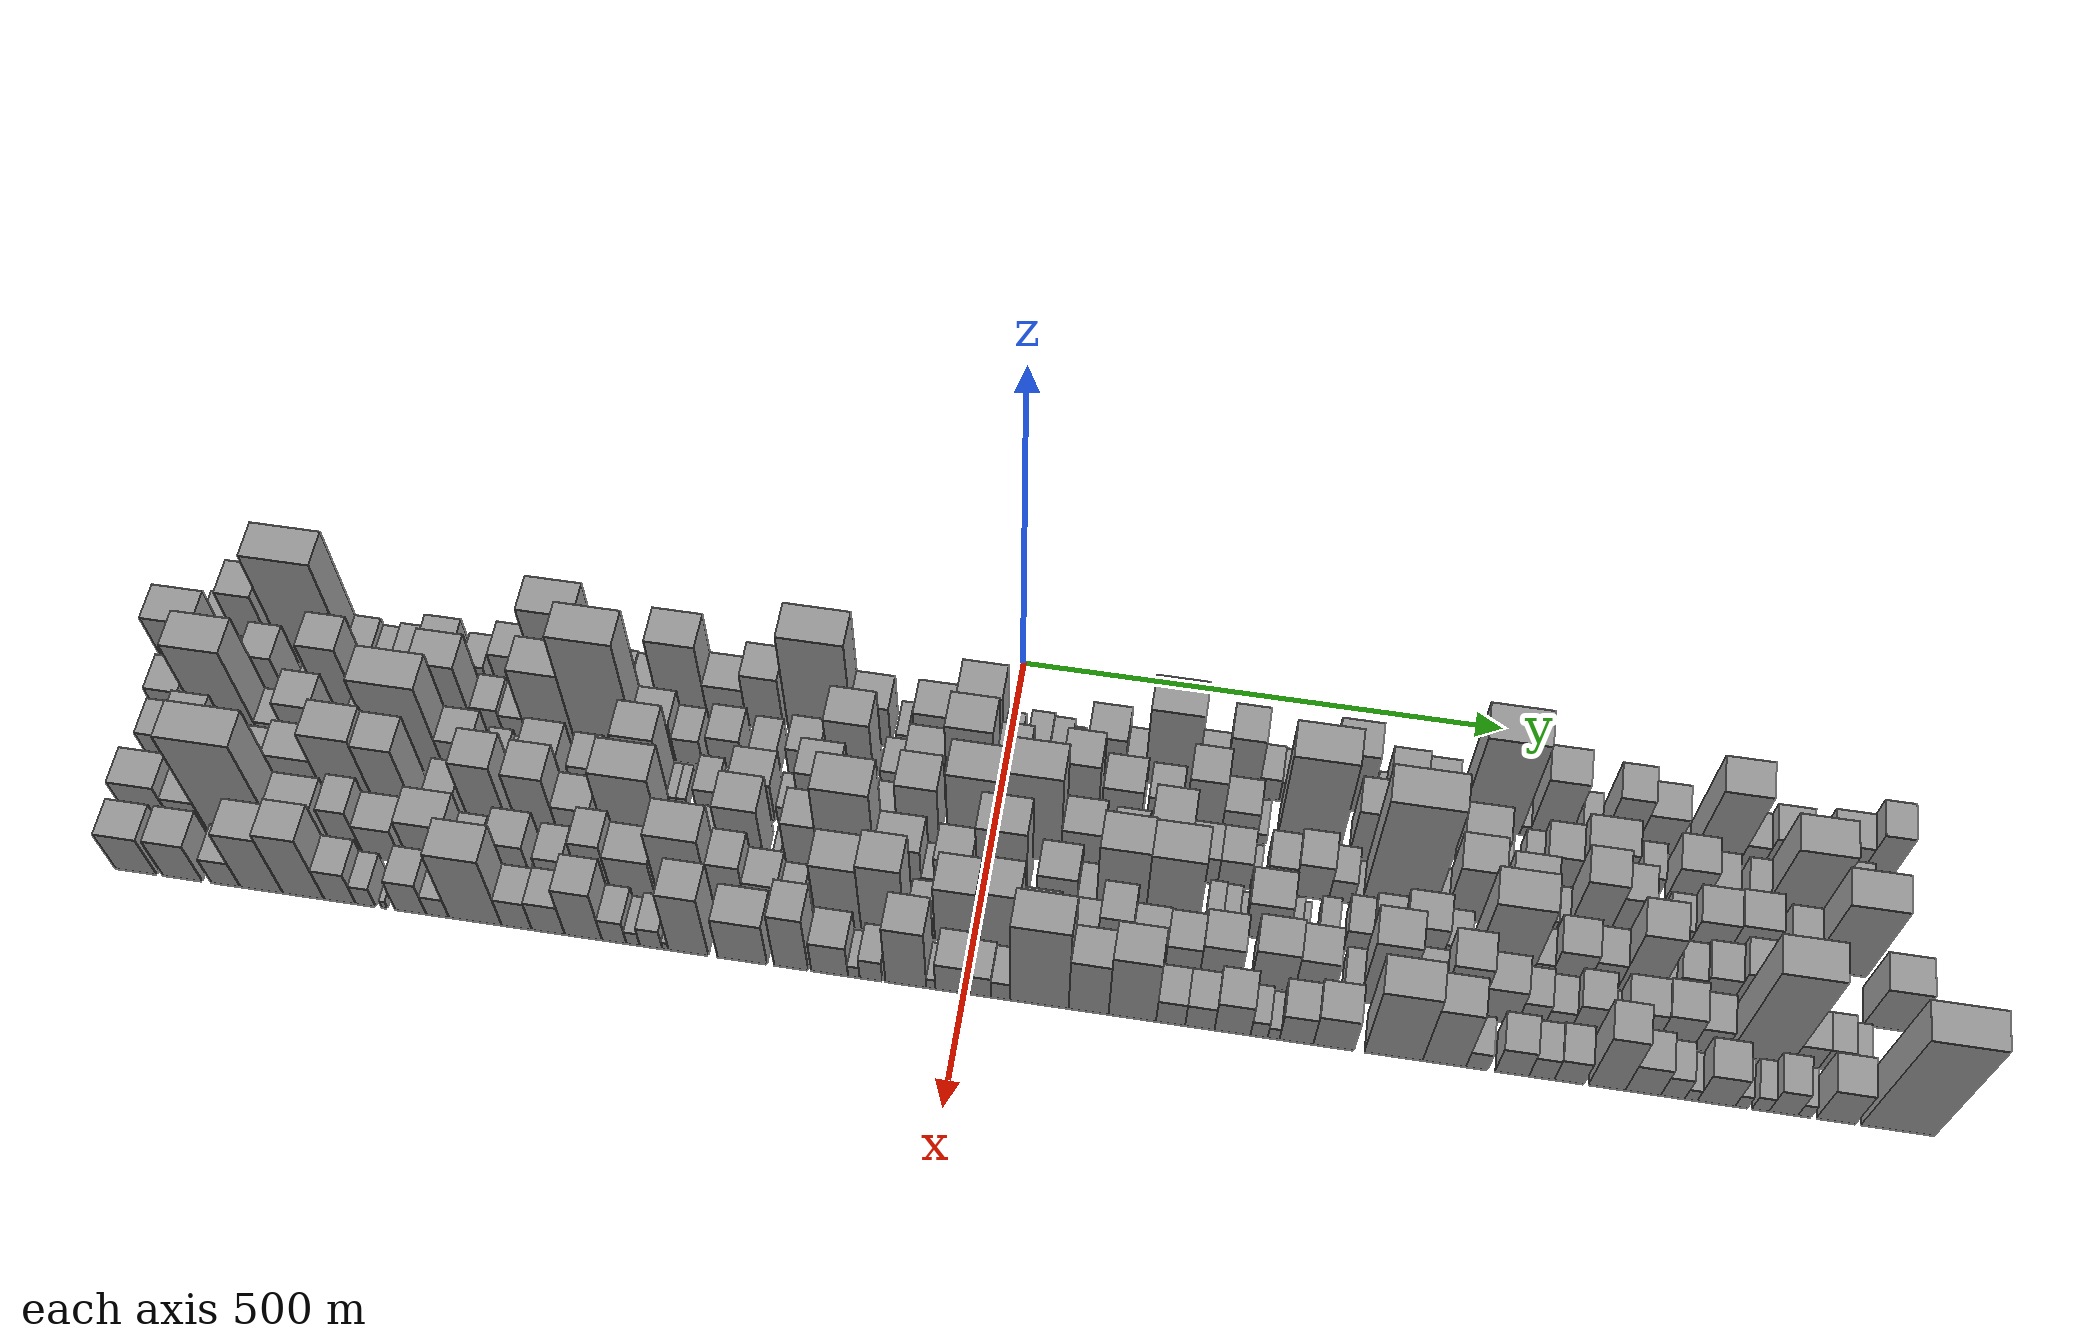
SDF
<sdf version="1.6">
 <world name="default">
  <scene>
   <sky><clouds><speed>12</speed></clouds></sky>
   <ambient>0.4 0.4 0.4 1</ambient>
   <background>0.7 0.7 0.7 1</background>
   <shadows>1</shadows>
  </scene>
  <gravity>0 0 -9.8066</gravity>
  <magnetic_field>6e-06 2.3e-05 -4.2e-05</magnetic_field>
  <physics default="0" name="default_physics" type="ode">
   <ode>
    <solver>
     <type>quick</type>
     <iters>10</iters>
     <sor>1.0</sor>
     <use_dynamic_moi_rescaling>0</use_dynamic_moi_rescaling>
    </solver>
    <constraints>
     <cfm>0</cfm>
     <erp>0.2</erp>
     <contact_max_correcting_vel>100</contact_max_correcting_vel>
     <contact_surface_layer>0.001</contact_surface_layer>
    </constraints>
   </ode>
   <max_step_size>0.004</max_step_size>
   <real_time_factor>1</real_time_factor>
   <real_time_update_rate>250</real_time_update_rate>
  </physics>
  <light name="sun" type="directional">
   <pose>0 0 10 0 0 0</pose>
   <diffuse>0.8 0.8 0.8 1</diffuse>
   <specular>0.2 0.2 0.2 1</specular>
   <attenuation>
    <range>1000</range>
    <constant>0.9</constant>
    <linear>0.01</linear>
    <quadratic>0.001</quadratic>
   </attenuation>
   <direction>-0.5 0.1 -0.9</direction>
  </light>
  <model name="building_1">
   <static>1</static>
   <pose>100.0000 -849.9705 0 0.000000 0.000000 0.000000</pose>
   <link name="link">
    <pose>0 0 19.50 0 0 0</pose>
    <collision name="collision"><geometry><box><size>40.0000 20.0590 39.0000</size></box></geometry></collision>
    <visual name="visual">
     <cast_shadows>0</cast_shadows>
     <geometry><box><size>40.0000 20.0590 39.0000</size></box></geometry>
     <material>
      <script>
       <uri>model://grey_wall/materials/scripts</uri>
       <uri>model://grey_wall/materials/textures</uri>
       <name>vrc/grey_wall</name>
      </script>
     </material>
    </visual>
   </link>
  </model>
  <model name="building_2">
   <static>1</static>
   <pose>100.0000 -823.1880 0 0.000000 0.000000 0.000000</pose>
   <link name="link">
    <pose>0 0 28.50 0 0 0</pose>
    <collision name="collision"><geometry><box><size>40.0000 33.5061 57.0000</size></box></geometry></collision>
    <visual name="visual">
     <cast_shadows>0</cast_shadows>
     <geometry><box><size>40.0000 33.5061 57.0000</size></box></geometry>
     <material>
      <script>
       <uri>model://grey_wall/materials/scripts</uri>
       <uri>model://grey_wall/materials/textures</uri>
       <name>vrc/grey_wall</name>
      </script>
     </material>
    </visual>
   </link>
  </model>
  <model name="building_3">
   <static>1</static>
   <pose>100.0000 -787.8565 0 0.000000 0.000000 0.000000</pose>
   <link name="link">
    <pose>0 0 61.50 0 0 0</pose>
    <collision name="collision"><geometry><box><size>40.0000 37.1568 123.0000</size></box></geometry></collision>
    <visual name="visual">
     <cast_shadows>0</cast_shadows>
     <geometry><box><size>40.0000 37.1568 123.0000</size></box></geometry>
     <material>
      <script>
       <uri>model://grey_wall/materials/scripts</uri>
       <uri>model://grey_wall/materials/textures</uri>
       <name>vrc/grey_wall</name>
      </script>
     </material>
    </visual>
   </link>
  </model>
  <model name="building_4">
   <static>1</static>
   <pose>100.0000 -764.4919 0 0.000000 0.000000 0.000000</pose>
   <link name="link">
    <pose>0 0 10.50 0 0 0</pose>
    <collision name="collision"><geometry><box><size>40.0000 9.5725 21.0000</size></box></geometry></collision>
    <visual name="visual">
     <cast_shadows>0</cast_shadows>
     <geometry><box><size>40.0000 9.5725 21.0000</size></box></geometry>
     <material>
      <script>
       <uri>model://grey_wall/materials/scripts</uri>
       <uri>model://grey_wall/materials/textures</uri>
       <name>vrc/grey_wall</name>
      </script>
     </material>
    </visual>
   </link>
  </model>
  <model name="building_5">
   <static>1</static>
   <pose>100.0000 -723.9472 0 0.000000 0.000000 0.000000</pose>
   <link name="link">
    <pose>0 0 100.50 0 0 0</pose>
    <collision name="collision"><geometry><box><size>40.0000 71.5170 201.0000</size></box></geometry></collision>
    <visual name="visual">
     <cast_shadows>0</cast_shadows>
     <geometry><box><size>40.0000 71.5170 201.0000</size></box></geometry>
     <material>
      <script>
       <uri>model://grey_wall/materials/scripts</uri>
       <uri>model://grey_wall/materials/textures</uri>
       <name>vrc/grey_wall</name>
      </script>
     </material>
    </visual>
   </link>
  </model>
  <model name="building_6">
   <static>1</static>
   <pose>100.0000 -674.4007 0 0.000000 0.000000 0.000000</pose>
   <link name="link">
    <pose>0 0 24.00 0 0 0</pose>
    <collision name="collision"><geometry><box><size>40.0000 27.5761 48.0000</size></box></geometry></collision>
    <visual name="visual">
     <cast_shadows>0</cast_shadows>
     <geometry><box><size>40.0000 27.5761 48.0000</size></box></geometry>
     <material>
      <script>
       <uri>model://grey_wall/materials/scripts</uri>
       <uri>model://grey_wall/materials/textures</uri>
       <name>vrc/grey_wall</name>
      </script>
     </material>
    </visual>
   </link>
  </model>
  <model name="building_7">
   <static>1</static>
   <pose>100.0000 -650.1896 0 0.000000 0.000000 0.000000</pose>
   <link name="link">
    <pose>0 0 18.00 0 0 0</pose>
    <collision name="collision"><geometry><box><size>40.0000 20.8461 36.0000</size></box></geometry></collision>
    <visual name="visual">
     <cast_shadows>0</cast_shadows>
     <geometry><box><size>40.0000 20.8461 36.0000</size></box></geometry>
     <material>
      <script>
       <uri>model://grey_wall/materials/scripts</uri>
       <uri>model://grey_wall/materials/textures</uri>
       <name>vrc/grey_wall</name>
      </script>
     </material>
    </visual>
   </link>
  </model>
  <model name="building_8">
   <static>1</static>
   <pose>100.0000 -627.7108 0 0.000000 0.000000 0.000000</pose>
   <link name="link">
    <pose>0 0 22.50 0 0 0</pose>
    <collision name="collision"><geometry><box><size>40.0000 24.1114 45.0000</size></box></geometry></collision>
    <visual name="visual">
     <cast_shadows>0</cast_shadows>
     <geometry><box><size>40.0000 24.1114 45.0000</size></box></geometry>
     <material>
      <script>
       <uri>model://grey_wall/materials/scripts</uri>
       <uri>model://grey_wall/materials/textures</uri>
       <name>vrc/grey_wall</name>
      </script>
     </material>
    </visual>
   </link>
  </model>
  <model name="building_9">
   <static>1</static>
   <pose>100.0000 -590.5722 0 0.000000 0.000000 0.000000</pose>
   <link name="link">
    <pose>0 0 34.50 0 0 0</pose>
    <collision name="collision"><geometry><box><size>40.0000 38.1658 69.0000</size></box></geometry></collision>
    <visual name="visual">
     <cast_shadows>0</cast_shadows>
     <geometry><box><size>40.0000 38.1658 69.0000</size></box></geometry>
     <material>
      <script>
       <uri>model://grey_wall/materials/scripts</uri>
       <uri>model://grey_wall/materials/textures</uri>
       <name>vrc/grey_wall</name>
      </script>
     </material>
    </visual>
   </link>
  </model>
  <model name="building_10">
   <static>1</static>
   <pose>100.0000 -554.6304 0 0.000000 0.000000 0.000000</pose>
   <link name="link">
    <pose>0 0 22.50 0 0 0</pose>
    <collision name="collision"><geometry><box><size>40.0000 23.7178 45.0000</size></box></geometry></collision>
    <visual name="visual">
     <cast_shadows>0</cast_shadows>
     <geometry><box><size>40.0000 23.7178 45.0000</size></box></geometry>
     <material>
      <script>
       <uri>model://grey_wall/materials/scripts</uri>
       <uri>model://grey_wall/materials/textures</uri>
       <name>vrc/grey_wall</name>
      </script>
     </material>
    </visual>
   </link>
  </model>
  <model name="building_11">
   <static>1</static>
   <pose>100.0000 -511.8057 0 0.000000 0.000000 0.000000</pose>
   <link name="link">
    <pose>0 0 37.50 0 0 0</pose>
    <collision name="collision"><geometry><box><size>40.0000 41.9316 75.0000</size></box></geometry></collision>
    <visual name="visual">
     <cast_shadows>0</cast_shadows>
     <geometry><box><size>40.0000 41.9316 75.0000</size></box></geometry>
     <material>
      <script>
       <uri>model://grey_wall/materials/scripts</uri>
       <uri>model://grey_wall/materials/textures</uri>
       <name>vrc/grey_wall</name>
      </script>
     </material>
    </visual>
   </link>
  </model>
  <model name="building_12">
   <static>1</static>
   <pose>100.0000 -458.2166 0 0.000000 0.000000 0.000000</pose>
   <link name="link">
    <pose>0 0 85.50 0 0 0</pose>
    <collision name="collision"><geometry><box><size>40.0000 57.2466 171.0000</size></box></geometry></collision>
    <visual name="visual">
     <cast_shadows>0</cast_shadows>
     <geometry><box><size>40.0000 57.2466 171.0000</size></box></geometry>
     <material>
      <script>
       <uri>model://grey_wall/materials/scripts</uri>
       <uri>model://grey_wall/materials/textures</uri>
       <name>vrc/grey_wall</name>
      </script>
     </material>
    </visual>
   </link>
  </model>
  <model name="building_13">
   <static>1</static>
   <pose>100.0000 -423.8625 0 0.000000 0.000000 0.000000</pose>
   <link name="link">
    <pose>0 0 12.00 0 0 0</pose>
    <collision name="collision"><geometry><box><size>40.0000 11.4616 24.0000</size></box></geometry></collision>
    <visual name="visual">
     <cast_shadows>0</cast_shadows>
     <geometry><box><size>40.0000 11.4616 24.0000</size></box></geometry>
     <material>
      <script>
       <uri>model://grey_wall/materials/scripts</uri>
       <uri>model://grey_wall/materials/textures</uri>
       <name>vrc/grey_wall</name>
      </script>
     </material>
    </visual>
   </link>
  </model>
  <model name="building_14">
   <static>1</static>
   <pose>100.0000 -402.7906 0 0.000000 0.000000 0.000000</pose>
   <link name="link">
    <pose>0 0 27.00 0 0 0</pose>
    <collision name="collision"><geometry><box><size>40.0000 30.6820 54.0000</size></box></geometry></collision>
    <visual name="visual">
     <cast_shadows>0</cast_shadows>
     <geometry><box><size>40.0000 30.6820 54.0000</size></box></geometry>
     <material>
      <script>
       <uri>model://grey_wall/materials/scripts</uri>
       <uri>model://grey_wall/materials/textures</uri>
       <name>vrc/grey_wall</name>
      </script>
     </material>
    </visual>
   </link>
  </model>
  <model name="building_15">
   <static>1</static>
   <pose>100.0000 -374.5829 0 0.000000 0.000000 0.000000</pose>
   <link name="link">
    <pose>0 0 25.50 0 0 0</pose>
    <collision name="collision"><geometry><box><size>40.0000 25.7335 51.0000</size></box></geometry></collision>
    <visual name="visual">
     <cast_shadows>0</cast_shadows>
     <geometry><box><size>40.0000 25.7335 51.0000</size></box></geometry>
     <material>
      <script>
       <uri>model://grey_wall/materials/scripts</uri>
       <uri>model://grey_wall/materials/textures</uri>
       <name>vrc/grey_wall</name>
      </script>
     </material>
    </visual>
   </link>
  </model>
  <model name="building_16">
   <static>1</static>
   <pose>100.0000 -336.2735 0 0.000000 0.000000 0.000000</pose>
   <link name="link">
    <pose>0 0 72.00 0 0 0</pose>
    <collision name="collision"><geometry><box><size>40.0000 50.8852 144.0000</size></box></geometry></collision>
    <visual name="visual">
     <cast_shadows>0</cast_shadows>
     <geometry><box><size>40.0000 50.8852 144.0000</size></box></geometry>
     <material>
      <script>
       <uri>model://grey_wall/materials/scripts</uri>
       <uri>model://grey_wall/materials/textures</uri>
       <name>vrc/grey_wall</name>
      </script>
     </material>
    </visual>
   </link>
  </model>
  <model name="building_17">
   <static>1</static>
   <pose>100.0000 -290.3464 0 0.000000 0.000000 0.000000</pose>
   <link name="link">
    <pose>0 0 36.00 0 0 0</pose>
    <collision name="collision"><geometry><box><size>40.0000 40.9691 72.0000</size></box></geometry></collision>
    <visual name="visual">
     <cast_shadows>0</cast_shadows>
     <geometry><box><size>40.0000 40.9691 72.0000</size></box></geometry>
     <material>
      <script>
       <uri>model://grey_wall/materials/scripts</uri>
       <uri>model://grey_wall/materials/textures</uri>
       <name>vrc/grey_wall</name>
      </script>
     </material>
    </visual>
   </link>
  </model>
  <model name="building_18">
   <static>1</static>
   <pose>100.0000 -250.6649 0 0.000000 0.000000 0.000000</pose>
   <link name="link">
    <pose>0 0 51.00 0 0 0</pose>
    <collision name="collision"><geometry><box><size>40.0000 38.3940 102.0000</size></box></geometry></collision>
    <visual name="visual">
     <cast_shadows>0</cast_shadows>
     <geometry><box><size>40.0000 38.3940 102.0000</size></box></geometry>
     <material>
      <script>
       <uri>model://grey_wall/materials/scripts</uri>
       <uri>model://grey_wall/materials/textures</uri>
       <name>vrc/grey_wall</name>
      </script>
     </material>
    </visual>
   </link>
  </model>
  <model name="building_19">
   <static>1</static>
   <pose>100.0000 -192.8025 0 0.000000 0.000000 0.000000</pose>
   <link name="link">
    <pose>0 0 93.00 0 0 0</pose>
    <collision name="collision"><geometry><box><size>40.0000 67.3308 186.0000</size></box></geometry></collision>
    <visual name="visual">
     <cast_shadows>0</cast_shadows>
     <geometry><box><size>40.0000 67.3308 186.0000</size></box></geometry>
     <material>
      <script>
       <uri>model://grey_wall/materials/scripts</uri>
       <uri>model://grey_wall/materials/textures</uri>
       <name>vrc/grey_wall</name>
      </script>
     </material>
    </visual>
   </link>
  </model>
  <model name="building_20">
   <static>1</static>
   <pose>100.0000 -139.3670 0 0.000000 0.000000 0.000000</pose>
   <link name="link">
    <pose>0 0 37.50 0 0 0</pose>
    <collision name="collision"><geometry><box><size>40.0000 39.5402 75.0000</size></box></geometry></collision>
    <visual name="visual">
     <cast_shadows>0</cast_shadows>
     <geometry><box><size>40.0000 39.5402 75.0000</size></box></geometry>
     <material>
      <script>
       <uri>model://grey_wall/materials/scripts</uri>
       <uri>model://grey_wall/materials/textures</uri>
       <name>vrc/grey_wall</name>
      </script>
     </material>
    </visual>
   </link>
  </model>
  <model name="building_21">
   <static>1</static>
   <pose>100.0000 -107.6171 0 0.000000 0.000000 0.000000</pose>
   <link name="link">
    <pose>0 0 13.50 0 0 0</pose>
    <collision name="collision"><geometry><box><size>40.0000 11.9597 27.0000</size></box></geometry></collision>
    <visual name="visual">
     <cast_shadows>0</cast_shadows>
     <geometry><box><size>40.0000 11.9597 27.0000</size></box></geometry>
     <material>
      <script>
       <uri>model://grey_wall/materials/scripts</uri>
       <uri>model://grey_wall/materials/textures</uri>
       <name>vrc/grey_wall</name>
      </script>
     </material>
    </visual>
   </link>
  </model>
  <model name="building_22">
   <static>1</static>
   <pose>100.0000 -98.2412 0 0.000000 0.000000 0.000000</pose>
   <link name="link">
    <pose>0 0 7.50 0 0 0</pose>
    <collision name="collision"><geometry><box><size>40.0000 6.7922 15.0000</size></box></geometry></collision>
    <visual name="visual">
     <cast_shadows>0</cast_shadows>
     <geometry><box><size>40.0000 6.7922 15.0000</size></box></geometry>
     <material>
      <script>
       <uri>model://grey_wall/materials/scripts</uri>
       <uri>model://grey_wall/materials/textures</uri>
       <name>vrc/grey_wall</name>
      </script>
     </material>
    </visual>
   </link>
  </model>
  <model name="building_23">
   <static>1</static>
   <pose>100.0000 -74.6883 0 0.000000 0.000000 0.000000</pose>
   <link name="link">
    <pose>0 0 37.50 0 0 0</pose>
    <collision name="collision"><geometry><box><size>40.0000 40.3135 75.0000</size></box></geometry></collision>
    <visual name="visual">
     <cast_shadows>0</cast_shadows>
     <geometry><box><size>40.0000 40.3135 75.0000</size></box></geometry>
     <material>
      <script>
       <uri>model://grey_wall/materials/scripts</uri>
       <uri>model://grey_wall/materials/textures</uri>
       <name>vrc/grey_wall</name>
      </script>
     </material>
    </visual>
   </link>
  </model>
  <model name="building_24">
   <static>1</static>
   <pose>100.0000 -26.6309 0 0.000000 0.000000 0.000000</pose>
   <link name="link">
    <pose>0 0 63.00 0 0 0</pose>
    <collision name="collision"><geometry><box><size>40.0000 45.8013 126.0000</size></box></geometry></collision>
    <visual name="visual">
     <cast_shadows>0</cast_shadows>
     <geometry><box><size>40.0000 45.8013 126.0000</size></box></geometry>
     <material>
      <script>
       <uri>model://grey_wall/materials/scripts</uri>
       <uri>model://grey_wall/materials/textures</uri>
       <name>vrc/grey_wall</name>
      </script>
     </material>
    </visual>
   </link>
  </model>
  <model name="building_25">
   <static>1</static>
   <pose>100.0000 5.6907 0 0.000000 0.000000 0.000000</pose>
   <link name="link">
    <pose>0 0 18.00 0 0 0</pose>
    <collision name="collision"><geometry><box><size>40.0000 18.8419 36.0000</size></box></geometry></collision>
    <visual name="visual">
     <cast_shadows>0</cast_shadows>
     <geometry><box><size>40.0000 18.8419 36.0000</size></box></geometry>
     <material>
      <script>
       <uri>model://grey_wall/materials/scripts</uri>
       <uri>model://grey_wall/materials/textures</uri>
       <name>vrc/grey_wall</name>
      </script>
     </material>
    </visual>
   </link>
  </model>
  <model name="building_26">
   <static>1</static>
   <pose>100.0000 32.7664 0 0.000000 0.000000 0.000000</pose>
   <link name="link">
    <pose>0 0 22.50 0 0 0</pose>
    <collision name="collision"><geometry><box><size>40.0000 23.3094 45.0000</size></box></geometry></collision>
    <visual name="visual">
     <cast_shadows>0</cast_shadows>
     <geometry><box><size>40.0000 23.3094 45.0000</size></box></geometry>
     <material>
      <script>
       <uri>model://grey_wall/materials/scripts</uri>
       <uri>model://grey_wall/materials/textures</uri>
       <name>vrc/grey_wall</name>
      </script>
     </material>
    </visual>
   </link>
  </model>
  <model name="building_27">
   <static>1</static>
   <pose>100.0000 55.0933 0 0.000000 0.000000 0.000000</pose>
   <link name="link">
    <pose>0 0 19.50 0 0 0</pose>
    <collision name="collision"><geometry><box><size>40.0000 21.3444 39.0000</size></box></geometry></collision>
    <visual name="visual">
     <cast_shadows>0</cast_shadows>
     <geometry><box><size>40.0000 21.3444 39.0000</size></box></geometry>
     <material>
      <script>
       <uri>model://grey_wall/materials/scripts</uri>
       <uri>model://grey_wall/materials/textures</uri>
       <name>vrc/grey_wall</name>
      </script>
     </material>
    </visual>
   </link>
  </model>
  <model name="building_28">
   <static>1</static>
   <pose>100.0000 71.3840 0 0.000000 0.000000 0.000000</pose>
   <link name="link">
    <pose>0 0 12.00 0 0 0</pose>
    <collision name="collision"><geometry><box><size>40.0000 11.2370 24.0000</size></box></geometry></collision>
    <visual name="visual">
     <cast_shadows>0</cast_shadows>
     <geometry><box><size>40.0000 11.2370 24.0000</size></box></geometry>
     <material>
      <script>
       <uri>model://grey_wall/materials/scripts</uri>
       <uri>model://grey_wall/materials/textures</uri>
       <name>vrc/grey_wall</name>
      </script>
     </material>
    </visual>
   </link>
  </model>
  <model name="building_29">
   <static>1</static>
   <pose>100.0000 102.6483 0 0.000000 0.000000 0.000000</pose>
   <link name="link">
    <pose>0 0 39.00 0 0 0</pose>
    <collision name="collision"><geometry><box><size>40.0000 39.2917 78.0000</size></box></geometry></collision>
    <visual name="visual">
     <cast_shadows>0</cast_shadows>
     <geometry><box><size>40.0000 39.2917 78.0000</size></box></geometry>
     <material>
      <script>
       <uri>model://grey_wall/materials/scripts</uri>
       <uri>model://grey_wall/materials/textures</uri>
       <name>vrc/grey_wall</name>
      </script>
     </material>
    </visual>
   </link>
  </model>
  <model name="building_30">
   <static>1</static>
   <pose>100.0000 132.4842 0 0.000000 0.000000 0.000000</pose>
   <link name="link">
    <pose>0 0 19.50 0 0 0</pose>
    <collision name="collision"><geometry><box><size>40.0000 20.3801 39.0000</size></box></geometry></collision>
    <visual name="visual">
     <cast_shadows>0</cast_shadows>
     <geometry><box><size>40.0000 20.3801 39.0000</size></box></geometry>
     <material>
      <script>
       <uri>model://grey_wall/materials/scripts</uri>
       <uri>model://grey_wall/materials/textures</uri>
       <name>vrc/grey_wall</name>
      </script>
     </material>
    </visual>
   </link>
  </model>
  <model name="building_31">
   <static>1</static>
   <pose>100.0000 169.2116 0 0.000000 0.000000 0.000000</pose>
   <link name="link">
    <pose>0 0 73.50 0 0 0</pose>
    <collision name="collision"><geometry><box><size>40.0000 53.0747 147.0000</size></box></geometry></collision>
    <visual name="visual">
     <cast_shadows>0</cast_shadows>
     <geometry><box><size>40.0000 53.0747 147.0000</size></box></geometry>
     <material>
      <script>
       <uri>model://grey_wall/materials/scripts</uri>
       <uri>model://grey_wall/materials/textures</uri>
       <name>vrc/grey_wall</name>
      </script>
     </material>
    </visual>
   </link>
  </model>
  <model name="building_32">
   <static>1</static>
   <pose>100.0000 209.7995 0 0.000000 0.000000 0.000000</pose>
   <link name="link">
    <pose>0 0 27.00 0 0 0</pose>
    <collision name="collision"><geometry><box><size>40.0000 28.1011 54.0000</size></box></geometry></collision>
    <visual name="visual">
     <cast_shadows>0</cast_shadows>
     <geometry><box><size>40.0000 28.1011 54.0000</size></box></geometry>
     <material>
      <script>
       <uri>model://grey_wall/materials/scripts</uri>
       <uri>model://grey_wall/materials/textures</uri>
       <name>vrc/grey_wall</name>
      </script>
     </material>
    </visual>
   </link>
  </model>
  <model name="building_33">
   <static>1</static>
   <pose>100.0000 241.1143 0 0.000000 0.000000 0.000000</pose>
   <link name="link">
    <pose>0 0 57.00 0 0 0</pose>
    <collision name="collision"><geometry><box><size>40.0000 34.5283 114.0000</size></box></geometry></collision>
    <visual name="visual">
     <cast_shadows>0</cast_shadows>
     <geometry><box><size>40.0000 34.5283 114.0000</size></box></geometry>
     <material>
      <script>
       <uri>model://grey_wall/materials/scripts</uri>
       <uri>model://grey_wall/materials/textures</uri>
       <name>vrc/grey_wall</name>
      </script>
     </material>
    </visual>
   </link>
  </model>
  <model name="building_34">
   <static>1</static>
   <pose>100.0000 269.3586 0 0.000000 0.000000 0.000000</pose>
   <link name="link">
    <pose>0 0 21.00 0 0 0</pose>
    <collision name="collision"><geometry><box><size>40.0000 21.9605 42.0000</size></box></geometry></collision>
    <visual name="visual">
     <cast_shadows>0</cast_shadows>
     <geometry><box><size>40.0000 21.9605 42.0000</size></box></geometry>
     <material>
      <script>
       <uri>model://grey_wall/materials/scripts</uri>
       <uri>model://grey_wall/materials/textures</uri>
       <name>vrc/grey_wall</name>
      </script>
     </material>
    </visual>
   </link>
  </model>
  <model name="building_35">
   <static>1</static>
   <pose>100.0000 290.8779 0 0.000000 0.000000 0.000000</pose>
   <link name="link">
    <pose>0 0 19.50 0 0 0</pose>
    <collision name="collision"><geometry><box><size>40.0000 21.0780 39.0000</size></box></geometry></collision>
    <visual name="visual">
     <cast_shadows>0</cast_shadows>
     <geometry><box><size>40.0000 21.0780 39.0000</size></box></geometry>
     <material>
      <script>
       <uri>model://grey_wall/materials/scripts</uri>
       <uri>model://grey_wall/materials/textures</uri>
       <name>vrc/grey_wall</name>
      </script>
     </material>
    </visual>
   </link>
  </model>
  <model name="building_36">
   <static>1</static>
   <pose>100.0000 314.7854 0 0.000000 0.000000 0.000000</pose>
   <link name="link">
    <pose>0 0 24.00 0 0 0</pose>
    <collision name="collision"><geometry><box><size>40.0000 26.7369 48.0000</size></box></geometry></collision>
    <visual name="visual">
     <cast_shadows>0</cast_shadows>
     <geometry><box><size>40.0000 26.7369 48.0000</size></box></geometry>
     <material>
      <script>
       <uri>model://grey_wall/materials/scripts</uri>
       <uri>model://grey_wall/materials/textures</uri>
       <name>vrc/grey_wall</name>
      </script>
     </material>
    </visual>
   </link>
  </model>
  <model name="building_37">
   <static>1</static>
   <pose>100.0000 349.0575 0 0.000000 0.000000 0.000000</pose>
   <link name="link">
    <pose>0 0 57.00 0 0 0</pose>
    <collision name="collision"><geometry><box><size>40.0000 41.8073 114.0000</size></box></geometry></collision>
    <visual name="visual">
     <cast_shadows>0</cast_shadows>
     <geometry><box><size>40.0000 41.8073 114.0000</size></box></geometry>
     <material>
      <script>
       <uri>model://grey_wall/materials/scripts</uri>
       <uri>model://grey_wall/materials/textures</uri>
       <name>vrc/grey_wall</name>
      </script>
     </material>
    </visual>
   </link>
  </model>
  <model name="building_38">
   <static>1</static>
   <pose>100.0000 381.0340 0 0.000000 0.000000 0.000000</pose>
   <link name="link">
    <pose>0 0 9.00 0 0 0</pose>
    <collision name="collision"><geometry><box><size>40.0000 8.1457 18.0000</size></box></geometry></collision>
    <visual name="visual">
     <cast_shadows>0</cast_shadows>
     <geometry><box><size>40.0000 8.1457 18.0000</size></box></geometry>
     <material>
      <script>
       <uri>model://grey_wall/materials/scripts</uri>
       <uri>model://grey_wall/materials/textures</uri>
       <name>vrc/grey_wall</name>
      </script>
     </material>
    </visual>
   </link>
  </model>
  <model name="building_39">
   <static>1</static>
   <pose>100.0000 403.5314 0 0.000000 0.000000 0.000000</pose>
   <link name="link">
    <pose>0 0 36.00 0 0 0</pose>
    <collision name="collision"><geometry><box><size>40.0000 36.8492 72.0000</size></box></geometry></collision>
    <visual name="visual">
     <cast_shadows>0</cast_shadows>
     <geometry><box><size>40.0000 36.8492 72.0000</size></box></geometry>
     <material>
      <script>
       <uri>model://grey_wall/materials/scripts</uri>
       <uri>model://grey_wall/materials/textures</uri>
       <name>vrc/grey_wall</name>
      </script>
     </material>
    </visual>
   </link>
  </model>
  <model name="building_40">
   <static>1</static>
   <pose>100.0000 437.7811 0 0.000000 0.000000 0.000000</pose>
   <link name="link">
    <pose>0 0 31.50 0 0 0</pose>
    <collision name="collision"><geometry><box><size>40.0000 31.6502 63.0000</size></box></geometry></collision>
    <visual name="visual">
     <cast_shadows>0</cast_shadows>
     <geometry><box><size>40.0000 31.6502 63.0000</size></box></geometry>
     <material>
      <script>
       <uri>model://grey_wall/materials/scripts</uri>
       <uri>model://grey_wall/materials/textures</uri>
       <name>vrc/grey_wall</name>
      </script>
     </material>
    </visual>
   </link>
  </model>
  <model name="building_41">
   <static>1</static>
   <pose>100.0000 493.1594 0 0.000000 0.000000 0.000000</pose>
   <link name="link">
    <pose>0 0 90.00 0 0 0</pose>
    <collision name="collision"><geometry><box><size>40.0000 61.1064 180.0000</size></box></geometry></collision>
    <visual name="visual">
     <cast_shadows>0</cast_shadows>
     <geometry><box><size>40.0000 61.1064 180.0000</size></box></geometry>
     <material>
      <script>
       <uri>model://grey_wall/materials/scripts</uri>
       <uri>model://grey_wall/materials/textures</uri>
       <name>vrc/grey_wall</name>
      </script>
     </material>
    </visual>
   </link>
  </model>
  <model name="building_42">
   <static>1</static>
   <pose>100.0000 528.1135 0 0.000000 0.000000 0.000000</pose>
   <link name="link">
    <pose>0 0 9.00 0 0 0</pose>
    <collision name="collision"><geometry><box><size>40.0000 8.8017 18.0000</size></box></geometry></collision>
    <visual name="visual">
     <cast_shadows>0</cast_shadows>
     <geometry><box><size>40.0000 8.8017 18.0000</size></box></geometry>
     <material>
      <script>
       <uri>model://grey_wall/materials/scripts</uri>
       <uri>model://grey_wall/materials/textures</uri>
       <name>vrc/grey_wall</name>
      </script>
     </material>
    </visual>
   </link>
  </model>
  <model name="building_43">
   <static>1</static>
   <pose>100.0000 552.5174 0 0.000000 0.000000 0.000000</pose>
   <link name="link">
    <pose>0 0 58.50 0 0 0</pose>
    <collision name="collision"><geometry><box><size>40.0000 40.0060 117.0000</size></box></geometry></collision>
    <visual name="visual">
     <cast_shadows>0</cast_shadows>
     <geometry><box><size>40.0000 40.0060 117.0000</size></box></geometry>
     <material>
      <script>
       <uri>model://grey_wall/materials/scripts</uri>
       <uri>model://grey_wall/materials/textures</uri>
       <name>vrc/grey_wall</name>
      </script>
     </material>
    </visual>
   </link>
  </model>
  <model name="building_44">
   <static>1</static>
   <pose>100.0000 590.0059 0 0.000000 0.000000 0.000000</pose>
   <link name="link">
    <pose>0 0 18.00 0 0 0</pose>
    <collision name="collision"><geometry><box><size>40.0000 18.9711 36.0000</size></box></geometry></collision>
    <visual name="visual">
     <cast_shadows>0</cast_shadows>
     <geometry><box><size>40.0000 18.9711 36.0000</size></box></geometry>
     <material>
      <script>
       <uri>model://grey_wall/materials/scripts</uri>
       <uri>model://grey_wall/materials/textures</uri>
       <name>vrc/grey_wall</name>
      </script>
     </material>
    </visual>
   </link>
  </model>
  <model name="building_45">
   <static>1</static>
   <pose>100.0000 621.5701 0 0.000000 0.000000 0.000000</pose>
   <link name="link">
    <pose>0 0 51.00 0 0 0</pose>
    <collision name="collision"><geometry><box><size>40.0000 34.1574 102.0000</size></box></geometry></collision>
    <visual name="visual">
     <cast_shadows>0</cast_shadows>
     <geometry><box><size>40.0000 34.1574 102.0000</size></box></geometry>
     <material>
      <script>
       <uri>model://grey_wall/materials/scripts</uri>
       <uri>model://grey_wall/materials/textures</uri>
       <name>vrc/grey_wall</name>
      </script>
     </material>
    </visual>
   </link>
  </model>
  <model name="building_46">
   <static>1</static>
   <pose>100.0000 658.1982 0 0.000000 0.000000 0.000000</pose>
   <link name="link">
    <pose>0 0 37.50 0 0 0</pose>
    <collision name="collision"><geometry><box><size>40.0000 39.0986 75.0000</size></box></geometry></collision>
    <visual name="visual">
     <cast_shadows>0</cast_shadows>
     <geometry><box><size>40.0000 39.0986 75.0000</size></box></geometry>
     <material>
      <script>
       <uri>model://grey_wall/materials/scripts</uri>
       <uri>model://grey_wall/materials/textures</uri>
       <name>vrc/grey_wall</name>
      </script>
     </material>
    </visual>
   </link>
  </model>
  <model name="building_47">
   <static>1</static>
   <pose>100.0000 685.0311 0 0.000000 0.000000 0.000000</pose>
   <link name="link">
    <pose>0 0 10.50 0 0 0</pose>
    <collision name="collision"><geometry><box><size>40.0000 8.5673 21.0000</size></box></geometry></collision>
    <visual name="visual">
     <cast_shadows>0</cast_shadows>
     <geometry><box><size>40.0000 8.5673 21.0000</size></box></geometry>
     <material>
      <script>
       <uri>model://grey_wall/materials/scripts</uri>
       <uri>model://grey_wall/materials/textures</uri>
       <name>vrc/grey_wall</name>
      </script>
     </material>
    </visual>
   </link>
  </model>
  <model name="building_48">
   <static>1</static>
   <pose>100.0000 718.0292 0 0.000000 0.000000 0.000000</pose>
   <link name="link">
    <pose>0 0 70.50 0 0 0</pose>
    <collision name="collision"><geometry><box><size>40.0000 47.4289 141.0000</size></box></geometry></collision>
    <visual name="visual">
     <cast_shadows>0</cast_shadows>
     <geometry><box><size>40.0000 47.4289 141.0000</size></box></geometry>
     <material>
      <script>
       <uri>model://grey_wall/materials/scripts</uri>
       <uri>model://grey_wall/materials/textures</uri>
       <name>vrc/grey_wall</name>
      </script>
     </material>
    </visual>
   </link>
  </model>
  <model name="building_49">
   <static>1</static>
   <pose>100.0000 753.3840 0 0.000000 0.000000 0.000000</pose>
   <link name="link">
    <pose>0 0 21.00 0 0 0</pose>
    <collision name="collision"><geometry><box><size>40.0000 23.2806 42.0000</size></box></geometry></collision>
    <visual name="visual">
     <cast_shadows>0</cast_shadows>
     <geometry><box><size>40.0000 23.2806 42.0000</size></box></geometry>
     <material>
      <script>
       <uri>model://grey_wall/materials/scripts</uri>
       <uri>model://grey_wall/materials/textures</uri>
       <name>vrc/grey_wall</name>
      </script>
     </material>
    </visual>
   </link>
  </model>
  <model name="building_50">
   <static>1</static>
   <pose>100.0000 783.2074 0 0.000000 0.000000 0.000000</pose>
   <link name="link">
    <pose>0 0 31.50 0 0 0</pose>
    <collision name="collision"><geometry><box><size>40.0000 36.3662 63.0000</size></box></geometry></collision>
    <visual name="visual">
     <cast_shadows>0</cast_shadows>
     <geometry><box><size>40.0000 36.3662 63.0000</size></box></geometry>
     <material>
      <script>
       <uri>model://grey_wall/materials/scripts</uri>
       <uri>model://grey_wall/materials/textures</uri>
       <name>vrc/grey_wall</name>
      </script>
     </material>
    </visual>
   </link>
  </model>
  <model name="building_51">
   <static>1</static>
   <pose>100.0000 810.5453 0 0.000000 0.000000 0.000000</pose>
   <link name="link">
    <pose>0 0 16.50 0 0 0</pose>
    <collision name="collision"><geometry><box><size>40.0000 18.3096 33.0000</size></box></geometry></collision>
    <visual name="visual">
     <cast_shadows>0</cast_shadows>
     <geometry><box><size>40.0000 18.3096 33.0000</size></box></geometry>
     <material>
      <script>
       <uri>model://grey_wall/materials/scripts</uri>
       <uri>model://grey_wall/materials/textures</uri>
       <name>vrc/grey_wall</name>
      </script>
     </material>
    </visual>
   </link>
  </model>
  <model name="building_52">
   <static>1</static>
   <pose>100.0000 838.9012 0 0.000000 0.000000 0.000000</pose>
   <link name="link">
    <pose>0 0 34.50 0 0 0</pose>
    <collision name="collision"><geometry><box><size>40.0000 38.4023 69.0000</size></box></geometry></collision>
    <visual name="visual">
     <cast_shadows>0</cast_shadows>
     <geometry><box><size>40.0000 38.4023 69.0000</size></box></geometry>
     <material>
      <script>
       <uri>model://grey_wall/materials/scripts</uri>
       <uri>model://grey_wall/materials/textures</uri>
       <name>vrc/grey_wall</name>
      </script>
     </material>
    </visual>
   </link>
  </model>
  <model name="building_53">
   <static>1</static>
   <pose>100.0000 873.0627 0 0.000000 0.000000 0.000000</pose>
   <link name="link">
    <pose>0 0 49.50 0 0 0</pose>
    <collision name="collision"><geometry><box><size>40.0000 29.9206 99.0000</size></box></geometry></collision>
    <visual name="visual">
     <cast_shadows>0</cast_shadows>
     <geometry><box><size>40.0000 29.9206 99.0000</size></box></geometry>
     <material>
      <script>
       <uri>model://grey_wall/materials/scripts</uri>
       <uri>model://grey_wall/materials/textures</uri>
       <name>vrc/grey_wall</name>
      </script>
     </material>
    </visual>
   </link>
  </model>
  <model name="building_54">
   <static>1</static>
   <pose>152.0000 -833.8782 0 0.000000 0.000000 0.000000</pose>
   <link name="link">
    <pose>0 0 72.00 0 0 0</pose>
    <collision name="collision"><geometry><box><size>40.0000 52.2435 144.0000</size></box></geometry></collision>
    <visual name="visual">
     <cast_shadows>0</cast_shadows>
     <geometry><box><size>40.0000 52.2435 144.0000</size></box></geometry>
     <material>
      <script>
       <uri>model://grey_wall/materials/scripts</uri>
       <uri>model://grey_wall/materials/textures</uri>
       <name>vrc/grey_wall</name>
      </script>
     </material>
    </visual>
   </link>
  </model>
  <model name="building_55">
   <static>1</static>
   <pose>152.0000 -790.3990 0 0.000000 0.000000 0.000000</pose>
   <link name="link">
    <pose>0 0 31.50 0 0 0</pose>
    <collision name="collision"><geometry><box><size>40.0000 34.7149 63.0000</size></box></geometry></collision>
    <visual name="visual">
     <cast_shadows>0</cast_shadows>
     <geometry><box><size>40.0000 34.7149 63.0000</size></box></geometry>
     <material>
      <script>
       <uri>model://grey_wall/materials/scripts</uri>
       <uri>model://grey_wall/materials/textures</uri>
       <name>vrc/grey_wall</name>
      </script>
     </material>
    </visual>
   </link>
  </model>
  <model name="building_56">
   <static>1</static>
   <pose>152.0000 -756.1267 0 0.000000 0.000000 0.000000</pose>
   <link name="link">
    <pose>0 0 48.00 0 0 0</pose>
    <collision name="collision"><geometry><box><size>40.0000 33.8296 96.0000</size></box></geometry></collision>
    <visual name="visual">
     <cast_shadows>0</cast_shadows>
     <geometry><box><size>40.0000 33.8296 96.0000</size></box></geometry>
     <material>
      <script>
       <uri>model://grey_wall/materials/scripts</uri>
       <uri>model://grey_wall/materials/textures</uri>
       <name>vrc/grey_wall</name>
      </script>
     </material>
    </visual>
   </link>
  </model>
  <model name="building_57">
   <static>1</static>
   <pose>152.0000 -722.8699 0 0.000000 0.000000 0.000000</pose>
   <link name="link">
    <pose>0 0 16.50 0 0 0</pose>
    <collision name="collision"><geometry><box><size>40.0000 16.6840 33.0000</size></box></geometry></collision>
    <visual name="visual">
     <cast_shadows>0</cast_shadows>
     <geometry><box><size>40.0000 16.6840 33.0000</size></box></geometry>
     <material>
      <script>
       <uri>model://grey_wall/materials/scripts</uri>
       <uri>model://grey_wall/materials/textures</uri>
       <name>vrc/grey_wall</name>
      </script>
     </material>
    </visual>
   </link>
  </model>
  <model name="building_58">
   <static>1</static>
   <pose>152.0000 -684.3697 0 0.000000 0.000000 0.000000</pose>
   <link name="link">
    <pose>0 0 66.00 0 0 0</pose>
    <collision name="collision"><geometry><box><size>40.0000 40.3164 132.0000</size></box></geometry></collision>
    <visual name="visual">
     <cast_shadows>0</cast_shadows>
     <geometry><box><size>40.0000 40.3164 132.0000</size></box></geometry>
     <material>
      <script>
       <uri>model://grey_wall/materials/scripts</uri>
       <uri>model://grey_wall/materials/textures</uri>
       <name>vrc/grey_wall</name>
      </script>
     </material>
    </visual>
   </link>
  </model>
  <model name="building_59">
   <static>1</static>
   <pose>152.0000 -637.6428 0 0.000000 0.000000 0.000000</pose>
   <link name="link">
    <pose>0 0 34.50 0 0 0</pose>
    <collision name="collision"><geometry><box><size>40.0000 41.1373 69.0000</size></box></geometry></collision>
    <visual name="visual">
     <cast_shadows>0</cast_shadows>
     <geometry><box><size>40.0000 41.1373 69.0000</size></box></geometry>
     <material>
      <script>
       <uri>model://grey_wall/materials/scripts</uri>
       <uri>model://grey_wall/materials/textures</uri>
       <name>vrc/grey_wall</name>
      </script>
     </material>
    </visual>
   </link>
  </model>
  <model name="building_60">
   <static>1</static>
   <pose>152.0000 -604.3007 0 0.000000 0.000000 0.000000</pose>
   <link name="link">
    <pose>0 0 22.50 0 0 0</pose>
    <collision name="collision"><geometry><box><size>40.0000 25.5469 45.0000</size></box></geometry></collision>
    <visual name="visual">
     <cast_shadows>0</cast_shadows>
     <geometry><box><size>40.0000 25.5469 45.0000</size></box></geometry>
     <material>
      <script>
       <uri>model://grey_wall/materials/scripts</uri>
       <uri>model://grey_wall/materials/textures</uri>
       <name>vrc/grey_wall</name>
      </script>
     </material>
    </visual>
   </link>
  </model>
  <model name="building_61">
   <static>1</static>
   <pose>152.0000 -567.8832 0 0.000000 0.000000 0.000000</pose>
   <link name="link">
    <pose>0 0 64.50 0 0 0</pose>
    <collision name="collision"><geometry><box><size>40.0000 47.2881 129.0000</size></box></geometry></collision>
    <visual name="visual">
     <cast_shadows>0</cast_shadows>
     <geometry><box><size>40.0000 47.2881 129.0000</size></box></geometry>
     <material>
      <script>
       <uri>model://grey_wall/materials/scripts</uri>
       <uri>model://grey_wall/materials/textures</uri>
       <name>vrc/grey_wall</name>
      </script>
     </material>
    </visual>
   </link>
  </model>
  <model name="building_62">
   <static>1</static>
   <pose>152.0000 -527.3735 0 0.000000 0.000000 0.000000</pose>
   <link name="link">
    <pose>0 0 27.00 0 0 0</pose>
    <collision name="collision"><geometry><box><size>40.0000 27.7313 54.0000</size></box></geometry></collision>
    <visual name="visual">
     <cast_shadows>0</cast_shadows>
     <geometry><box><size>40.0000 27.7313 54.0000</size></box></geometry>
     <material>
      <script>
       <uri>model://grey_wall/materials/scripts</uri>
       <uri>model://grey_wall/materials/textures</uri>
       <name>vrc/grey_wall</name>
      </script>
     </material>
    </visual>
   </link>
  </model>
  <model name="building_63">
   <static>1</static>
   <pose>152.0000 -501.0121 0 0.000000 0.000000 0.000000</pose>
   <link name="link">
    <pose>0 0 22.50 0 0 0</pose>
    <collision name="collision"><geometry><box><size>40.0000 24.9915 45.0000</size></box></geometry></collision>
    <visual name="visual">
     <cast_shadows>0</cast_shadows>
     <geometry><box><size>40.0000 24.9915 45.0000</size></box></geometry>
     <material>
      <script>
       <uri>model://grey_wall/materials/scripts</uri>
       <uri>model://grey_wall/materials/textures</uri>
       <name>vrc/grey_wall</name>
      </script>
     </material>
    </visual>
   </link>
  </model>
  <model name="building_64">
   <static>1</static>
   <pose>152.0000 -463.0371 0 0.000000 0.000000 0.000000</pose>
   <link name="link">
    <pose>0 0 70.50 0 0 0</pose>
    <collision name="collision"><geometry><box><size>40.0000 50.9585 141.0000</size></box></geometry></collision>
    <visual name="visual">
     <cast_shadows>0</cast_shadows>
     <geometry><box><size>40.0000 50.9585 141.0000</size></box></geometry>
     <material>
      <script>
       <uri>model://grey_wall/materials/scripts</uri>
       <uri>model://grey_wall/materials/textures</uri>
       <name>vrc/grey_wall</name>
      </script>
     </material>
    </visual>
   </link>
  </model>
  <model name="building_65">
   <static>1</static>
   <pose>152.0000 -404.8457 0 0.000000 0.000000 0.000000</pose>
   <link name="link">
    <pose>0 0 108.00 0 0 0</pose>
    <collision name="collision"><geometry><box><size>40.0000 65.4243 216.0000</size></box></geometry></collision>
    <visual name="visual">
     <cast_shadows>0</cast_shadows>
     <geometry><box><size>40.0000 65.4243 216.0000</size></box></geometry>
     <material>
      <script>
       <uri>model://grey_wall/materials/scripts</uri>
       <uri>model://grey_wall/materials/textures</uri>
       <name>vrc/grey_wall</name>
      </script>
     </material>
    </visual>
   </link>
  </model>
  <model name="building_66">
   <static>1</static>
   <pose>152.0000 -352.9168 0 0.000000 0.000000 0.000000</pose>
   <link name="link">
    <pose>0 0 37.50 0 0 0</pose>
    <collision name="collision"><geometry><box><size>40.0000 38.4335 75.0000</size></box></geometry></collision>
    <visual name="visual">
     <cast_shadows>0</cast_shadows>
     <geometry><box><size>40.0000 38.4335 75.0000</size></box></geometry>
     <material>
      <script>
       <uri>model://grey_wall/materials/scripts</uri>
       <uri>model://grey_wall/materials/textures</uri>
       <name>vrc/grey_wall</name>
      </script>
     </material>
    </visual>
   </link>
  </model>
  <model name="building_67">
   <static>1</static>
   <pose>152.0000 -319.5123 0 0.000000 0.000000 0.000000</pose>
   <link name="link">
    <pose>0 0 24.00 0 0 0</pose>
    <collision name="collision"><geometry><box><size>40.0000 28.3756 48.0000</size></box></geometry></collision>
    <visual name="visual">
     <cast_shadows>0</cast_shadows>
     <geometry><box><size>40.0000 28.3756 48.0000</size></box></geometry>
     <material>
      <script>
       <uri>model://grey_wall/materials/scripts</uri>
       <uri>model://grey_wall/materials/textures</uri>
       <name>vrc/grey_wall</name>
      </script>
     </material>
    </visual>
   </link>
  </model>
  <model name="building_68">
   <static>1</static>
   <pose>152.0000 -280.1701 0 0.000000 0.000000 0.000000</pose>
   <link name="link">
    <pose>0 0 30.00 0 0 0</pose>
    <collision name="collision"><geometry><box><size>40.0000 34.3088 60.0000</size></box></geometry></collision>
    <visual name="visual">
     <cast_shadows>0</cast_shadows>
     <geometry><box><size>40.0000 34.3088 60.0000</size></box></geometry>
     <material>
      <script>
       <uri>model://grey_wall/materials/scripts</uri>
       <uri>model://grey_wall/materials/textures</uri>
       <name>vrc/grey_wall</name>
      </script>
     </material>
    </visual>
   </link>
  </model>
  <model name="building_69">
   <static>1</static>
   <pose>152.0000 -239.7443 0 0.000000 0.000000 0.000000</pose>
   <link name="link">
    <pose>0 0 24.00 0 0 0</pose>
    <collision name="collision"><geometry><box><size>40.0000 28.5428 48.0000</size></box></geometry></collision>
    <visual name="visual">
     <cast_shadows>0</cast_shadows>
     <geometry><box><size>40.0000 28.5428 48.0000</size></box></geometry>
     <material>
      <script>
       <uri>model://grey_wall/materials/scripts</uri>
       <uri>model://grey_wall/materials/textures</uri>
       <name>vrc/grey_wall</name>
      </script>
     </material>
    </visual>
   </link>
  </model>
  <model name="building_70">
   <static>1</static>
   <pose>152.0000 -198.1770 0 0.000000 0.000000 0.000000</pose>
   <link name="link">
    <pose>0 0 30.00 0 0 0</pose>
    <collision name="collision"><geometry><box><size>40.0000 34.5919 60.0000</size></box></geometry></collision>
    <visual name="visual">
     <cast_shadows>0</cast_shadows>
     <geometry><box><size>40.0000 34.5919 60.0000</size></box></geometry>
     <material>
      <script>
       <uri>model://grey_wall/materials/scripts</uri>
       <uri>model://grey_wall/materials/textures</uri>
       <name>vrc/grey_wall</name>
      </script>
     </material>
    </visual>
   </link>
  </model>
  <model name="building_71">
   <static>1</static>
   <pose>152.0000 -149.8990 0 0.000000 0.000000 0.000000</pose>
   <link name="link">
    <pose>0 0 64.50 0 0 0</pose>
    <collision name="collision"><geometry><box><size>40.0000 45.9640 129.0000</size></box></geometry></collision>
    <visual name="visual">
     <cast_shadows>0</cast_shadows>
     <geometry><box><size>40.0000 45.9640 129.0000</size></box></geometry>
     <material>
      <script>
       <uri>model://grey_wall/materials/scripts</uri>
       <uri>model://grey_wall/materials/textures</uri>
       <name>vrc/grey_wall</name>
      </script>
     </material>
    </visual>
   </link>
  </model>
  <model name="building_72">
   <static>1</static>
   <pose>152.0000 -107.4834 0 0.000000 0.000000 0.000000</pose>
   <link name="link">
    <pose>0 0 21.00 0 0 0</pose>
    <collision name="collision"><geometry><box><size>40.0000 24.8672 42.0000</size></box></geometry></collision>
    <visual name="visual">
     <cast_shadows>0</cast_shadows>
     <geometry><box><size>40.0000 24.8672 42.0000</size></box></geometry>
     <material>
      <script>
       <uri>model://grey_wall/materials/scripts</uri>
       <uri>model://grey_wall/materials/textures</uri>
       <name>vrc/grey_wall</name>
      </script>
     </material>
    </visual>
   </link>
  </model>
  <model name="building_73">
   <static>1</static>
   <pose>152.0000 -73.6329 0 0.000000 0.000000 0.000000</pose>
   <link name="link">
    <pose>0 0 37.50 0 0 0</pose>
    <collision name="collision"><geometry><box><size>40.0000 42.8338 75.0000</size></box></geometry></collision>
    <visual name="visual">
     <cast_shadows>0</cast_shadows>
     <geometry><box><size>40.0000 42.8338 75.0000</size></box></geometry>
     <material>
      <script>
       <uri>model://grey_wall/materials/scripts</uri>
       <uri>model://grey_wall/materials/textures</uri>
       <name>vrc/grey_wall</name>
      </script>
     </material>
    </visual>
   </link>
  </model>
  <model name="building_74">
   <static>1</static>
   <pose>152.0000 -28.2599 0 0.000000 0.000000 0.000000</pose>
   <link name="link">
    <pose>0 0 75.00 0 0 0</pose>
    <collision name="collision"><geometry><box><size>40.0000 47.9121 150.0000</size></box></geometry></collision>
    <visual name="visual">
     <cast_shadows>0</cast_shadows>
     <geometry><box><size>40.0000 47.9121 150.0000</size></box></geometry>
     <material>
      <script>
       <uri>model://grey_wall/materials/scripts</uri>
       <uri>model://grey_wall/materials/textures</uri>
       <name>vrc/grey_wall</name>
      </script>
     </material>
    </visual>
   </link>
  </model>
  <model name="building_75">
   <static>1</static>
   <pose>152.0000 14.6540 0 0.000000 0.000000 0.000000</pose>
   <link name="link">
    <pose>0 0 52.50 0 0 0</pose>
    <collision name="collision"><geometry><box><size>40.0000 31.9158 105.0000</size></box></geometry></collision>
    <visual name="visual">
     <cast_shadows>0</cast_shadows>
     <geometry><box><size>40.0000 31.9158 105.0000</size></box></geometry>
     <material>
      <script>
       <uri>model://grey_wall/materials/scripts</uri>
       <uri>model://grey_wall/materials/textures</uri>
       <name>vrc/grey_wall</name>
      </script>
     </material>
    </visual>
   </link>
  </model>
  <model name="building_76">
   <static>1</static>
   <pose>152.0000 47.3638 0 0.000000 0.000000 0.000000</pose>
   <link name="link">
    <pose>0 0 28.50 0 0 0</pose>
    <collision name="collision"><geometry><box><size>40.0000 33.5037 57.0000</size></box></geometry></collision>
    <visual name="visual">
     <cast_shadows>0</cast_shadows>
     <geometry><box><size>40.0000 33.5037 57.0000</size></box></geometry>
     <material>
      <script>
       <uri>model://grey_wall/materials/scripts</uri>
       <uri>model://grey_wall/materials/textures</uri>
       <name>vrc/grey_wall</name>
      </script>
     </material>
    </visual>
   </link>
  </model>
  <model name="building_77">
   <static>1</static>
   <pose>152.0000 83.1974 0 0.000000 0.000000 0.000000</pose>
   <link name="link">
    <pose>0 0 55.50 0 0 0</pose>
    <collision name="collision"><geometry><box><size>40.0000 38.1635 111.0000</size></box></geometry></collision>
    <visual name="visual">
     <cast_shadows>0</cast_shadows>
     <geometry><box><size>40.0000 38.1635 111.0000</size></box></geometry>
     <material>
      <script>
       <uri>model://grey_wall/materials/scripts</uri>
       <uri>model://grey_wall/materials/textures</uri>
       <name>vrc/grey_wall</name>
      </script>
     </material>
    </visual>
   </link>
  </model>
  <model name="building_78">
   <static>1</static>
   <pose>152.0000 125.6947 0 0.000000 0.000000 0.000000</pose>
   <link name="link">
    <pose>0 0 36.00 0 0 0</pose>
    <collision name="collision"><geometry><box><size>40.0000 40.8310 72.0000</size></box></geometry></collision>
    <visual name="visual">
     <cast_shadows>0</cast_shadows>
     <geometry><box><size>40.0000 40.8310 72.0000</size></box></geometry>
     <material>
      <script>
       <uri>model://grey_wall/materials/scripts</uri>
       <uri>model://grey_wall/materials/textures</uri>
       <name>vrc/grey_wall</name>
      </script>
     </material>
    </visual>
   </link>
  </model>
  <model name="building_79">
   <static>1</static>
   <pose>152.0000 167.7199 0 0.000000 0.000000 0.000000</pose>
   <link name="link">
    <pose>0 0 33.00 0 0 0</pose>
    <collision name="collision"><geometry><box><size>40.0000 33.2195 66.0000</size></box></geometry></collision>
    <visual name="visual">
     <cast_shadows>0</cast_shadows>
     <geometry><box><size>40.0000 33.2195 66.0000</size></box></geometry>
     <material>
      <script>
       <uri>model://grey_wall/materials/scripts</uri>
       <uri>model://grey_wall/materials/textures</uri>
       <name>vrc/grey_wall</name>
      </script>
     </material>
    </visual>
   </link>
  </model>
  <model name="building_80">
   <static>1</static>
   <pose>152.0000 208.0052 0 0.000000 0.000000 0.000000</pose>
   <link name="link">
    <pose>0 0 57.00 0 0 0</pose>
    <collision name="collision"><geometry><box><size>40.0000 37.3511 114.0000</size></box></geometry></collision>
    <visual name="visual">
     <cast_shadows>0</cast_shadows>
     <geometry><box><size>40.0000 37.3511 114.0000</size></box></geometry>
     <material>
      <script>
       <uri>model://grey_wall/materials/scripts</uri>
       <uri>model://grey_wall/materials/textures</uri>
       <name>vrc/grey_wall</name>
      </script>
     </material>
    </visual>
   </link>
  </model>
  <model name="building_81">
   <static>1</static>
   <pose>152.0000 244.6676 0 0.000000 0.000000 0.000000</pose>
   <link name="link">
    <pose>0 0 30.00 0 0 0</pose>
    <collision name="collision"><geometry><box><size>40.0000 35.9738 60.0000</size></box></geometry></collision>
    <visual name="visual">
     <cast_shadows>0</cast_shadows>
     <geometry><box><size>40.0000 35.9738 60.0000</size></box></geometry>
     <material>
      <script>
       <uri>model://grey_wall/materials/scripts</uri>
       <uri>model://grey_wall/materials/textures</uri>
       <name>vrc/grey_wall</name>
      </script>
     </material>
    </visual>
   </link>
  </model>
  <model name="building_82">
   <static>1</static>
   <pose>152.0000 267.5932 0 0.000000 0.000000 0.000000</pose>
   <link name="link">
    <pose>0 0 10.50 0 0 0</pose>
    <collision name="collision"><geometry><box><size>40.0000 9.8774 21.0000</size></box></geometry></collision>
    <visual name="visual">
     <cast_shadows>0</cast_shadows>
     <geometry><box><size>40.0000 9.8774 21.0000</size></box></geometry>
     <material>
      <script>
       <uri>model://grey_wall/materials/scripts</uri>
       <uri>model://grey_wall/materials/textures</uri>
       <name>vrc/grey_wall</name>
      </script>
     </material>
    </visual>
   </link>
  </model>
  <model name="building_83">
   <static>1</static>
   <pose>152.0000 314.2761 0 0.000000 0.000000 0.000000</pose>
   <link name="link">
    <pose>0 0 93.00 0 0 0</pose>
    <collision name="collision"><geometry><box><size>40.0000 63.4884 186.0000</size></box></geometry></collision>
    <visual name="visual">
     <cast_shadows>0</cast_shadows>
     <geometry><box><size>40.0000 63.4884 186.0000</size></box></geometry>
     <material>
      <script>
       <uri>model://grey_wall/materials/scripts</uri>
       <uri>model://grey_wall/materials/textures</uri>
       <name>vrc/grey_wall</name>
      </script>
     </material>
    </visual>
   </link>
  </model>
  <model name="building_84">
   <static>1</static>
   <pose>152.0000 370.9635 0 0.000000 0.000000 0.000000</pose>
   <link name="link">
    <pose>0 0 48.00 0 0 0</pose>
    <collision name="collision"><geometry><box><size>40.0000 29.8863 96.0000</size></box></geometry></collision>
    <visual name="visual">
     <cast_shadows>0</cast_shadows>
     <geometry><box><size>40.0000 29.8863 96.0000</size></box></geometry>
     <material>
      <script>
       <uri>model://grey_wall/materials/scripts</uri>
       <uri>model://grey_wall/materials/textures</uri>
       <name>vrc/grey_wall</name>
      </script>
     </material>
    </visual>
   </link>
  </model>
  <model name="building_85">
   <static>1</static>
   <pose>152.0000 401.4895 0 0.000000 0.000000 0.000000</pose>
   <link name="link">
    <pose>0 0 46.50 0 0 0</pose>
    <collision name="collision"><geometry><box><size>40.0000 31.1658 93.0000</size></box></geometry></collision>
    <visual name="visual">
     <cast_shadows>0</cast_shadows>
     <geometry><box><size>40.0000 31.1658 93.0000</size></box></geometry>
     <material>
      <script>
       <uri>model://grey_wall/materials/scripts</uri>
       <uri>model://grey_wall/materials/textures</uri>
       <name>vrc/grey_wall</name>
      </script>
     </material>
    </visual>
   </link>
  </model>
  <model name="building_86">
   <static>1</static>
   <pose>152.0000 431.6163 0 0.000000 0.000000 0.000000</pose>
   <link name="link">
    <pose>0 0 16.50 0 0 0</pose>
    <collision name="collision"><geometry><box><size>40.0000 19.0876 33.0000</size></box></geometry></collision>
    <visual name="visual">
     <cast_shadows>0</cast_shadows>
     <geometry><box><size>40.0000 19.0876 33.0000</size></box></geometry>
     <material>
      <script>
       <uri>model://grey_wall/materials/scripts</uri>
       <uri>model://grey_wall/materials/textures</uri>
       <name>vrc/grey_wall</name>
      </script>
     </material>
    </visual>
   </link>
  </model>
  <model name="building_87">
   <static>1</static>
   <pose>152.0000 449.3652 0 0.000000 0.000000 0.000000</pose>
   <link name="link">
    <pose>0 0 9.00 0 0 0</pose>
    <collision name="collision"><geometry><box><size>40.0000 8.4102 18.0000</size></box></geometry></collision>
    <visual name="visual">
     <cast_shadows>0</cast_shadows>
     <geometry><box><size>40.0000 8.4102 18.0000</size></box></geometry>
     <material>
      <script>
       <uri>model://grey_wall/materials/scripts</uri>
       <uri>model://grey_wall/materials/textures</uri>
       <name>vrc/grey_wall</name>
      </script>
     </material>
    </visual>
   </link>
  </model>
  <model name="building_88">
   <static>1</static>
   <pose>152.0000 483.9628 0 0.000000 0.000000 0.000000</pose>
   <link name="link">
    <pose>0 0 37.50 0 0 0</pose>
    <collision name="collision"><geometry><box><size>40.0000 44.7851 75.0000</size></box></geometry></collision>
    <visual name="visual">
     <cast_shadows>0</cast_shadows>
     <geometry><box><size>40.0000 44.7851 75.0000</size></box></geometry>
     <material>
      <script>
       <uri>model://grey_wall/materials/scripts</uri>
       <uri>model://grey_wall/materials/textures</uri>
       <name>vrc/grey_wall</name>
      </script>
     </material>
    </visual>
   </link>
  </model>
  <model name="building_89">
   <static>1</static>
   <pose>152.0000 511.2450 0 0.000000 0.000000 0.000000</pose>
   <link name="link">
    <pose>0 0 10.50 0 0 0</pose>
    <collision name="collision"><geometry><box><size>40.0000 9.7792 21.0000</size></box></geometry></collision>
    <visual name="visual">
     <cast_shadows>0</cast_shadows>
     <geometry><box><size>40.0000 9.7792 21.0000</size></box></geometry>
     <material>
      <script>
       <uri>model://grey_wall/materials/scripts</uri>
       <uri>model://grey_wall/materials/textures</uri>
       <name>vrc/grey_wall</name>
      </script>
     </material>
    </visual>
   </link>
  </model>
  <model name="building_90">
   <static>1</static>
   <pose>152.0000 535.3604 0 0.000000 0.000000 0.000000</pose>
   <link name="link">
    <pose>0 0 18.00 0 0 0</pose>
    <collision name="collision"><geometry><box><size>40.0000 18.4517 36.0000</size></box></geometry></collision>
    <visual name="visual">
     <cast_shadows>0</cast_shadows>
     <geometry><box><size>40.0000 18.4517 36.0000</size></box></geometry>
     <material>
      <script>
       <uri>model://grey_wall/materials/scripts</uri>
       <uri>model://grey_wall/materials/textures</uri>
       <name>vrc/grey_wall</name>
      </script>
     </material>
    </visual>
   </link>
  </model>
  <model name="building_91">
   <static>1</static>
   <pose>152.0000 561.9713 0 0.000000 0.000000 0.000000</pose>
   <link name="link">
    <pose>0 0 30.00 0 0 0</pose>
    <collision name="collision"><geometry><box><size>40.0000 34.7701 60.0000</size></box></geometry></collision>
    <visual name="visual">
     <cast_shadows>0</cast_shadows>
     <geometry><box><size>40.0000 34.7701 60.0000</size></box></geometry>
     <material>
      <script>
       <uri>model://grey_wall/materials/scripts</uri>
       <uri>model://grey_wall/materials/textures</uri>
       <name>vrc/grey_wall</name>
      </script>
     </material>
    </visual>
   </link>
  </model>
  <model name="building_92">
   <static>1</static>
   <pose>152.0000 604.2930 0 0.000000 0.000000 0.000000</pose>
   <link name="link">
    <pose>0 0 42.00 0 0 0</pose>
    <collision name="collision"><geometry><box><size>40.0000 49.8733 84.0000</size></box></geometry></collision>
    <visual name="visual">
     <cast_shadows>0</cast_shadows>
     <geometry><box><size>40.0000 49.8733 84.0000</size></box></geometry>
     <material>
      <script>
       <uri>model://grey_wall/materials/scripts</uri>
       <uri>model://grey_wall/materials/textures</uri>
       <name>vrc/grey_wall</name>
      </script>
     </material>
    </visual>
   </link>
  </model>
  <model name="building_93">
   <static>1</static>
   <pose>152.0000 634.2186 0 0.000000 0.000000 0.000000</pose>
   <link name="link">
    <pose>0 0 10.50 0 0 0</pose>
    <collision name="collision"><geometry><box><size>40.0000 9.9779 21.0000</size></box></geometry></collision>
    <visual name="visual">
     <cast_shadows>0</cast_shadows>
     <geometry><box><size>40.0000 9.9779 21.0000</size></box></geometry>
     <material>
      <script>
       <uri>model://grey_wall/materials/scripts</uri>
       <uri>model://grey_wall/materials/textures</uri>
       <name>vrc/grey_wall</name>
      </script>
     </material>
    </visual>
   </link>
  </model>
  <model name="building_94">
   <static>1</static>
   <pose>152.0000 650.9316 0 0.000000 0.000000 0.000000</pose>
   <link name="link">
    <pose>0 0 22.50 0 0 0</pose>
    <collision name="collision"><geometry><box><size>40.0000 23.4481 45.0000</size></box></geometry></collision>
    <visual name="visual">
     <cast_shadows>0</cast_shadows>
     <geometry><box><size>40.0000 23.4481 45.0000</size></box></geometry>
     <material>
      <script>
       <uri>model://grey_wall/materials/scripts</uri>
       <uri>model://grey_wall/materials/textures</uri>
       <name>vrc/grey_wall</name>
      </script>
     </material>
    </visual>
   </link>
  </model>
  <model name="building_95">
   <static>1</static>
   <pose>152.0000 689.5968 0 0.000000 0.000000 0.000000</pose>
   <link name="link">
    <pose>0 0 36.00 0 0 0</pose>
    <collision name="collision"><geometry><box><size>40.0000 37.8823 72.0000</size></box></geometry></collision>
    <visual name="visual">
     <cast_shadows>0</cast_shadows>
     <geometry><box><size>40.0000 37.8823 72.0000</size></box></geometry>
     <material>
      <script>
       <uri>model://grey_wall/materials/scripts</uri>
       <uri>model://grey_wall/materials/textures</uri>
       <name>vrc/grey_wall</name>
      </script>
     </material>
    </visual>
   </link>
  </model>
  <model name="building_96">
   <static>1</static>
   <pose>152.0000 721.5818 0 0.000000 0.000000 0.000000</pose>
   <link name="link">
    <pose>0 0 22.50 0 0 0</pose>
    <collision name="collision"><geometry><box><size>40.0000 26.0878 45.0000</size></box></geometry></collision>
    <visual name="visual">
     <cast_shadows>0</cast_shadows>
     <geometry><box><size>40.0000 26.0878 45.0000</size></box></geometry>
     <material>
      <script>
       <uri>model://grey_wall/materials/scripts</uri>
       <uri>model://grey_wall/materials/textures</uri>
       <name>vrc/grey_wall</name>
      </script>
     </material>
    </visual>
   </link>
  </model>
  <model name="building_97">
   <static>1</static>
   <pose>152.0000 754.4091 0 0.000000 0.000000 0.000000</pose>
   <link name="link">
    <pose>0 0 21.00 0 0 0</pose>
    <collision name="collision"><geometry><box><size>40.0000 21.5667 42.0000</size></box></geometry></collision>
    <visual name="visual">
     <cast_shadows>0</cast_shadows>
     <geometry><box><size>40.0000 21.5667 42.0000</size></box></geometry>
     <material>
      <script>
       <uri>model://grey_wall/materials/scripts</uri>
       <uri>model://grey_wall/materials/textures</uri>
       <name>vrc/grey_wall</name>
      </script>
     </material>
    </visual>
   </link>
  </model>
  <model name="building_98">
   <static>1</static>
   <pose>152.0000 793.0282 0 0.000000 0.000000 0.000000</pose>
   <link name="link">
    <pose>0 0 70.50 0 0 0</pose>
    <collision name="collision"><geometry><box><size>40.0000 55.6717 141.0000</size></box></geometry></collision>
    <visual name="visual">
     <cast_shadows>0</cast_shadows>
     <geometry><box><size>40.0000 55.6717 141.0000</size></box></geometry>
     <material>
      <script>
       <uri>model://grey_wall/materials/scripts</uri>
       <uri>model://grey_wall/materials/textures</uri>
       <name>vrc/grey_wall</name>
      </script>
     </material>
    </visual>
   </link>
  </model>
  <model name="building_99">
   <static>1</static>
   <pose>152.0000 841.7536 0 0.000000 0.000000 0.000000</pose>
   <link name="link">
    <pose>0 0 31.50 0 0 0</pose>
    <collision name="collision"><geometry><box><size>40.0000 33.7791 63.0000</size></box></geometry></collision>
    <visual name="visual">
     <cast_shadows>0</cast_shadows>
     <geometry><box><size>40.0000 33.7791 63.0000</size></box></geometry>
     <material>
      <script>
       <uri>model://grey_wall/materials/scripts</uri>
       <uri>model://grey_wall/materials/textures</uri>
       <name>vrc/grey_wall</name>
      </script>
     </material>
    </visual>
   </link>
  </model>
  <model name="building_100">
   <static>1</static>
   <pose>152.0000 870.3345 0 0.000000 0.000000 0.000000</pose>
   <link name="link">
    <pose>0 0 16.50 0 0 0</pose>
    <collision name="collision"><geometry><box><size>40.0000 17.3827 33.0000</size></box></geometry></collision>
    <visual name="visual">
     <cast_shadows>0</cast_shadows>
     <geometry><box><size>40.0000 17.3827 33.0000</size></box></geometry>
     <material>
      <script>
       <uri>model://grey_wall/materials/scripts</uri>
       <uri>model://grey_wall/materials/textures</uri>
       <name>vrc/grey_wall</name>
      </script>
     </material>
    </visual>
   </link>
  </model>
  <model name="building_101">
   <static>1</static>
   <pose>204.0000 -856.9230 0 0.000000 0.000000 0.000000</pose>
   <link name="link">
    <pose>0 0 7.50 0 0 0</pose>
    <collision name="collision"><geometry><box><size>40.0000 6.1540 15.0000</size></box></geometry></collision>
    <visual name="visual">
     <cast_shadows>0</cast_shadows>
     <geometry><box><size>40.0000 6.1540 15.0000</size></box></geometry>
     <material>
      <script>
       <uri>model://grey_wall/materials/scripts</uri>
       <uri>model://grey_wall/materials/textures</uri>
       <name>vrc/grey_wall</name>
      </script>
     </material>
    </visual>
   </link>
  </model>
  <model name="building_102">
   <static>1</static>
   <pose>204.0000 -836.4026 0 0.000000 0.000000 0.000000</pose>
   <link name="link">
    <pose>0 0 48.00 0 0 0</pose>
    <collision name="collision"><geometry><box><size>40.0000 34.8868 96.0000</size></box></geometry></collision>
    <visual name="visual">
     <cast_shadows>0</cast_shadows>
     <geometry><box><size>40.0000 34.8868 96.0000</size></box></geometry>
     <material>
      <script>
       <uri>model://grey_wall/materials/scripts</uri>
       <uri>model://grey_wall/materials/textures</uri>
       <name>vrc/grey_wall</name>
      </script>
     </material>
    </visual>
   </link>
  </model>
  <model name="building_103">
   <static>1</static>
   <pose>204.0000 -780.2227 0 0.000000 0.000000 0.000000</pose>
   <link name="link">
    <pose>0 0 94.50 0 0 0</pose>
    <collision name="collision"><geometry><box><size>40.0000 59.4730 189.0000</size></box></geometry></collision>
    <visual name="visual">
     <cast_shadows>0</cast_shadows>
     <geometry><box><size>40.0000 59.4730 189.0000</size></box></geometry>
     <material>
      <script>
       <uri>model://grey_wall/materials/scripts</uri>
       <uri>model://grey_wall/materials/textures</uri>
       <name>vrc/grey_wall</name>
      </script>
     </material>
    </visual>
   </link>
  </model>
  <model name="building_104">
   <static>1</static>
   <pose>204.0000 -735.6820 0 0.000000 0.000000 0.000000</pose>
   <link name="link">
    <pose>0 0 28.50 0 0 0</pose>
    <collision name="collision"><geometry><box><size>40.0000 29.6084 57.0000</size></box></geometry></collision>
    <visual name="visual">
     <cast_shadows>0</cast_shadows>
     <geometry><box><size>40.0000 29.6084 57.0000</size></box></geometry>
     <material>
      <script>
       <uri>model://grey_wall/materials/scripts</uri>
       <uri>model://grey_wall/materials/textures</uri>
       <name>vrc/grey_wall</name>
      </script>
     </material>
    </visual>
   </link>
  </model>
  <model name="building_105">
   <static>1</static>
   <pose>204.0000 -701.6010 0 0.000000 0.000000 0.000000</pose>
   <link name="link">
    <pose>0 0 51.00 0 0 0</pose>
    <collision name="collision"><geometry><box><size>40.0000 38.5536 102.0000</size></box></geometry></collision>
    <visual name="visual">
     <cast_shadows>0</cast_shadows>
     <geometry><box><size>40.0000 38.5536 102.0000</size></box></geometry>
     <material>
      <script>
       <uri>model://grey_wall/materials/scripts</uri>
       <uri>model://grey_wall/materials/textures</uri>
       <name>vrc/grey_wall</name>
      </script>
     </material>
    </visual>
   </link>
  </model>
  <model name="building_106">
   <static>1</static>
   <pose>204.0000 -676.3891 0 0.000000 0.000000 0.000000</pose>
   <link name="link">
    <pose>0 0 12.00 0 0 0</pose>
    <collision name="collision"><geometry><box><size>40.0000 11.8701 24.0000</size></box></geometry></collision>
    <visual name="visual">
     <cast_shadows>0</cast_shadows>
     <geometry><box><size>40.0000 11.8701 24.0000</size></box></geometry>
     <material>
      <script>
       <uri>model://grey_wall/materials/scripts</uri>
       <uri>model://grey_wall/materials/textures</uri>
       <name>vrc/grey_wall</name>
      </script>
     </material>
    </visual>
   </link>
  </model>
  <model name="building_107">
   <static>1</static>
   <pose>204.0000 -644.6385 0 0.000000 0.000000 0.000000</pose>
   <link name="link">
    <pose>0 0 30.00 0 0 0</pose>
    <collision name="collision"><geometry><box><size>40.0000 31.6311 60.0000</size></box></geometry></collision>
    <visual name="visual">
     <cast_shadows>0</cast_shadows>
     <geometry><box><size>40.0000 31.6311 60.0000</size></box></geometry>
     <material>
      <script>
       <uri>model://grey_wall/materials/scripts</uri>
       <uri>model://grey_wall/materials/textures</uri>
       <name>vrc/grey_wall</name>
      </script>
     </material>
    </visual>
   </link>
  </model>
  <model name="building_108">
   <static>1</static>
   <pose>204.0000 -594.8870 0 0.000000 0.000000 0.000000</pose>
   <link name="link">
    <pose>0 0 85.50 0 0 0</pose>
    <collision name="collision"><geometry><box><size>40.0000 67.8719 171.0000</size></box></geometry></collision>
    <visual name="visual">
     <cast_shadows>0</cast_shadows>
     <geometry><box><size>40.0000 67.8719 171.0000</size></box></geometry>
     <material>
      <script>
       <uri>model://grey_wall/materials/scripts</uri>
       <uri>model://grey_wall/materials/textures</uri>
       <name>vrc/grey_wall</name>
      </script>
     </material>
    </visual>
   </link>
  </model>
  <model name="building_109">
   <static>1</static>
   <pose>204.0000 -542.3410 0 0.000000 0.000000 0.000000</pose>
   <link name="link">
    <pose>0 0 36.00 0 0 0</pose>
    <collision name="collision"><geometry><box><size>40.0000 37.2202 72.0000</size></box></geometry></collision>
    <visual name="visual">
     <cast_shadows>0</cast_shadows>
     <geometry><box><size>40.0000 37.2202 72.0000</size></box></geometry>
     <material>
      <script>
       <uri>model://grey_wall/materials/scripts</uri>
       <uri>model://grey_wall/materials/textures</uri>
       <name>vrc/grey_wall</name>
      </script>
     </material>
    </visual>
   </link>
  </model>
  <model name="building_110">
   <static>1</static>
   <pose>204.0000 -506.6644 0 0.000000 0.000000 0.000000</pose>
   <link name="link">
    <pose>0 0 21.00 0 0 0</pose>
    <collision name="collision"><geometry><box><size>40.0000 24.1329 42.0000</size></box></geometry></collision>
    <visual name="visual">
     <cast_shadows>0</cast_shadows>
     <geometry><box><size>40.0000 24.1329 42.0000</size></box></geometry>
     <material>
      <script>
       <uri>model://grey_wall/materials/scripts</uri>
       <uri>model://grey_wall/materials/textures</uri>
       <name>vrc/grey_wall</name>
      </script>
     </material>
    </visual>
   </link>
  </model>
  <model name="building_111">
   <static>1</static>
   <pose>204.0000 -486.0702 0 0.000000 0.000000 0.000000</pose>
   <link name="link">
    <pose>0 0 15.00 0 0 0</pose>
    <collision name="collision"><geometry><box><size>40.0000 17.0557 30.0000</size></box></geometry></collision>
    <visual name="visual">
     <cast_shadows>0</cast_shadows>
     <geometry><box><size>40.0000 17.0557 30.0000</size></box></geometry>
     <material>
      <script>
       <uri>model://grey_wall/materials/scripts</uri>
       <uri>model://grey_wall/materials/textures</uri>
       <name>vrc/grey_wall</name>
      </script>
     </material>
    </visual>
   </link>
  </model>
  <model name="building_112">
   <static>1</static>
   <pose>204.0000 -457.0256 0 0.000000 0.000000 0.000000</pose>
   <link name="link">
    <pose>0 0 36.00 0 0 0</pose>
    <collision name="collision"><geometry><box><size>40.0000 41.0334 72.0000</size></box></geometry></collision>
    <visual name="visual">
     <cast_shadows>0</cast_shadows>
     <geometry><box><size>40.0000 41.0334 72.0000</size></box></geometry>
     <material>
      <script>
       <uri>model://grey_wall/materials/scripts</uri>
       <uri>model://grey_wall/materials/textures</uri>
       <name>vrc/grey_wall</name>
      </script>
     </material>
    </visual>
   </link>
  </model>
  <model name="building_113">
   <static>1</static>
   <pose>204.0000 -432.2854 0 0.000000 0.000000 0.000000</pose>
   <link name="link">
    <pose>0 0 9.00 0 0 0</pose>
    <collision name="collision"><geometry><box><size>40.0000 8.4470 18.0000</size></box></geometry></collision>
    <visual name="visual">
     <cast_shadows>0</cast_shadows>
     <geometry><box><size>40.0000 8.4470 18.0000</size></box></geometry>
     <material>
      <script>
       <uri>model://grey_wall/materials/scripts</uri>
       <uri>model://grey_wall/materials/textures</uri>
       <name>vrc/grey_wall</name>
      </script>
     </material>
    </visual>
   </link>
  </model>
  <model name="building_114">
   <static>1</static>
   <pose>204.0000 -413.3909 0 0.000000 0.000000 0.000000</pose>
   <link name="link">
    <pose>0 0 28.50 0 0 0</pose>
    <collision name="collision"><geometry><box><size>40.0000 29.3420 57.0000</size></box></geometry></collision>
    <visual name="visual">
     <cast_shadows>0</cast_shadows>
     <geometry><box><size>40.0000 29.3420 57.0000</size></box></geometry>
     <material>
      <script>
       <uri>model://grey_wall/materials/scripts</uri>
       <uri>model://grey_wall/materials/textures</uri>
       <name>vrc/grey_wall</name>
      </script>
     </material>
    </visual>
   </link>
  </model>
  <model name="building_115">
   <static>1</static>
   <pose>204.0000 -386.1399 0 0.000000 0.000000 0.000000</pose>
   <link name="link">
    <pose>0 0 22.50 0 0 0</pose>
    <collision name="collision"><geometry><box><size>40.0000 25.1601 45.0000</size></box></geometry></collision>
    <visual name="visual">
     <cast_shadows>0</cast_shadows>
     <geometry><box><size>40.0000 25.1601 45.0000</size></box></geometry>
     <material>
      <script>
       <uri>model://grey_wall/materials/scripts</uri>
       <uri>model://grey_wall/materials/textures</uri>
       <name>vrc/grey_wall</name>
      </script>
     </material>
    </visual>
   </link>
  </model>
  <model name="building_116">
   <static>1</static>
   <pose>204.0000 -351.8930 0 0.000000 0.000000 0.000000</pose>
   <link name="link">
    <pose>0 0 67.50 0 0 0</pose>
    <collision name="collision"><geometry><box><size>40.0000 43.3337 135.0000</size></box></geometry></collision>
    <visual name="visual">
     <cast_shadows>0</cast_shadows>
     <geometry><box><size>40.0000 43.3337 135.0000</size></box></geometry>
     <material>
      <script>
       <uri>model://grey_wall/materials/scripts</uri>
       <uri>model://grey_wall/materials/textures</uri>
       <name>vrc/grey_wall</name>
      </script>
     </material>
    </visual>
   </link>
  </model>
  <model name="building_117">
   <static>1</static>
   <pose>204.0000 -325.1141 0 0.000000 0.000000 0.000000</pose>
   <link name="link">
    <pose>0 0 10.50 0 0 0</pose>
    <collision name="collision"><geometry><box><size>40.0000 10.2241 21.0000</size></box></geometry></collision>
    <visual name="visual">
     <cast_shadows>0</cast_shadows>
     <geometry><box><size>40.0000 10.2241 21.0000</size></box></geometry>
     <material>
      <script>
       <uri>model://grey_wall/materials/scripts</uri>
       <uri>model://grey_wall/materials/textures</uri>
       <name>vrc/grey_wall</name>
      </script>
     </material>
    </visual>
   </link>
  </model>
  <model name="building_118">
   <static>1</static>
   <pose>204.0000 -314.8128 0 0.000000 0.000000 0.000000</pose>
   <link name="link">
    <pose>0 0 10.50 0 0 0</pose>
    <collision name="collision"><geometry><box><size>40.0000 10.3785 21.0000</size></box></geometry></collision>
    <visual name="visual">
     <cast_shadows>0</cast_shadows>
     <geometry><box><size>40.0000 10.3785 21.0000</size></box></geometry>
     <material>
      <script>
       <uri>model://grey_wall/materials/scripts</uri>
       <uri>model://grey_wall/materials/textures</uri>
       <name>vrc/grey_wall</name>
      </script>
     </material>
    </visual>
   </link>
  </model>
  <model name="building_119">
   <static>1</static>
   <pose>204.0000 -288.2839 0 0.000000 0.000000 0.000000</pose>
   <link name="link">
    <pose>0 0 22.50 0 0 0</pose>
    <collision name="collision"><geometry><box><size>40.0000 24.6793 45.0000</size></box></geometry></collision>
    <visual name="visual">
     <cast_shadows>0</cast_shadows>
     <geometry><box><size>40.0000 24.6793 45.0000</size></box></geometry>
     <material>
      <script>
       <uri>model://grey_wall/materials/scripts</uri>
       <uri>model://grey_wall/materials/textures</uri>
       <name>vrc/grey_wall</name>
      </script>
     </material>
    </visual>
   </link>
  </model>
  <model name="building_120">
   <static>1</static>
   <pose>204.0000 -269.4626 0 0.000000 0.000000 0.000000</pose>
   <link name="link">
    <pose>0 0 13.50 0 0 0</pose>
    <collision name="collision"><geometry><box><size>40.0000 12.9634 27.0000</size></box></geometry></collision>
    <visual name="visual">
     <cast_shadows>0</cast_shadows>
     <geometry><box><size>40.0000 12.9634 27.0000</size></box></geometry>
     <material>
      <script>
       <uri>model://grey_wall/materials/scripts</uri>
       <uri>model://grey_wall/materials/textures</uri>
       <name>vrc/grey_wall</name>
      </script>
     </material>
    </visual>
   </link>
  </model>
  <model name="building_121">
   <static>1</static>
   <pose>204.0000 -241.2299 0 0.000000 0.000000 0.000000</pose>
   <link name="link">
    <pose>0 0 37.50 0 0 0</pose>
    <collision name="collision"><geometry><box><size>40.0000 43.5019 75.0000</size></box></geometry></collision>
    <visual name="visual">
     <cast_shadows>0</cast_shadows>
     <geometry><box><size>40.0000 43.5019 75.0000</size></box></geometry>
     <material>
      <script>
       <uri>model://grey_wall/materials/scripts</uri>
       <uri>model://grey_wall/materials/textures</uri>
       <name>vrc/grey_wall</name>
      </script>
     </material>
    </visual>
   </link>
  </model>
  <model name="building_122">
   <static>1</static>
   <pose>204.0000 -208.0186 0 0.000000 0.000000 0.000000</pose>
   <link name="link">
    <pose>0 0 16.50 0 0 0</pose>
    <collision name="collision"><geometry><box><size>40.0000 16.9208 33.0000</size></box></geometry></collision>
    <visual name="visual">
     <cast_shadows>0</cast_shadows>
     <geometry><box><size>40.0000 16.9208 33.0000</size></box></geometry>
     <material>
      <script>
       <uri>model://grey_wall/materials/scripts</uri>
       <uri>model://grey_wall/materials/textures</uri>
       <name>vrc/grey_wall</name>
      </script>
     </material>
    </visual>
   </link>
  </model>
  <model name="building_123">
   <static>1</static>
   <pose>204.0000 -170.7952 0 0.000000 0.000000 0.000000</pose>
   <link name="link">
    <pose>0 0 55.50 0 0 0</pose>
    <collision name="collision"><geometry><box><size>40.0000 43.5260 111.0000</size></box></geometry></collision>
    <visual name="visual">
     <cast_shadows>0</cast_shadows>
     <geometry><box><size>40.0000 43.5260 111.0000</size></box></geometry>
     <material>
      <script>
       <uri>model://grey_wall/materials/scripts</uri>
       <uri>model://grey_wall/materials/textures</uri>
       <name>vrc/grey_wall</name>
      </script>
     </material>
    </visual>
   </link>
  </model>
  <model name="building_124">
   <static>1</static>
   <pose>204.0000 -135.8240 0 0.000000 0.000000 0.000000</pose>
   <link name="link">
    <pose>0 0 25.50 0 0 0</pose>
    <collision name="collision"><geometry><box><size>40.0000 26.4164 51.0000</size></box></geometry></collision>
    <visual name="visual">
     <cast_shadows>0</cast_shadows>
     <geometry><box><size>40.0000 26.4164 51.0000</size></box></geometry>
     <material>
      <script>
       <uri>model://grey_wall/materials/scripts</uri>
       <uri>model://grey_wall/materials/textures</uri>
       <name>vrc/grey_wall</name>
      </script>
     </material>
    </visual>
   </link>
  </model>
  <model name="building_125">
   <static>1</static>
   <pose>204.0000 -105.6509 0 0.000000 0.000000 0.000000</pose>
   <link name="link">
    <pose>0 0 22.50 0 0 0</pose>
    <collision name="collision"><geometry><box><size>40.0000 23.9299 45.0000</size></box></geometry></collision>
    <visual name="visual">
     <cast_shadows>0</cast_shadows>
     <geometry><box><size>40.0000 23.9299 45.0000</size></box></geometry>
     <material>
      <script>
       <uri>model://grey_wall/materials/scripts</uri>
       <uri>model://grey_wall/materials/textures</uri>
       <name>vrc/grey_wall</name>
      </script>
     </material>
    </visual>
   </link>
  </model>
  <model name="building_126">
   <static>1</static>
   <pose>204.0000 -72.5963 0 0.000000 0.000000 0.000000</pose>
   <link name="link">
    <pose>0 0 57.00 0 0 0</pose>
    <collision name="collision"><geometry><box><size>40.0000 42.1792 114.0000</size></box></geometry></collision>
    <visual name="visual">
     <cast_shadows>0</cast_shadows>
     <geometry><box><size>40.0000 42.1792 114.0000</size></box></geometry>
     <material>
      <script>
       <uri>model://grey_wall/materials/scripts</uri>
       <uri>model://grey_wall/materials/textures</uri>
       <name>vrc/grey_wall</name>
      </script>
     </material>
    </visual>
   </link>
  </model>
  <model name="building_127">
   <static>1</static>
   <pose>204.0000 -14.3575 0 0.000000 0.000000 0.000000</pose>
   <link name="link">
    <pose>0 0 75.00 0 0 0</pose>
    <collision name="collision"><geometry><box><size>40.0000 56.2984 150.0000</size></box></geometry></collision>
    <visual name="visual">
     <cast_shadows>0</cast_shadows>
     <geometry><box><size>40.0000 56.2984 150.0000</size></box></geometry>
     <material>
      <script>
       <uri>model://grey_wall/materials/scripts</uri>
       <uri>model://grey_wall/materials/textures</uri>
       <name>vrc/grey_wall</name>
      </script>
     </material>
    </visual>
   </link>
  </model>
  <model name="building_128">
   <static>1</static>
   <pose>204.0000 42.9055 0 0.000000 0.000000 0.000000</pose>
   <link name="link">
    <pose>0 0 85.50 0 0 0</pose>
    <collision name="collision"><geometry><box><size>40.0000 58.2277 171.0000</size></box></geometry></collision>
    <visual name="visual">
     <cast_shadows>0</cast_shadows>
     <geometry><box><size>40.0000 58.2277 171.0000</size></box></geometry>
     <material>
      <script>
       <uri>model://grey_wall/materials/scripts</uri>
       <uri>model://grey_wall/materials/textures</uri>
       <name>vrc/grey_wall</name>
      </script>
     </material>
    </visual>
   </link>
  </model>
  <model name="building_129">
   <static>1</static>
   <pose>204.0000 92.3567 0 0.000000 0.000000 0.000000</pose>
   <link name="link">
    <pose>0 0 34.50 0 0 0</pose>
    <collision name="collision"><geometry><box><size>40.0000 40.6747 69.0000</size></box></geometry></collision>
    <visual name="visual">
     <cast_shadows>0</cast_shadows>
     <geometry><box><size>40.0000 40.6747 69.0000</size></box></geometry>
     <material>
      <script>
       <uri>model://grey_wall/materials/scripts</uri>
       <uri>model://grey_wall/materials/textures</uri>
       <name>vrc/grey_wall</name>
      </script>
     </material>
    </visual>
   </link>
  </model>
  <model name="building_130">
   <static>1</static>
   <pose>204.0000 138.6356 0 0.000000 0.000000 0.000000</pose>
   <link name="link">
    <pose>0 0 30.00 0 0 0</pose>
    <collision name="collision"><geometry><box><size>40.0000 33.8832 60.0000</size></box></geometry></collision>
    <visual name="visual">
     <cast_shadows>0</cast_shadows>
     <geometry><box><size>40.0000 33.8832 60.0000</size></box></geometry>
     <material>
      <script>
       <uri>model://grey_wall/materials/scripts</uri>
       <uri>model://grey_wall/materials/textures</uri>
       <name>vrc/grey_wall</name>
      </script>
     </material>
    </visual>
   </link>
  </model>
  <model name="building_131">
   <static>1</static>
   <pose>204.0000 178.9792 0 0.000000 0.000000 0.000000</pose>
   <link name="link">
    <pose>0 0 58.50 0 0 0</pose>
    <collision name="collision"><geometry><box><size>40.0000 40.8040 117.0000</size></box></geometry></collision>
    <visual name="visual">
     <cast_shadows>0</cast_shadows>
     <geometry><box><size>40.0000 40.8040 117.0000</size></box></geometry>
     <material>
      <script>
       <uri>model://grey_wall/materials/scripts</uri>
       <uri>model://grey_wall/materials/textures</uri>
       <name>vrc/grey_wall</name>
      </script>
     </material>
    </visual>
   </link>
  </model>
  <model name="building_132">
   <static>1</static>
   <pose>204.0000 214.5938 0 0.000000 0.000000 0.000000</pose>
   <link name="link">
    <pose>0 0 27.00 0 0 0</pose>
    <collision name="collision"><geometry><box><size>40.0000 30.4252 54.0000</size></box></geometry></collision>
    <visual name="visual">
     <cast_shadows>0</cast_shadows>
     <geometry><box><size>40.0000 30.4252 54.0000</size></box></geometry>
     <material>
      <script>
       <uri>model://grey_wall/materials/scripts</uri>
       <uri>model://grey_wall/materials/textures</uri>
       <name>vrc/grey_wall</name>
      </script>
     </material>
    </visual>
   </link>
  </model>
  <model name="building_133">
   <static>1</static>
   <pose>204.0000 245.8826 0 0.000000 0.000000 0.000000</pose>
   <link name="link">
    <pose>0 0 27.00 0 0 0</pose>
    <collision name="collision"><geometry><box><size>40.0000 32.1524 54.0000</size></box></geometry></collision>
    <visual name="visual">
     <cast_shadows>0</cast_shadows>
     <geometry><box><size>40.0000 32.1524 54.0000</size></box></geometry>
     <material>
      <script>
       <uri>model://grey_wall/materials/scripts</uri>
       <uri>model://grey_wall/materials/textures</uri>
       <name>vrc/grey_wall</name>
      </script>
     </material>
    </visual>
   </link>
  </model>
  <model name="building_134">
   <static>1</static>
   <pose>204.0000 266.3261 0 0.000000 0.000000 0.000000</pose>
   <link name="link">
    <pose>0 0 10.50 0 0 0</pose>
    <collision name="collision"><geometry><box><size>40.0000 8.7346 21.0000</size></box></geometry></collision>
    <visual name="visual">
     <cast_shadows>0</cast_shadows>
     <geometry><box><size>40.0000 8.7346 21.0000</size></box></geometry>
     <material>
      <script>
       <uri>model://grey_wall/materials/scripts</uri>
       <uri>model://grey_wall/materials/textures</uri>
       <name>vrc/grey_wall</name>
      </script>
     </material>
    </visual>
   </link>
  </model>
  <model name="building_135">
   <static>1</static>
   <pose>204.0000 291.2422 0 0.000000 0.000000 0.000000</pose>
   <link name="link">
    <pose>0 0 28.50 0 0 0</pose>
    <collision name="collision"><geometry><box><size>40.0000 29.0976 57.0000</size></box></geometry></collision>
    <visual name="visual">
     <cast_shadows>0</cast_shadows>
     <geometry><box><size>40.0000 29.0976 57.0000</size></box></geometry>
     <material>
      <script>
       <uri>model://grey_wall/materials/scripts</uri>
       <uri>model://grey_wall/materials/textures</uri>
       <name>vrc/grey_wall</name>
      </script>
     </material>
    </visual>
   </link>
  </model>
  <model name="building_136">
   <static>1</static>
   <pose>204.0000 323.2574 0 0.000000 0.000000 0.000000</pose>
   <link name="link">
    <pose>0 0 34.50 0 0 0</pose>
    <collision name="collision"><geometry><box><size>40.0000 34.9329 69.0000</size></box></geometry></collision>
    <visual name="visual">
     <cast_shadows>0</cast_shadows>
     <geometry><box><size>40.0000 34.9329 69.0000</size></box></geometry>
     <material>
      <script>
       <uri>model://grey_wall/materials/scripts</uri>
       <uri>model://grey_wall/materials/textures</uri>
       <name>vrc/grey_wall</name>
      </script>
     </material>
    </visual>
   </link>
  </model>
  <model name="building_137">
   <static>1</static>
   <pose>204.0000 352.9500 0 0.000000 0.000000 0.000000</pose>
   <link name="link">
    <pose>0 0 22.50 0 0 0</pose>
    <collision name="collision"><geometry><box><size>40.0000 24.4522 45.0000</size></box></geometry></collision>
    <visual name="visual">
     <cast_shadows>0</cast_shadows>
     <geometry><box><size>40.0000 24.4522 45.0000</size></box></geometry>
     <material>
      <script>
       <uri>model://grey_wall/materials/scripts</uri>
       <uri>model://grey_wall/materials/textures</uri>
       <name>vrc/grey_wall</name>
      </script>
     </material>
    </visual>
   </link>
  </model>
  <model name="building_138">
   <static>1</static>
   <pose>204.0000 369.2969 0 0.000000 0.000000 0.000000</pose>
   <link name="link">
    <pose>0 0 9.00 0 0 0</pose>
    <collision name="collision"><geometry><box><size>40.0000 8.2417 18.0000</size></box></geometry></collision>
    <visual name="visual">
     <cast_shadows>0</cast_shadows>
     <geometry><box><size>40.0000 8.2417 18.0000</size></box></geometry>
     <material>
      <script>
       <uri>model://grey_wall/materials/scripts</uri>
       <uri>model://grey_wall/materials/textures</uri>
       <name>vrc/grey_wall</name>
      </script>
     </material>
    </visual>
   </link>
  </model>
  <model name="building_139">
   <static>1</static>
   <pose>204.0000 409.0852 0 0.000000 0.000000 0.000000</pose>
   <link name="link">
    <pose>0 0 109.50 0 0 0</pose>
    <collision name="collision"><geometry><box><size>40.0000 71.3349 219.0000</size></box></geometry></collision>
    <visual name="visual">
     <cast_shadows>0</cast_shadows>
     <geometry><box><size>40.0000 71.3349 219.0000</size></box></geometry>
     <material>
      <script>
       <uri>model://grey_wall/materials/scripts</uri>
       <uri>model://grey_wall/materials/textures</uri>
       <name>vrc/grey_wall</name>
      </script>
     </material>
    </visual>
   </link>
  </model>
  <model name="building_140">
   <static>1</static>
   <pose>204.0000 450.5262 0 0.000000 0.000000 0.000000</pose>
   <link name="link">
    <pose>0 0 13.50 0 0 0</pose>
    <collision name="collision"><geometry><box><size>40.0000 11.5470 27.0000</size></box></geometry></collision>
    <visual name="visual">
     <cast_shadows>0</cast_shadows>
     <geometry><box><size>40.0000 11.5470 27.0000</size></box></geometry>
     <material>
      <script>
       <uri>model://grey_wall/materials/scripts</uri>
       <uri>model://grey_wall/materials/textures</uri>
       <name>vrc/grey_wall</name>
      </script>
     </material>
    </visual>
   </link>
  </model>
  <model name="building_141">
   <static>1</static>
   <pose>204.0000 477.8938 0 0.000000 0.000000 0.000000</pose>
   <link name="link">
    <pose>0 0 54.00 0 0 0</pose>
    <collision name="collision"><geometry><box><size>40.0000 43.1884 108.0000</size></box></geometry></collision>
    <visual name="visual">
     <cast_shadows>0</cast_shadows>
     <geometry><box><size>40.0000 43.1884 108.0000</size></box></geometry>
     <material>
      <script>
       <uri>model://grey_wall/materials/scripts</uri>
       <uri>model://grey_wall/materials/textures</uri>
       <name>vrc/grey_wall</name>
      </script>
     </material>
    </visual>
   </link>
  </model>
  <model name="building_142">
   <static>1</static>
   <pose>204.0000 531.3603 0 0.000000 0.000000 0.000000</pose>
   <link name="link">
    <pose>0 0 42.00 0 0 0</pose>
    <collision name="collision"><geometry><box><size>40.0000 43.7445 84.0000</size></box></geometry></collision>
    <visual name="visual">
     <cast_shadows>0</cast_shadows>
     <geometry><box><size>40.0000 43.7445 84.0000</size></box></geometry>
     <material>
      <script>
       <uri>model://grey_wall/materials/scripts</uri>
       <uri>model://grey_wall/materials/textures</uri>
       <name>vrc/grey_wall</name>
      </script>
     </material>
    </visual>
   </link>
  </model>
  <model name="building_143">
   <static>1</static>
   <pose>204.0000 559.0138 0 0.000000 0.000000 0.000000</pose>
   <link name="link">
    <pose>0 0 12.00 0 0 0</pose>
    <collision name="collision"><geometry><box><size>40.0000 11.5624 24.0000</size></box></geometry></collision>
    <visual name="visual">
     <cast_shadows>0</cast_shadows>
     <geometry><box><size>40.0000 11.5624 24.0000</size></box></geometry>
     <material>
      <script>
       <uri>model://grey_wall/materials/scripts</uri>
       <uri>model://grey_wall/materials/textures</uri>
       <name>vrc/grey_wall</name>
      </script>
     </material>
    </visual>
   </link>
  </model>
  <model name="building_144">
   <static>1</static>
   <pose>204.0000 570.0960 0 0.000000 0.000000 0.000000</pose>
   <link name="link">
    <pose>0 0 12.00 0 0 0</pose>
    <collision name="collision"><geometry><box><size>40.0000 10.6019 24.0000</size></box></geometry></collision>
    <visual name="visual">
     <cast_shadows>0</cast_shadows>
     <geometry><box><size>40.0000 10.6019 24.0000</size></box></geometry>
     <material>
      <script>
       <uri>model://grey_wall/materials/scripts</uri>
       <uri>model://grey_wall/materials/textures</uri>
       <name>vrc/grey_wall</name>
      </script>
     </material>
    </visual>
   </link>
  </model>
  <model name="building_145">
   <static>1</static>
   <pose>204.0000 595.1154 0 0.000000 0.000000 0.000000</pose>
   <link name="link">
    <pose>0 0 58.50 0 0 0</pose>
    <collision name="collision"><geometry><box><size>40.0000 39.4369 117.0000</size></box></geometry></collision>
    <visual name="visual">
     <cast_shadows>0</cast_shadows>
     <geometry><box><size>40.0000 39.4369 117.0000</size></box></geometry>
     <material>
      <script>
       <uri>model://grey_wall/materials/scripts</uri>
       <uri>model://grey_wall/materials/textures</uri>
       <name>vrc/grey_wall</name>
      </script>
     </material>
    </visual>
   </link>
  </model>
  <model name="building_146">
   <static>1</static>
   <pose>204.0000 629.8808 0 0.000000 0.000000 0.000000</pose>
   <link name="link">
    <pose>0 0 46.50 0 0 0</pose>
    <collision name="collision"><geometry><box><size>40.0000 30.0940 93.0000</size></box></geometry></collision>
    <visual name="visual">
     <cast_shadows>0</cast_shadows>
     <geometry><box><size>40.0000 30.0940 93.0000</size></box></geometry>
     <material>
      <script>
       <uri>model://grey_wall/materials/scripts</uri>
       <uri>model://grey_wall/materials/textures</uri>
       <name>vrc/grey_wall</name>
      </script>
     </material>
    </visual>
   </link>
  </model>
  <model name="building_147">
   <static>1</static>
   <pose>204.0000 661.6703 0 0.000000 0.000000 0.000000</pose>
   <link name="link">
    <pose>0 0 13.50 0 0 0</pose>
    <collision name="collision"><geometry><box><size>40.0000 13.4849 27.0000</size></box></geometry></collision>
    <visual name="visual">
     <cast_shadows>0</cast_shadows>
     <geometry><box><size>40.0000 13.4849 27.0000</size></box></geometry>
     <material>
      <script>
       <uri>model://grey_wall/materials/scripts</uri>
       <uri>model://grey_wall/materials/textures</uri>
       <name>vrc/grey_wall</name>
      </script>
     </material>
    </visual>
   </link>
  </model>
  <model name="building_148">
   <static>1</static>
   <pose>204.0000 680.3113 0 0.000000 0.000000 0.000000</pose>
   <link name="link">
    <pose>0 0 22.50 0 0 0</pose>
    <collision name="collision"><geometry><box><size>40.0000 23.7973 45.0000</size></box></geometry></collision>
    <visual name="visual">
     <cast_shadows>0</cast_shadows>
     <geometry><box><size>40.0000 23.7973 45.0000</size></box></geometry>
     <material>
      <script>
       <uri>model://grey_wall/materials/scripts</uri>
       <uri>model://grey_wall/materials/textures</uri>
       <name>vrc/grey_wall</name>
      </script>
     </material>
    </visual>
   </link>
  </model>
  <model name="building_149">
   <static>1</static>
   <pose>204.0000 711.9427 0 0.000000 0.000000 0.000000</pose>
   <link name="link">
    <pose>0 0 34.50 0 0 0</pose>
    <collision name="collision"><geometry><box><size>40.0000 39.4655 69.0000</size></box></geometry></collision>
    <visual name="visual">
     <cast_shadows>0</cast_shadows>
     <geometry><box><size>40.0000 39.4655 69.0000</size></box></geometry>
     <material>
      <script>
       <uri>model://grey_wall/materials/scripts</uri>
       <uri>model://grey_wall/materials/textures</uri>
       <name>vrc/grey_wall</name>
      </script>
     </material>
    </visual>
   </link>
  </model>
  <model name="building_150">
   <static>1</static>
   <pose>204.0000 751.0654 0 0.000000 0.000000 0.000000</pose>
   <link name="link">
    <pose>0 0 36.00 0 0 0</pose>
    <collision name="collision"><geometry><box><size>40.0000 38.7799 72.0000</size></box></geometry></collision>
    <visual name="visual">
     <cast_shadows>0</cast_shadows>
     <geometry><box><size>40.0000 38.7799 72.0000</size></box></geometry>
     <material>
      <script>
       <uri>model://grey_wall/materials/scripts</uri>
       <uri>model://grey_wall/materials/textures</uri>
       <name>vrc/grey_wall</name>
      </script>
     </material>
    </visual>
   </link>
  </model>
  <model name="building_151">
   <static>1</static>
   <pose>204.0000 776.1427 0 0.000000 0.000000 0.000000</pose>
   <link name="link">
    <pose>0 0 13.50 0 0 0</pose>
    <collision name="collision"><geometry><box><size>40.0000 11.3748 27.0000</size></box></geometry></collision>
    <visual name="visual">
     <cast_shadows>0</cast_shadows>
     <geometry><box><size>40.0000 11.3748 27.0000</size></box></geometry>
     <material>
      <script>
       <uri>model://grey_wall/materials/scripts</uri>
       <uri>model://grey_wall/materials/textures</uri>
       <name>vrc/grey_wall</name>
      </script>
     </material>
    </visual>
   </link>
  </model>
  <model name="building_152">
   <static>1</static>
   <pose>204.0000 796.9236 0 0.000000 0.000000 0.000000</pose>
   <link name="link">
    <pose>0 0 27.00 0 0 0</pose>
    <collision name="collision"><geometry><box><size>40.0000 30.1870 54.0000</size></box></geometry></collision>
    <visual name="visual">
     <cast_shadows>0</cast_shadows>
     <geometry><box><size>40.0000 30.1870 54.0000</size></box></geometry>
     <material>
      <script>
       <uri>model://grey_wall/materials/scripts</uri>
       <uri>model://grey_wall/materials/textures</uri>
       <name>vrc/grey_wall</name>
      </script>
     </material>
    </visual>
   </link>
  </model>
  <model name="building_153">
   <static>1</static>
   <pose>204.0000 840.0348 0 0.000000 0.000000 0.000000</pose>
   <link name="link">
    <pose>0 0 72.00 0 0 0</pose>
    <collision name="collision"><geometry><box><size>40.0000 56.0354 144.0000</size></box></geometry></collision>
    <visual name="visual">
     <cast_shadows>0</cast_shadows>
     <geometry><box><size>40.0000 56.0354 144.0000</size></box></geometry>
     <material>
      <script>
       <uri>model://grey_wall/materials/scripts</uri>
       <uri>model://grey_wall/materials/textures</uri>
       <name>vrc/grey_wall</name>
      </script>
     </material>
    </visual>
   </link>
  </model>
  <model name="building_154">
   <static>1</static>
   <pose>256.0000 -850.3918 0 0.000000 0.000000 0.000000</pose>
   <link name="link">
    <pose>0 0 13.50 0 0 0</pose>
    <collision name="collision"><geometry><box><size>40.0000 11.2164 27.0000</size></box></geometry></collision>
    <visual name="visual">
     <cast_shadows>0</cast_shadows>
     <geometry><box><size>40.0000 11.2164 27.0000</size></box></geometry>
     <material>
      <script>
       <uri>model://grey_wall/materials/scripts</uri>
       <uri>model://grey_wall/materials/textures</uri>
       <name>vrc/grey_wall</name>
      </script>
     </material>
    </visual>
   </link>
  </model>
  <model name="building_155">
   <static>1</static>
   <pose>256.0000 -828.4292 0 0.000000 0.000000 0.000000</pose>
   <link name="link">
    <pose>0 0 49.50 0 0 0</pose>
    <collision name="collision"><geometry><box><size>40.0000 32.7088 99.0000</size></box></geometry></collision>
    <visual name="visual">
     <cast_shadows>0</cast_shadows>
     <geometry><box><size>40.0000 32.7088 99.0000</size></box></geometry>
     <material>
      <script>
       <uri>model://grey_wall/materials/scripts</uri>
       <uri>model://grey_wall/materials/textures</uri>
       <name>vrc/grey_wall</name>
      </script>
     </material>
    </visual>
   </link>
  </model>
  <model name="building_156">
   <static>1</static>
   <pose>256.0000 -793.1536 0 0.000000 0.000000 0.000000</pose>
   <link name="link">
    <pose>0 0 61.50 0 0 0</pose>
    <collision name="collision"><geometry><box><size>40.0000 37.8426 123.0000</size></box></geometry></collision>
    <visual name="visual">
     <cast_shadows>0</cast_shadows>
     <geometry><box><size>40.0000 37.8426 123.0000</size></box></geometry>
     <material>
      <script>
       <uri>model://grey_wall/materials/scripts</uri>
       <uri>model://grey_wall/materials/textures</uri>
       <name>vrc/grey_wall</name>
      </script>
     </material>
    </visual>
   </link>
  </model>
  <model name="building_157">
   <static>1</static>
   <pose>256.0000 -770.7278 0 0.000000 0.000000 0.000000</pose>
   <link name="link">
    <pose>0 0 7.50 0 0 0</pose>
    <collision name="collision"><geometry><box><size>40.0000 7.0089 15.0000</size></box></geometry></collision>
    <visual name="visual">
     <cast_shadows>0</cast_shadows>
     <geometry><box><size>40.0000 7.0089 15.0000</size></box></geometry>
     <material>
      <script>
       <uri>model://grey_wall/materials/scripts</uri>
       <uri>model://grey_wall/materials/textures</uri>
       <name>vrc/grey_wall</name>
      </script>
     </material>
    </visual>
   </link>
  </model>
  <model name="building_158">
   <static>1</static>
   <pose>256.0000 -742.5458 0 0.000000 0.000000 0.000000</pose>
   <link name="link">
    <pose>0 0 36.00 0 0 0</pose>
    <collision name="collision"><geometry><box><size>40.0000 41.3553 72.0000</size></box></geometry></collision>
    <visual name="visual">
     <cast_shadows>0</cast_shadows>
     <geometry><box><size>40.0000 41.3553 72.0000</size></box></geometry>
     <material>
      <script>
       <uri>model://grey_wall/materials/scripts</uri>
       <uri>model://grey_wall/materials/textures</uri>
       <name>vrc/grey_wall</name>
      </script>
     </material>
    </visual>
   </link>
  </model>
  <model name="building_159">
   <static>1</static>
   <pose>256.0000 -693.9893 0 0.000000 0.000000 0.000000</pose>
   <link name="link">
    <pose>0 0 45.00 0 0 0</pose>
    <collision name="collision"><geometry><box><size>40.0000 49.7577 90.0000</size></box></geometry></collision>
    <visual name="visual">
     <cast_shadows>0</cast_shadows>
     <geometry><box><size>40.0000 49.7577 90.0000</size></box></geometry>
     <material>
      <script>
       <uri>model://grey_wall/materials/scripts</uri>
       <uri>model://grey_wall/materials/textures</uri>
       <name>vrc/grey_wall</name>
      </script>
     </material>
    </visual>
   </link>
  </model>
  <model name="building_160">
   <static>1</static>
   <pose>256.0000 -643.5209 0 0.000000 0.000000 0.000000</pose>
   <link name="link">
    <pose>0 0 72.00 0 0 0</pose>
    <collision name="collision"><geometry><box><size>40.0000 51.1791 144.0000</size></box></geometry></collision>
    <visual name="visual">
     <cast_shadows>0</cast_shadows>
     <geometry><box><size>40.0000 51.1791 144.0000</size></box></geometry>
     <material>
      <script>
       <uri>model://grey_wall/materials/scripts</uri>
       <uri>model://grey_wall/materials/textures</uri>
       <name>vrc/grey_wall</name>
      </script>
     </material>
    </visual>
   </link>
  </model>
  <model name="building_161">
   <static>1</static>
   <pose>256.0000 -597.5958 0 0.000000 0.000000 0.000000</pose>
   <link name="link">
    <pose>0 0 67.50 0 0 0</pose>
    <collision name="collision"><geometry><box><size>40.0000 40.6712 135.0000</size></box></geometry></collision>
    <visual name="visual">
     <cast_shadows>0</cast_shadows>
     <geometry><box><size>40.0000 40.6712 135.0000</size></box></geometry>
     <material>
      <script>
       <uri>model://grey_wall/materials/scripts</uri>
       <uri>model://grey_wall/materials/textures</uri>
       <name>vrc/grey_wall</name>
      </script>
     </material>
    </visual>
   </link>
  </model>
  <model name="building_162">
   <static>1</static>
   <pose>256.0000 -567.8413 0 0.000000 0.000000 0.000000</pose>
   <link name="link">
    <pose>0 0 12.00 0 0 0</pose>
    <collision name="collision"><geometry><box><size>40.0000 10.8379 24.0000</size></box></geometry></collision>
    <visual name="visual">
     <cast_shadows>0</cast_shadows>
     <geometry><box><size>40.0000 10.8379 24.0000</size></box></geometry>
     <material>
      <script>
       <uri>model://grey_wall/materials/scripts</uri>
       <uri>model://grey_wall/materials/textures</uri>
       <name>vrc/grey_wall</name>
      </script>
     </material>
    </visual>
   </link>
  </model>
  <model name="building_163">
   <static>1</static>
   <pose>256.0000 -546.7615 0 0.000000 0.000000 0.000000</pose>
   <link name="link">
    <pose>0 0 28.50 0 0 0</pose>
    <collision name="collision"><geometry><box><size>40.0000 31.3217 57.0000</size></box></geometry></collision>
    <visual name="visual">
     <cast_shadows>0</cast_shadows>
     <geometry><box><size>40.0000 31.3217 57.0000</size></box></geometry>
     <material>
      <script>
       <uri>model://grey_wall/materials/scripts</uri>
       <uri>model://grey_wall/materials/textures</uri>
       <name>vrc/grey_wall</name>
      </script>
     </material>
    </visual>
   </link>
  </model>
  <model name="building_164">
   <static>1</static>
   <pose>256.0000 -501.5882 0 0.000000 0.000000 0.000000</pose>
   <link name="link">
    <pose>0 0 64.50 0 0 0</pose>
    <collision name="collision"><geometry><box><size>40.0000 41.0250 129.0000</size></box></geometry></collision>
    <visual name="visual">
     <cast_shadows>0</cast_shadows>
     <geometry><box><size>40.0000 41.0250 129.0000</size></box></geometry>
     <material>
      <script>
       <uri>model://grey_wall/materials/scripts</uri>
       <uri>model://grey_wall/materials/textures</uri>
       <name>vrc/grey_wall</name>
      </script>
     </material>
    </visual>
   </link>
  </model>
  <model name="building_165">
   <static>1</static>
   <pose>256.0000 -450.5949 0 0.000000 0.000000 0.000000</pose>
   <link name="link">
    <pose>0 0 60.00 0 0 0</pose>
    <collision name="collision"><geometry><box><size>40.0000 40.9616 120.0000</size></box></geometry></collision>
    <visual name="visual">
     <cast_shadows>0</cast_shadows>
     <geometry><box><size>40.0000 40.9616 120.0000</size></box></geometry>
     <material>
      <script>
       <uri>model://grey_wall/materials/scripts</uri>
       <uri>model://grey_wall/materials/textures</uri>
       <name>vrc/grey_wall</name>
      </script>
     </material>
    </visual>
   </link>
  </model>
  <model name="building_166">
   <static>1</static>
   <pose>256.0000 -410.5222 0 0.000000 0.000000 0.000000</pose>
   <link name="link">
    <pose>0 0 33.00 0 0 0</pose>
    <collision name="collision"><geometry><box><size>40.0000 39.1838 66.0000</size></box></geometry></collision>
    <visual name="visual">
     <cast_shadows>0</cast_shadows>
     <geometry><box><size>40.0000 39.1838 66.0000</size></box></geometry>
     <material>
      <script>
       <uri>model://grey_wall/materials/scripts</uri>
       <uri>model://grey_wall/materials/textures</uri>
       <name>vrc/grey_wall</name>
      </script>
     </material>
    </visual>
   </link>
  </model>
  <model name="building_167">
   <static>1</static>
   <pose>256.0000 -351.4266 0 0.000000 0.000000 0.000000</pose>
   <link name="link">
    <pose>0 0 75.00 0 0 0</pose>
    <collision name="collision"><geometry><box><size>40.0000 59.0075 150.0000</size></box></geometry></collision>
    <visual name="visual">
     <cast_shadows>0</cast_shadows>
     <geometry><box><size>40.0000 59.0075 150.0000</size></box></geometry>
     <material>
      <script>
       <uri>model://grey_wall/materials/scripts</uri>
       <uri>model://grey_wall/materials/textures</uri>
       <name>vrc/grey_wall</name>
      </script>
     </material>
    </visual>
   </link>
  </model>
  <model name="building_168">
   <static>1</static>
   <pose>256.0000 -314.6262 0 0.000000 0.000000 0.000000</pose>
   <link name="link">
    <pose>0 0 7.50 0 0 0</pose>
    <collision name="collision"><geometry><box><size>40.0000 6.5933 15.0000</size></box></geometry></collision>
    <visual name="visual">
     <cast_shadows>0</cast_shadows>
     <geometry><box><size>40.0000 6.5933 15.0000</size></box></geometry>
     <material>
      <script>
       <uri>model://grey_wall/materials/scripts</uri>
       <uri>model://grey_wall/materials/textures</uri>
       <name>vrc/grey_wall</name>
      </script>
     </material>
    </visual>
   </link>
  </model>
  <model name="building_169">
   <static>1</static>
   <pose>256.0000 -305.7948 0 0.000000 0.000000 0.000000</pose>
   <link name="link">
    <pose>0 0 13.50 0 0 0</pose>
    <collision name="collision"><geometry><box><size>40.0000 11.0695 27.0000</size></box></geometry></collision>
    <visual name="visual">
     <cast_shadows>0</cast_shadows>
     <geometry><box><size>40.0000 11.0695 27.0000</size></box></geometry>
     <material>
      <script>
       <uri>model://grey_wall/materials/scripts</uri>
       <uri>model://grey_wall/materials/textures</uri>
       <name>vrc/grey_wall</name>
      </script>
     </material>
    </visual>
   </link>
  </model>
  <model name="building_170">
   <static>1</static>
   <pose>256.0000 -292.3068 0 0.000000 0.000000 0.000000</pose>
   <link name="link">
    <pose>0 0 15.00 0 0 0</pose>
    <collision name="collision"><geometry><box><size>40.0000 15.9064 30.0000</size></box></geometry></collision>
    <visual name="visual">
     <cast_shadows>0</cast_shadows>
     <geometry><box><size>40.0000 15.9064 30.0000</size></box></geometry>
     <material>
      <script>
       <uri>model://grey_wall/materials/scripts</uri>
       <uri>model://grey_wall/materials/textures</uri>
       <name>vrc/grey_wall</name>
      </script>
     </material>
    </visual>
   </link>
  </model>
  <model name="building_171">
   <static>1</static>
   <pose>256.0000 -273.6923 0 0.000000 0.000000 0.000000</pose>
   <link name="link">
    <pose>0 0 19.50 0 0 0</pose>
    <collision name="collision"><geometry><box><size>40.0000 21.3225 39.0000</size></box></geometry></collision>
    <visual name="visual">
     <cast_shadows>0</cast_shadows>
     <geometry><box><size>40.0000 21.3225 39.0000</size></box></geometry>
     <material>
      <script>
       <uri>model://grey_wall/materials/scripts</uri>
       <uri>model://grey_wall/materials/textures</uri>
       <name>vrc/grey_wall</name>
      </script>
     </material>
    </visual>
   </link>
  </model>
  <model name="building_172">
   <static>1</static>
   <pose>256.0000 -240.9467 0 0.000000 0.000000 0.000000</pose>
   <link name="link">
    <pose>0 0 58.50 0 0 0</pose>
    <collision name="collision"><geometry><box><size>40.0000 44.1688 117.0000</size></box></geometry></collision>
    <visual name="visual">
     <cast_shadows>0</cast_shadows>
     <geometry><box><size>40.0000 44.1688 117.0000</size></box></geometry>
     <material>
      <script>
       <uri>model://grey_wall/materials/scripts</uri>
       <uri>model://grey_wall/materials/textures</uri>
       <name>vrc/grey_wall</name>
      </script>
     </material>
    </visual>
   </link>
  </model>
  <model name="building_173">
   <static>1</static>
   <pose>256.0000 -207.8129 0 0.000000 0.000000 0.000000</pose>
   <link name="link">
    <pose>0 0 9.00 0 0 0</pose>
    <collision name="collision"><geometry><box><size>40.0000 8.0987 18.0000</size></box></geometry></collision>
    <visual name="visual">
     <cast_shadows>0</cast_shadows>
     <geometry><box><size>40.0000 8.0987 18.0000</size></box></geometry>
     <material>
      <script>
       <uri>model://grey_wall/materials/scripts</uri>
       <uri>model://grey_wall/materials/textures</uri>
       <name>vrc/grey_wall</name>
      </script>
     </material>
    </visual>
   </link>
  </model>
  <model name="building_174">
   <static>1</static>
   <pose>256.0000 -179.7424 0 0.000000 0.000000 0.000000</pose>
   <link name="link">
    <pose>0 0 51.00 0 0 0</pose>
    <collision name="collision"><geometry><box><size>40.0000 34.0424 102.0000</size></box></geometry></collision>
    <visual name="visual">
     <cast_shadows>0</cast_shadows>
     <geometry><box><size>40.0000 34.0424 102.0000</size></box></geometry>
     <material>
      <script>
       <uri>model://grey_wall/materials/scripts</uri>
       <uri>model://grey_wall/materials/textures</uri>
       <name>vrc/grey_wall</name>
      </script>
     </material>
    </visual>
   </link>
  </model>
  <model name="building_175">
   <static>1</static>
   <pose>256.0000 -134.2657 0 0.000000 0.000000 0.000000</pose>
   <link name="link">
    <pose>0 0 91.50 0 0 0</pose>
    <collision name="collision"><geometry><box><size>40.0000 56.9109 183.0000</size></box></geometry></collision>
    <visual name="visual">
     <cast_shadows>0</cast_shadows>
     <geometry><box><size>40.0000 56.9109 183.0000</size></box></geometry>
     <material>
      <script>
       <uri>model://grey_wall/materials/scripts</uri>
       <uri>model://grey_wall/materials/textures</uri>
       <name>vrc/grey_wall</name>
      </script>
     </material>
    </visual>
   </link>
  </model>
  <model name="building_176">
   <static>1</static>
   <pose>256.0000 -83.0237 0 0.000000 0.000000 0.000000</pose>
   <link name="link">
    <pose>0 0 40.50 0 0 0</pose>
    <collision name="collision"><geometry><box><size>40.0000 45.5732 81.0000</size></box></geometry></collision>
    <visual name="visual">
     <cast_shadows>0</cast_shadows>
     <geometry><box><size>40.0000 45.5732 81.0000</size></box></geometry>
     <material>
      <script>
       <uri>model://grey_wall/materials/scripts</uri>
       <uri>model://grey_wall/materials/textures</uri>
       <name>vrc/grey_wall</name>
      </script>
     </material>
    </visual>
   </link>
  </model>
  <model name="building_177">
   <static>1</static>
   <pose>256.0000 -53.6020 0 0.000000 0.000000 0.000000</pose>
   <link name="link">
    <pose>0 0 13.50 0 0 0</pose>
    <collision name="collision"><geometry><box><size>40.0000 13.2701 27.0000</size></box></geometry></collision>
    <visual name="visual">
     <cast_shadows>0</cast_shadows>
     <geometry><box><size>40.0000 13.2701 27.0000</size></box></geometry>
     <material>
      <script>
       <uri>model://grey_wall/materials/scripts</uri>
       <uri>model://grey_wall/materials/textures</uri>
       <name>vrc/grey_wall</name>
      </script>
     </material>
    </visual>
   </link>
  </model>
  <model name="building_178">
   <static>1</static>
   <pose>256.0000 -28.3458 0 0.000000 0.000000 0.000000</pose>
   <link name="link">
    <pose>0 0 36.00 0 0 0</pose>
    <collision name="collision"><geometry><box><size>40.0000 37.2424 72.0000</size></box></geometry></collision>
    <visual name="visual">
     <cast_shadows>0</cast_shadows>
     <geometry><box><size>40.0000 37.2424 72.0000</size></box></geometry>
     <material>
      <script>
       <uri>model://grey_wall/materials/scripts</uri>
       <uri>model://grey_wall/materials/textures</uri>
       <name>vrc/grey_wall</name>
      </script>
     </material>
    </visual>
   </link>
  </model>
  <model name="building_179">
   <static>1</static>
   <pose>256.0000 20.2954 0 0.000000 0.000000 0.000000</pose>
   <link name="link">
    <pose>0 0 75.00 0 0 0</pose>
    <collision name="collision"><geometry><box><size>40.0000 50.0400 150.0000</size></box></geometry></collision>
    <visual name="visual">
     <cast_shadows>0</cast_shadows>
     <geometry><box><size>40.0000 50.0400 150.0000</size></box></geometry>
     <material>
      <script>
       <uri>model://grey_wall/materials/scripts</uri>
       <uri>model://grey_wall/materials/textures</uri>
       <name>vrc/grey_wall</name>
      </script>
     </material>
    </visual>
   </link>
  </model>
  <model name="building_180">
   <static>1</static>
   <pose>256.0000 75.3618 0 0.000000 0.000000 0.000000</pose>
   <link name="link">
    <pose>0 0 34.50 0 0 0</pose>
    <collision name="collision"><geometry><box><size>40.0000 40.0928 69.0000</size></box></geometry></collision>
    <visual name="visual">
     <cast_shadows>0</cast_shadows>
     <geometry><box><size>40.0000 40.0928 69.0000</size></box></geometry>
     <material>
      <script>
       <uri>model://grey_wall/materials/scripts</uri>
       <uri>model://grey_wall/materials/textures</uri>
       <name>vrc/grey_wall</name>
      </script>
     </material>
    </visual>
   </link>
  </model>
  <model name="building_181">
   <static>1</static>
   <pose>256.0000 104.8814 0 0.000000 0.000000 0.000000</pose>
   <link name="link">
    <pose>0 0 16.50 0 0 0</pose>
    <collision name="collision"><geometry><box><size>40.0000 18.9463 33.0000</size></box></geometry></collision>
    <visual name="visual">
     <cast_shadows>0</cast_shadows>
     <geometry><box><size>40.0000 18.9463 33.0000</size></box></geometry>
     <material>
      <script>
       <uri>model://grey_wall/materials/scripts</uri>
       <uri>model://grey_wall/materials/textures</uri>
       <name>vrc/grey_wall</name>
      </script>
     </material>
    </visual>
   </link>
  </model>
  <model name="building_182">
   <static>1</static>
   <pose>256.0000 138.9964 0 0.000000 0.000000 0.000000</pose>
   <link name="link">
    <pose>0 0 73.50 0 0 0</pose>
    <collision name="collision"><geometry><box><size>40.0000 49.2837 147.0000</size></box></geometry></collision>
    <visual name="visual">
     <cast_shadows>0</cast_shadows>
     <geometry><box><size>40.0000 49.2837 147.0000</size></box></geometry>
     <material>
      <script>
       <uri>model://grey_wall/materials/scripts</uri>
       <uri>model://grey_wall/materials/textures</uri>
       <name>vrc/grey_wall</name>
      </script>
     </material>
    </visual>
   </link>
  </model>
  <model name="building_183">
   <static>1</static>
   <pose>256.0000 190.0855 0 0.000000 0.000000 0.000000</pose>
   <link name="link">
    <pose>0 0 72.00 0 0 0</pose>
    <collision name="collision"><geometry><box><size>40.0000 52.8946 144.0000</size></box></geometry></collision>
    <visual name="visual">
     <cast_shadows>0</cast_shadows>
     <geometry><box><size>40.0000 52.8946 144.0000</size></box></geometry>
     <material>
      <script>
       <uri>model://grey_wall/materials/scripts</uri>
       <uri>model://grey_wall/materials/textures</uri>
       <name>vrc/grey_wall</name>
      </script>
     </material>
    </visual>
   </link>
  </model>
  <model name="building_184">
   <static>1</static>
   <pose>256.0000 230.9423 0 0.000000 0.000000 0.000000</pose>
   <link name="link">
    <pose>0 0 16.50 0 0 0</pose>
    <collision name="collision"><geometry><box><size>40.0000 16.8190 33.0000</size></box></geometry></collision>
    <visual name="visual">
     <cast_shadows>0</cast_shadows>
     <geometry><box><size>40.0000 16.8190 33.0000</size></box></geometry>
     <material>
      <script>
       <uri>model://grey_wall/materials/scripts</uri>
       <uri>model://grey_wall/materials/textures</uri>
       <name>vrc/grey_wall</name>
      </script>
     </material>
    </visual>
   </link>
  </model>
  <model name="building_185">
   <static>1</static>
   <pose>256.0000 247.2263 0 0.000000 0.000000 0.000000</pose>
   <link name="link">
    <pose>0 0 15.00 0 0 0</pose>
    <collision name="collision"><geometry><box><size>40.0000 15.7489 30.0000</size></box></geometry></collision>
    <visual name="visual">
     <cast_shadows>0</cast_shadows>
     <geometry><box><size>40.0000 15.7489 30.0000</size></box></geometry>
     <material>
      <script>
       <uri>model://grey_wall/materials/scripts</uri>
       <uri>model://grey_wall/materials/textures</uri>
       <name>vrc/grey_wall</name>
      </script>
     </material>
    </visual>
   </link>
  </model>
  <model name="building_186">
   <static>1</static>
   <pose>256.0000 258.7802 0 0.000000 0.000000 0.000000</pose>
   <link name="link">
    <pose>0 0 9.00 0 0 0</pose>
    <collision name="collision"><geometry><box><size>40.0000 7.3590 18.0000</size></box></geometry></collision>
    <visual name="visual">
     <cast_shadows>0</cast_shadows>
     <geometry><box><size>40.0000 7.3590 18.0000</size></box></geometry>
     <material>
      <script>
       <uri>model://grey_wall/materials/scripts</uri>
       <uri>model://grey_wall/materials/textures</uri>
       <name>vrc/grey_wall</name>
      </script>
     </material>
    </visual>
   </link>
  </model>
  <model name="building_187">
   <static>1</static>
   <pose>256.0000 283.9196 0 0.000000 0.000000 0.000000</pose>
   <link name="link">
    <pose>0 0 37.50 0 0 0</pose>
    <collision name="collision"><geometry><box><size>40.0000 42.9198 75.0000</size></box></geometry></collision>
    <visual name="visual">
     <cast_shadows>0</cast_shadows>
     <geometry><box><size>40.0000 42.9198 75.0000</size></box></geometry>
     <material>
      <script>
       <uri>model://grey_wall/materials/scripts</uri>
       <uri>model://grey_wall/materials/textures</uri>
       <name>vrc/grey_wall</name>
      </script>
     </material>
    </visual>
   </link>
  </model>
  <model name="building_188">
   <static>1</static>
   <pose>256.0000 311.2845 0 0.000000 0.000000 0.000000</pose>
   <link name="link">
    <pose>0 0 12.00 0 0 0</pose>
    <collision name="collision"><geometry><box><size>40.0000 11.8100 24.0000</size></box></geometry></collision>
    <visual name="visual">
     <cast_shadows>0</cast_shadows>
     <geometry><box><size>40.0000 11.8100 24.0000</size></box></geometry>
     <material>
      <script>
       <uri>model://grey_wall/materials/scripts</uri>
       <uri>model://grey_wall/materials/textures</uri>
       <name>vrc/grey_wall</name>
      </script>
     </material>
    </visual>
   </link>
  </model>
  <model name="building_189">
   <static>1</static>
   <pose>256.0000 320.7090 0 0.000000 0.000000 0.000000</pose>
   <link name="link">
    <pose>0 0 7.50 0 0 0</pose>
    <collision name="collision"><geometry><box><size>40.0000 7.0390 15.0000</size></box></geometry></collision>
    <visual name="visual">
     <cast_shadows>0</cast_shadows>
     <geometry><box><size>40.0000 7.0390 15.0000</size></box></geometry>
     <material>
      <script>
       <uri>model://grey_wall/materials/scripts</uri>
       <uri>model://grey_wall/materials/textures</uri>
       <name>vrc/grey_wall</name>
      </script>
     </material>
    </visual>
   </link>
  </model>
  <model name="building_190">
   <static>1</static>
   <pose>256.0000 342.7334 0 0.000000 0.000000 0.000000</pose>
   <link name="link">
    <pose>0 0 16.50 0 0 0</pose>
    <collision name="collision"><geometry><box><size>40.0000 19.0098 33.0000</size></box></geometry></collision>
    <visual name="visual">
     <cast_shadows>0</cast_shadows>
     <geometry><box><size>40.0000 19.0098 33.0000</size></box></geometry>
     <material>
      <script>
       <uri>model://grey_wall/materials/scripts</uri>
       <uri>model://grey_wall/materials/textures</uri>
       <name>vrc/grey_wall</name>
      </script>
     </material>
    </visual>
   </link>
  </model>
  <model name="building_191">
   <static>1</static>
   <pose>256.0000 372.5297 0 0.000000 0.000000 0.000000</pose>
   <link name="link">
    <pose>0 0 22.50 0 0 0</pose>
    <collision name="collision"><geometry><box><size>40.0000 24.5828 45.0000</size></box></geometry></collision>
    <visual name="visual">
     <cast_shadows>0</cast_shadows>
     <geometry><box><size>40.0000 24.5828 45.0000</size></box></geometry>
     <material>
      <script>
       <uri>model://grey_wall/materials/scripts</uri>
       <uri>model://grey_wall/materials/textures</uri>
       <name>vrc/grey_wall</name>
      </script>
     </material>
    </visual>
   </link>
  </model>
  <model name="building_192">
   <static>1</static>
   <pose>256.0000 399.3007 0 0.000000 0.000000 0.000000</pose>
   <link name="link">
    <pose>0 0 28.50 0 0 0</pose>
    <collision name="collision"><geometry><box><size>40.0000 28.9593 57.0000</size></box></geometry></collision>
    <visual name="visual">
     <cast_shadows>0</cast_shadows>
     <geometry><box><size>40.0000 28.9593 57.0000</size></box></geometry>
     <material>
      <script>
       <uri>model://grey_wall/materials/scripts</uri>
       <uri>model://grey_wall/materials/textures</uri>
       <name>vrc/grey_wall</name>
      </script>
     </material>
    </visual>
   </link>
  </model>
  <model name="building_193">
   <static>1</static>
   <pose>256.0000 434.5557 0 0.000000 0.000000 0.000000</pose>
   <link name="link">
    <pose>0 0 37.50 0 0 0</pose>
    <collision name="collision"><geometry><box><size>40.0000 41.5506 75.0000</size></box></geometry></collision>
    <visual name="visual">
     <cast_shadows>0</cast_shadows>
     <geometry><box><size>40.0000 41.5506 75.0000</size></box></geometry>
     <material>
      <script>
       <uri>model://grey_wall/materials/scripts</uri>
       <uri>model://grey_wall/materials/textures</uri>
       <name>vrc/grey_wall</name>
      </script>
     </material>
    </visual>
   </link>
  </model>
  <model name="building_194">
   <static>1</static>
   <pose>256.0000 467.6271 0 0.000000 0.000000 0.000000</pose>
   <link name="link">
    <pose>0 0 22.50 0 0 0</pose>
    <collision name="collision"><geometry><box><size>40.0000 24.5923 45.0000</size></box></geometry></collision>
    <visual name="visual">
     <cast_shadows>0</cast_shadows>
     <geometry><box><size>40.0000 24.5923 45.0000</size></box></geometry>
     <material>
      <script>
       <uri>model://grey_wall/materials/scripts</uri>
       <uri>model://grey_wall/materials/textures</uri>
       <name>vrc/grey_wall</name>
      </script>
     </material>
    </visual>
   </link>
  </model>
  <model name="building_195">
   <static>1</static>
   <pose>256.0000 515.4854 0 0.000000 0.000000 0.000000</pose>
   <link name="link">
    <pose>0 0 73.50 0 0 0</pose>
    <collision name="collision"><geometry><box><size>40.0000 57.1242 147.0000</size></box></geometry></collision>
    <visual name="visual">
     <cast_shadows>0</cast_shadows>
     <geometry><box><size>40.0000 57.1242 147.0000</size></box></geometry>
     <material>
      <script>
       <uri>model://grey_wall/materials/scripts</uri>
       <uri>model://grey_wall/materials/textures</uri>
       <name>vrc/grey_wall</name>
      </script>
     </material>
    </visual>
   </link>
  </model>
  <model name="building_196">
   <static>1</static>
   <pose>256.0000 553.0529 0 0.000000 0.000000 0.000000</pose>
   <link name="link">
    <pose>0 0 16.50 0 0 0</pose>
    <collision name="collision"><geometry><box><size>40.0000 18.0109 33.0000</size></box></geometry></collision>
    <visual name="visual">
     <cast_shadows>0</cast_shadows>
     <geometry><box><size>40.0000 18.0109 33.0000</size></box></geometry>
     <material>
      <script>
       <uri>model://grey_wall/materials/scripts</uri>
       <uri>model://grey_wall/materials/textures</uri>
       <name>vrc/grey_wall</name>
      </script>
     </material>
    </visual>
   </link>
  </model>
  <model name="building_197">
   <static>1</static>
   <pose>256.0000 580.6620 0 0.000000 0.000000 0.000000</pose>
   <link name="link">
    <pose>0 0 33.00 0 0 0</pose>
    <collision name="collision"><geometry><box><size>40.0000 37.2073 66.0000</size></box></geometry></collision>
    <visual name="visual">
     <cast_shadows>0</cast_shadows>
     <geometry><box><size>40.0000 37.2073 66.0000</size></box></geometry>
     <material>
      <script>
       <uri>model://grey_wall/materials/scripts</uri>
       <uri>model://grey_wall/materials/textures</uri>
       <name>vrc/grey_wall</name>
      </script>
     </material>
    </visual>
   </link>
  </model>
  <model name="building_198">
   <static>1</static>
   <pose>256.0000 613.7250 0 0.000000 0.000000 0.000000</pose>
   <link name="link">
    <pose>0 0 27.00 0 0 0</pose>
    <collision name="collision"><geometry><box><size>40.0000 28.9186 54.0000</size></box></geometry></collision>
    <visual name="visual">
     <cast_shadows>0</cast_shadows>
     <geometry><box><size>40.0000 28.9186 54.0000</size></box></geometry>
     <material>
      <script>
       <uri>model://grey_wall/materials/scripts</uri>
       <uri>model://grey_wall/materials/textures</uri>
       <name>vrc/grey_wall</name>
      </script>
     </material>
    </visual>
   </link>
  </model>
  <model name="building_199">
   <static>1</static>
   <pose>256.0000 648.3325 0 0.000000 0.000000 0.000000</pose>
   <link name="link">
    <pose>0 0 63.00 0 0 0</pose>
    <collision name="collision"><geometry><box><size>40.0000 40.2963 126.0000</size></box></geometry></collision>
    <visual name="visual">
     <cast_shadows>0</cast_shadows>
     <geometry><box><size>40.0000 40.2963 126.0000</size></box></geometry>
     <material>
      <script>
       <uri>model://grey_wall/materials/scripts</uri>
       <uri>model://grey_wall/materials/textures</uri>
       <name>vrc/grey_wall</name>
      </script>
     </material>
    </visual>
   </link>
  </model>
  <model name="building_200">
   <static>1</static>
   <pose>256.0000 674.3510 0 0.000000 0.000000 0.000000</pose>
   <link name="link">
    <pose>0 0 12.00 0 0 0</pose>
    <collision name="collision"><geometry><box><size>40.0000 11.7408 24.0000</size></box></geometry></collision>
    <visual name="visual">
     <cast_shadows>0</cast_shadows>
     <geometry><box><size>40.0000 11.7408 24.0000</size></box></geometry>
     <material>
      <script>
       <uri>model://grey_wall/materials/scripts</uri>
       <uri>model://grey_wall/materials/textures</uri>
       <name>vrc/grey_wall</name>
      </script>
     </material>
    </visual>
   </link>
  </model>
  <model name="building_201">
   <static>1</static>
   <pose>256.0000 692.6751 0 0.000000 0.000000 0.000000</pose>
   <link name="link">
    <pose>0 0 24.00 0 0 0</pose>
    <collision name="collision"><geometry><box><size>40.0000 24.9073 48.0000</size></box></geometry></collision>
    <visual name="visual">
     <cast_shadows>0</cast_shadows>
     <geometry><box><size>40.0000 24.9073 48.0000</size></box></geometry>
     <material>
      <script>
       <uri>model://grey_wall/materials/scripts</uri>
       <uri>model://grey_wall/materials/textures</uri>
       <name>vrc/grey_wall</name>
      </script>
     </material>
    </visual>
   </link>
  </model>
  <model name="building_202">
   <static>1</static>
   <pose>256.0000 720.9327 0 0.000000 0.000000 0.000000</pose>
   <link name="link">
    <pose>0 0 28.50 0 0 0</pose>
    <collision name="collision"><geometry><box><size>40.0000 31.6078 57.0000</size></box></geometry></collision>
    <visual name="visual">
     <cast_shadows>0</cast_shadows>
     <geometry><box><size>40.0000 31.6078 57.0000</size></box></geometry>
     <material>
      <script>
       <uri>model://grey_wall/materials/scripts</uri>
       <uri>model://grey_wall/materials/textures</uri>
       <name>vrc/grey_wall</name>
      </script>
     </material>
    </visual>
   </link>
  </model>
  <model name="building_203">
   <static>1</static>
   <pose>256.0000 757.9231 0 0.000000 0.000000 0.000000</pose>
   <link name="link">
    <pose>0 0 37.50 0 0 0</pose>
    <collision name="collision"><geometry><box><size>40.0000 42.3729 75.0000</size></box></geometry></collision>
    <visual name="visual">
     <cast_shadows>0</cast_shadows>
     <geometry><box><size>40.0000 42.3729 75.0000</size></box></geometry>
     <material>
      <script>
       <uri>model://grey_wall/materials/scripts</uri>
       <uri>model://grey_wall/materials/textures</uri>
       <name>vrc/grey_wall</name>
      </script>
     </material>
    </visual>
   </link>
  </model>
  <model name="building_204">
   <static>1</static>
   <pose>256.0000 785.3621 0 0.000000 0.000000 0.000000</pose>
   <link name="link">
    <pose>0 0 13.50 0 0 0</pose>
    <collision name="collision"><geometry><box><size>40.0000 12.5051 27.0000</size></box></geometry></collision>
    <visual name="visual">
     <cast_shadows>0</cast_shadows>
     <geometry><box><size>40.0000 12.5051 27.0000</size></box></geometry>
     <material>
      <script>
       <uri>model://grey_wall/materials/scripts</uri>
       <uri>model://grey_wall/materials/textures</uri>
       <name>vrc/grey_wall</name>
      </script>
     </material>
    </visual>
   </link>
  </model>
  <model name="building_205">
   <static>1</static>
   <pose>256.0000 886.3407 0 0.000000 0.000000 0.000000</pose>
   <link name="link">
    <pose>0 0 42.00 0 0 0</pose>
    <collision name="collision"><geometry><box><size>40.0000 43.1507 84.0000</size></box></geometry></collision>
    <visual name="visual">
     <cast_shadows>0</cast_shadows>
     <geometry><box><size>40.0000 43.1507 84.0000</size></box></geometry>
     <material>
      <script>
       <uri>model://grey_wall/materials/scripts</uri>
       <uri>model://grey_wall/materials/textures</uri>
       <name>vrc/grey_wall</name>
      </script>
     </material>
    </visual>
   </link>
  </model>
  <model name="building_206">
   <static>1</static>
   <pose>308.0000 -836.4683 0 0.000000 0.000000 0.000000</pose>
   <link name="link">
    <pose>0 0 43.50 0 0 0</pose>
    <collision name="collision"><geometry><box><size>40.0000 47.0634 87.0000</size></box></geometry></collision>
    <visual name="visual">
     <cast_shadows>0</cast_shadows>
     <geometry><box><size>40.0000 47.0634 87.0000</size></box></geometry>
     <material>
      <script>
       <uri>model://grey_wall/materials/scripts</uri>
       <uri>model://grey_wall/materials/textures</uri>
       <name>vrc/grey_wall</name>
      </script>
     </material>
    </visual>
   </link>
  </model>
  <model name="building_207">
   <static>1</static>
   <pose>308.0000 -795.7116 0 0.000000 0.000000 0.000000</pose>
   <link name="link">
    <pose>0 0 33.00 0 0 0</pose>
    <collision name="collision"><geometry><box><size>40.0000 34.4500 66.0000</size></box></geometry></collision>
    <visual name="visual">
     <cast_shadows>0</cast_shadows>
     <geometry><box><size>40.0000 34.4500 66.0000</size></box></geometry>
     <material>
      <script>
       <uri>model://grey_wall/materials/scripts</uri>
       <uri>model://grey_wall/materials/textures</uri>
       <name>vrc/grey_wall</name>
      </script>
     </material>
    </visual>
   </link>
  </model>
  <model name="building_208">
   <static>1</static>
   <pose>308.0000 -741.4900 0 0.000000 0.000000 0.000000</pose>
   <link name="link">
    <pose>0 0 100.50 0 0 0</pose>
    <collision name="collision"><geometry><box><size>40.0000 73.9932 201.0000</size></box></geometry></collision>
    <visual name="visual">
     <cast_shadows>0</cast_shadows>
     <geometry><box><size>40.0000 73.9932 201.0000</size></box></geometry>
     <material>
      <script>
       <uri>model://grey_wall/materials/scripts</uri>
       <uri>model://grey_wall/materials/textures</uri>
       <name>vrc/grey_wall</name>
      </script>
     </material>
    </visual>
   </link>
  </model>
  <model name="building_209">
   <static>1</static>
   <pose>308.0000 -680.8880 0 0.000000 0.000000 0.000000</pose>
   <link name="link">
    <pose>0 0 40.50 0 0 0</pose>
    <collision name="collision"><geometry><box><size>40.0000 47.2108 81.0000</size></box></geometry></collision>
    <visual name="visual">
     <cast_shadows>0</cast_shadows>
     <geometry><box><size>40.0000 47.2108 81.0000</size></box></geometry>
     <material>
      <script>
       <uri>model://grey_wall/materials/scripts</uri>
       <uri>model://grey_wall/materials/textures</uri>
       <name>vrc/grey_wall</name>
      </script>
     </material>
    </visual>
   </link>
  </model>
  <model name="building_210">
   <static>1</static>
   <pose>308.0000 -632.5297 0 0.000000 0.000000 0.000000</pose>
   <link name="link">
    <pose>0 0 46.50 0 0 0</pose>
    <collision name="collision"><geometry><box><size>40.0000 29.5058 93.0000</size></box></geometry></collision>
    <visual name="visual">
     <cast_shadows>0</cast_shadows>
     <geometry><box><size>40.0000 29.5058 93.0000</size></box></geometry>
     <material>
      <script>
       <uri>model://grey_wall/materials/scripts</uri>
       <uri>model://grey_wall/materials/textures</uri>
       <name>vrc/grey_wall</name>
      </script>
     </material>
    </visual>
   </link>
  </model>
  <model name="building_211">
   <static>1</static>
   <pose>308.0000 -598.1121 0 0.000000 0.000000 0.000000</pose>
   <link name="link">
    <pose>0 0 33.00 0 0 0</pose>
    <collision name="collision"><geometry><box><size>40.0000 39.3293 66.0000</size></box></geometry></collision>
    <visual name="visual">
     <cast_shadows>0</cast_shadows>
     <geometry><box><size>40.0000 39.3293 66.0000</size></box></geometry>
     <material>
      <script>
       <uri>model://grey_wall/materials/scripts</uri>
       <uri>model://grey_wall/materials/textures</uri>
       <name>vrc/grey_wall</name>
      </script>
     </material>
    </visual>
   </link>
  </model>
  <model name="building_212">
   <static>1</static>
   <pose>308.0000 -545.7716 0 0.000000 0.000000 0.000000</pose>
   <link name="link">
    <pose>0 0 45.00 0 0 0</pose>
    <collision name="collision"><geometry><box><size>40.0000 49.3518 90.0000</size></box></geometry></collision>
    <visual name="visual">
     <cast_shadows>0</cast_shadows>
     <geometry><box><size>40.0000 49.3518 90.0000</size></box></geometry>
     <material>
      <script>
       <uri>model://grey_wall/materials/scripts</uri>
       <uri>model://grey_wall/materials/textures</uri>
       <name>vrc/grey_wall</name>
      </script>
     </material>
    </visual>
   </link>
  </model>
  <model name="building_213">
   <static>1</static>
   <pose>308.0000 -506.6806 0 0.000000 0.000000 0.000000</pose>
   <link name="link">
    <pose>0 0 25.50 0 0 0</pose>
    <collision name="collision"><geometry><box><size>40.0000 28.8302 51.0000</size></box></geometry></collision>
    <visual name="visual">
     <cast_shadows>0</cast_shadows>
     <geometry><box><size>40.0000 28.8302 51.0000</size></box></geometry>
     <material>
      <script>
       <uri>model://grey_wall/materials/scripts</uri>
       <uri>model://grey_wall/materials/textures</uri>
       <name>vrc/grey_wall</name>
      </script>
     </material>
    </visual>
   </link>
  </model>
  <model name="building_214">
   <static>1</static>
   <pose>308.0000 -464.5573 0 0.000000 0.000000 0.000000</pose>
   <link name="link">
    <pose>0 0 36.00 0 0 0</pose>
    <collision name="collision"><geometry><box><size>40.0000 39.4164 72.0000</size></box></geometry></collision>
    <visual name="visual">
     <cast_shadows>0</cast_shadows>
     <geometry><box><size>40.0000 39.4164 72.0000</size></box></geometry>
     <material>
      <script>
       <uri>model://grey_wall/materials/scripts</uri>
       <uri>model://grey_wall/materials/textures</uri>
       <name>vrc/grey_wall</name>
      </script>
     </material>
    </visual>
   </link>
  </model>
  <model name="building_215">
   <static>1</static>
   <pose>308.0000 -441.0436 0 0.000000 0.000000 0.000000</pose>
   <link name="link">
    <pose>0 0 9.00 0 0 0</pose>
    <collision name="collision"><geometry><box><size>40.0000 7.6110 18.0000</size></box></geometry></collision>
    <visual name="visual">
     <cast_shadows>0</cast_shadows>
     <geometry><box><size>40.0000 7.6110 18.0000</size></box></geometry>
     <material>
      <script>
       <uri>model://grey_wall/materials/scripts</uri>
       <uri>model://grey_wall/materials/textures</uri>
       <name>vrc/grey_wall</name>
      </script>
     </material>
    </visual>
   </link>
  </model>
  <model name="building_216">
   <static>1</static>
   <pose>308.0000 -422.6847 0 0.000000 0.000000 0.000000</pose>
   <link name="link">
    <pose>0 0 27.00 0 0 0</pose>
    <collision name="collision"><geometry><box><size>40.0000 29.1067 54.0000</size></box></geometry></collision>
    <visual name="visual">
     <cast_shadows>0</cast_shadows>
     <geometry><box><size>40.0000 29.1067 54.0000</size></box></geometry>
     <material>
      <script>
       <uri>model://grey_wall/materials/scripts</uri>
       <uri>model://grey_wall/materials/textures</uri>
       <name>vrc/grey_wall</name>
      </script>
     </material>
    </visual>
   </link>
  </model>
  <model name="building_217">
   <static>1</static>
   <pose>308.0000 -401.6422 0 0.000000 0.000000 0.000000</pose>
   <link name="link">
    <pose>0 0 13.50 0 0 0</pose>
    <collision name="collision"><geometry><box><size>40.0000 12.9783 27.0000</size></box></geometry></collision>
    <visual name="visual">
     <cast_shadows>0</cast_shadows>
     <geometry><box><size>40.0000 12.9783 27.0000</size></box></geometry>
     <material>
      <script>
       <uri>model://grey_wall/materials/scripts</uri>
       <uri>model://grey_wall/materials/textures</uri>
       <name>vrc/grey_wall</name>
      </script>
     </material>
    </visual>
   </link>
  </model>
  <model name="building_218">
   <static>1</static>
   <pose>308.0000 -379.7341 0 0.000000 0.000000 0.000000</pose>
   <link name="link">
    <pose>0 0 49.50 0 0 0</pose>
    <collision name="collision"><geometry><box><size>40.0000 30.8379 99.0000</size></box></geometry></collision>
    <visual name="visual">
     <cast_shadows>0</cast_shadows>
     <geometry><box><size>40.0000 30.8379 99.0000</size></box></geometry>
     <material>
      <script>
       <uri>model://grey_wall/materials/scripts</uri>
       <uri>model://grey_wall/materials/textures</uri>
       <name>vrc/grey_wall</name>
      </script>
     </material>
    </visual>
   </link>
  </model>
  <model name="building_219">
   <static>1</static>
   <pose>308.0000 -341.5793 0 0.000000 0.000000 0.000000</pose>
   <link name="link">
    <pose>0 0 39.00 0 0 0</pose>
    <collision name="collision"><geometry><box><size>40.0000 45.4718 78.0000</size></box></geometry></collision>
    <visual name="visual">
     <cast_shadows>0</cast_shadows>
     <geometry><box><size>40.0000 45.4718 78.0000</size></box></geometry>
     <material>
      <script>
       <uri>model://grey_wall/materials/scripts</uri>
       <uri>model://grey_wall/materials/textures</uri>
       <name>vrc/grey_wall</name>
      </script>
     </material>
    </visual>
   </link>
  </model>
  <model name="building_220">
   <static>1</static>
   <pose>308.0000 -289.4793 0 0.000000 0.000000 0.000000</pose>
   <link name="link">
    <pose>0 0 70.50 0 0 0</pose>
    <collision name="collision"><geometry><box><size>40.0000 52.7281 141.0000</size></box></geometry></collision>
    <visual name="visual">
     <cast_shadows>0</cast_shadows>
     <geometry><box><size>40.0000 52.7281 141.0000</size></box></geometry>
     <material>
      <script>
       <uri>model://grey_wall/materials/scripts</uri>
       <uri>model://grey_wall/materials/textures</uri>
       <name>vrc/grey_wall</name>
      </script>
     </material>
    </visual>
   </link>
  </model>
  <model name="building_221">
   <static>1</static>
   <pose>308.0000 -243.6556 0 0.000000 0.000000 0.000000</pose>
   <link name="link">
    <pose>0 0 48.00 0 0 0</pose>
    <collision name="collision"><geometry><box><size>40.0000 32.9193 96.0000</size></box></geometry></collision>
    <visual name="visual">
     <cast_shadows>0</cast_shadows>
     <geometry><box><size>40.0000 32.9193 96.0000</size></box></geometry>
     <material>
      <script>
       <uri>model://grey_wall/materials/scripts</uri>
       <uri>model://grey_wall/materials/textures</uri>
       <name>vrc/grey_wall</name>
      </script>
     </material>
    </visual>
   </link>
  </model>
  <model name="building_222">
   <static>1</static>
   <pose>308.0000 -209.6905 0 0.000000 0.000000 0.000000</pose>
   <link name="link">
    <pose>0 0 33.00 0 0 0</pose>
    <collision name="collision"><geometry><box><size>40.0000 35.0109 66.0000</size></box></geometry></collision>
    <visual name="visual">
     <cast_shadows>0</cast_shadows>
     <geometry><box><size>40.0000 35.0109 66.0000</size></box></geometry>
     <material>
      <script>
       <uri>model://grey_wall/materials/scripts</uri>
       <uri>model://grey_wall/materials/textures</uri>
       <name>vrc/grey_wall</name>
      </script>
     </material>
    </visual>
   </link>
  </model>
  <model name="building_223">
   <static>1</static>
   <pose>308.0000 -180.1917 0 0.000000 0.000000 0.000000</pose>
   <link name="link">
    <pose>0 0 22.50 0 0 0</pose>
    <collision name="collision"><geometry><box><size>40.0000 23.9869 45.0000</size></box></geometry></collision>
    <visual name="visual">
     <cast_shadows>0</cast_shadows>
     <geometry><box><size>40.0000 23.9869 45.0000</size></box></geometry>
     <material>
      <script>
       <uri>model://grey_wall/materials/scripts</uri>
       <uri>model://grey_wall/materials/textures</uri>
       <name>vrc/grey_wall</name>
      </script>
     </material>
    </visual>
   </link>
  </model>
  <model name="building_224">
   <static>1</static>
   <pose>308.0000 -162.6883 0 0.000000 0.000000 0.000000</pose>
   <link name="link">
    <pose>0 0 12.00 0 0 0</pose>
    <collision name="collision"><geometry><box><size>40.0000 11.0198 24.0000</size></box></geometry></collision>
    <visual name="visual">
     <cast_shadows>0</cast_shadows>
     <geometry><box><size>40.0000 11.0198 24.0000</size></box></geometry>
     <material>
      <script>
       <uri>model://grey_wall/materials/scripts</uri>
       <uri>model://grey_wall/materials/textures</uri>
       <name>vrc/grey_wall</name>
      </script>
     </material>
    </visual>
   </link>
  </model>
  <model name="building_225">
   <static>1</static>
   <pose>308.0000 -134.3724 0 0.000000 0.000000 0.000000</pose>
   <link name="link">
    <pose>0 0 63.00 0 0 0</pose>
    <collision name="collision"><geometry><box><size>40.0000 45.6121 126.0000</size></box></geometry></collision>
    <visual name="visual">
     <cast_shadows>0</cast_shadows>
     <geometry><box><size>40.0000 45.6121 126.0000</size></box></geometry>
     <material>
      <script>
       <uri>model://grey_wall/materials/scripts</uri>
       <uri>model://grey_wall/materials/textures</uri>
       <name>vrc/grey_wall</name>
      </script>
     </material>
    </visual>
   </link>
  </model>
  <model name="building_226">
   <static>1</static>
   <pose>308.0000 -89.8308 0 0.000000 0.000000 0.000000</pose>
   <link name="link">
    <pose>0 0 69.00 0 0 0</pose>
    <collision name="collision"><geometry><box><size>40.0000 43.4710 138.0000</size></box></geometry></collision>
    <visual name="visual">
     <cast_shadows>0</cast_shadows>
     <geometry><box><size>40.0000 43.4710 138.0000</size></box></geometry>
     <material>
      <script>
       <uri>model://grey_wall/materials/scripts</uri>
       <uri>model://grey_wall/materials/textures</uri>
       <name>vrc/grey_wall</name>
      </script>
     </material>
    </visual>
   </link>
  </model>
  <model name="building_227">
   <static>1</static>
   <pose>308.0000 -51.4904 0 0.000000 0.000000 0.000000</pose>
   <link name="link">
    <pose>0 0 24.00 0 0 0</pose>
    <collision name="collision"><geometry><box><size>40.0000 27.2099 48.0000</size></box></geometry></collision>
    <visual name="visual">
     <cast_shadows>0</cast_shadows>
     <geometry><box><size>40.0000 27.2099 48.0000</size></box></geometry>
     <material>
      <script>
       <uri>model://grey_wall/materials/scripts</uri>
       <uri>model://grey_wall/materials/textures</uri>
       <name>vrc/grey_wall</name>
      </script>
     </material>
    </visual>
   </link>
  </model>
  <model name="building_228">
   <static>1</static>
   <pose>308.0000 -16.8986 0 0.000000 0.000000 0.000000</pose>
   <link name="link">
    <pose>0 0 57.00 0 0 0</pose>
    <collision name="collision"><geometry><box><size>40.0000 41.9737 114.0000</size></box></geometry></collision>
    <visual name="visual">
     <cast_shadows>0</cast_shadows>
     <geometry><box><size>40.0000 41.9737 114.0000</size></box></geometry>
     <material>
      <script>
       <uri>model://grey_wall/materials/scripts</uri>
       <uri>model://grey_wall/materials/textures</uri>
       <name>vrc/grey_wall</name>
      </script>
     </material>
    </visual>
   </link>
  </model>
  <model name="building_229">
   <static>1</static>
   <pose>308.0000 26.6593 0 0.000000 0.000000 0.000000</pose>
   <link name="link">
    <pose>0 0 60.00 0 0 0</pose>
    <collision name="collision"><geometry><box><size>40.0000 39.1421 120.0000</size></box></geometry></collision>
    <visual name="visual">
     <cast_shadows>0</cast_shadows>
     <geometry><box><size>40.0000 39.1421 120.0000</size></box></geometry>
     <material>
      <script>
       <uri>model://grey_wall/materials/scripts</uri>
       <uri>model://grey_wall/materials/textures</uri>
       <name>vrc/grey_wall</name>
      </script>
     </material>
    </visual>
   </link>
  </model>
  <model name="building_230">
   <static>1</static>
   <pose>308.0000 64.0724 0 0.000000 0.000000 0.000000</pose>
   <link name="link">
    <pose>0 0 33.00 0 0 0</pose>
    <collision name="collision"><geometry><box><size>40.0000 35.6841 66.0000</size></box></geometry></collision>
    <visual name="visual">
     <cast_shadows>0</cast_shadows>
     <geometry><box><size>40.0000 35.6841 66.0000</size></box></geometry>
     <material>
      <script>
       <uri>model://grey_wall/materials/scripts</uri>
       <uri>model://grey_wall/materials/textures</uri>
       <name>vrc/grey_wall</name>
      </script>
     </material>
    </visual>
   </link>
  </model>
  <model name="building_231">
   <static>1</static>
   <pose>308.0000 106.7965 0 0.000000 0.000000 0.000000</pose>
   <link name="link">
    <pose>0 0 30.00 0 0 0</pose>
    <collision name="collision"><geometry><box><size>40.0000 31.7642 60.0000</size></box></geometry></collision>
    <visual name="visual">
     <cast_shadows>0</cast_shadows>
     <geometry><box><size>40.0000 31.7642 60.0000</size></box></geometry>
     <material>
      <script>
       <uri>model://grey_wall/materials/scripts</uri>
       <uri>model://grey_wall/materials/textures</uri>
       <name>vrc/grey_wall</name>
      </script>
     </material>
    </visual>
   </link>
  </model>
  <model name="building_232">
   <static>1</static>
   <pose>308.0000 139.0412 0 0.000000 0.000000 0.000000</pose>
   <link name="link">
    <pose>0 0 52.50 0 0 0</pose>
    <collision name="collision"><geometry><box><size>40.0000 32.7251 105.0000</size></box></geometry></collision>
    <visual name="visual">
     <cast_shadows>0</cast_shadows>
     <geometry><box><size>40.0000 32.7251 105.0000</size></box></geometry>
     <material>
      <script>
       <uri>model://grey_wall/materials/scripts</uri>
       <uri>model://grey_wall/materials/textures</uri>
       <name>vrc/grey_wall</name>
      </script>
     </material>
    </visual>
   </link>
  </model>
  <model name="building_233">
   <static>1</static>
   <pose>308.0000 172.4441 0 0.000000 0.000000 0.000000</pose>
   <link name="link">
    <pose>0 0 33.00 0 0 0</pose>
    <collision name="collision"><geometry><box><size>40.0000 34.0806 66.0000</size></box></geometry></collision>
    <visual name="visual">
     <cast_shadows>0</cast_shadows>
     <geometry><box><size>40.0000 34.0806 66.0000</size></box></geometry>
     <material>
      <script>
       <uri>model://grey_wall/materials/scripts</uri>
       <uri>model://grey_wall/materials/textures</uri>
       <name>vrc/grey_wall</name>
      </script>
     </material>
    </visual>
   </link>
  </model>
  <model name="building_234">
   <static>1</static>
   <pose>308.0000 206.8047 0 0.000000 0.000000 0.000000</pose>
   <link name="link">
    <pose>0 0 31.50 0 0 0</pose>
    <collision name="collision"><geometry><box><size>40.0000 34.6407 63.0000</size></box></geometry></collision>
    <visual name="visual">
     <cast_shadows>0</cast_shadows>
     <geometry><box><size>40.0000 34.6407 63.0000</size></box></geometry>
     <material>
      <script>
       <uri>model://grey_wall/materials/scripts</uri>
       <uri>model://grey_wall/materials/textures</uri>
       <name>vrc/grey_wall</name>
      </script>
     </material>
    </visual>
   </link>
  </model>
  <model name="building_235">
   <static>1</static>
   <pose>308.0000 244.2561 0 0.000000 0.000000 0.000000</pose>
   <link name="link">
    <pose>0 0 37.50 0 0 0</pose>
    <collision name="collision"><geometry><box><size>40.0000 40.2621 75.0000</size></box></geometry></collision>
    <visual name="visual">
     <cast_shadows>0</cast_shadows>
     <geometry><box><size>40.0000 40.2621 75.0000</size></box></geometry>
     <material>
      <script>
       <uri>model://grey_wall/materials/scripts</uri>
       <uri>model://grey_wall/materials/textures</uri>
       <name>vrc/grey_wall</name>
      </script>
     </material>
    </visual>
   </link>
  </model>
  <model name="building_236">
   <static>1</static>
   <pose>308.0000 295.8211 0 0.000000 0.000000 0.000000</pose>
   <link name="link">
    <pose>0 0 40.50 0 0 0</pose>
    <collision name="collision"><geometry><box><size>40.0000 42.8680 81.0000</size></box></geometry></collision>
    <visual name="visual">
     <cast_shadows>0</cast_shadows>
     <geometry><box><size>40.0000 42.8680 81.0000</size></box></geometry>
     <material>
      <script>
       <uri>model://grey_wall/materials/scripts</uri>
       <uri>model://grey_wall/materials/textures</uri>
       <name>vrc/grey_wall</name>
      </script>
     </material>
    </visual>
   </link>
  </model>
  <model name="building_237">
   <static>1</static>
   <pose>308.0000 336.3885 0 0.000000 0.000000 0.000000</pose>
   <link name="link">
    <pose>0 0 37.50 0 0 0</pose>
    <collision name="collision"><geometry><box><size>40.0000 38.2667 75.0000</size></box></geometry></collision>
    <visual name="visual">
     <cast_shadows>0</cast_shadows>
     <geometry><box><size>40.0000 38.2667 75.0000</size></box></geometry>
     <material>
      <script>
       <uri>model://grey_wall/materials/scripts</uri>
       <uri>model://grey_wall/materials/textures</uri>
       <name>vrc/grey_wall</name>
      </script>
     </material>
    </visual>
   </link>
  </model>
  <model name="building_238">
   <static>1</static>
   <pose>308.0000 371.7363 0 0.000000 0.000000 0.000000</pose>
   <link name="link">
    <pose>0 0 18.00 0 0 0</pose>
    <collision name="collision"><geometry><box><size>40.0000 18.4290 36.0000</size></box></geometry></collision>
    <visual name="visual">
     <cast_shadows>0</cast_shadows>
     <geometry><box><size>40.0000 18.4290 36.0000</size></box></geometry>
     <material>
      <script>
       <uri>model://grey_wall/materials/scripts</uri>
       <uri>model://grey_wall/materials/textures</uri>
       <name>vrc/grey_wall</name>
      </script>
     </material>
    </visual>
   </link>
  </model>
  <model name="building_239">
   <static>1</static>
   <pose>308.0000 402.7614 0 0.000000 0.000000 0.000000</pose>
   <link name="link">
    <pose>0 0 67.50 0 0 0</pose>
    <collision name="collision"><geometry><box><size>40.0000 43.6212 135.0000</size></box></geometry></collision>
    <visual name="visual">
     <cast_shadows>0</cast_shadows>
     <geometry><box><size>40.0000 43.6212 135.0000</size></box></geometry>
     <material>
      <script>
       <uri>model://grey_wall/materials/scripts</uri>
       <uri>model://grey_wall/materials/textures</uri>
       <name>vrc/grey_wall</name>
      </script>
     </material>
    </visual>
   </link>
  </model>
  <model name="building_240">
   <static>1</static>
   <pose>308.0000 440.7450 0 0.000000 0.000000 0.000000</pose>
   <link name="link">
    <pose>0 0 30.00 0 0 0</pose>
    <collision name="collision"><geometry><box><size>40.0000 32.3459 60.0000</size></box></geometry></collision>
    <visual name="visual">
     <cast_shadows>0</cast_shadows>
     <geometry><box><size>40.0000 32.3459 60.0000</size></box></geometry>
     <material>
      <script>
       <uri>model://grey_wall/materials/scripts</uri>
       <uri>model://grey_wall/materials/textures</uri>
       <name>vrc/grey_wall</name>
      </script>
     </material>
    </visual>
   </link>
  </model>
  <model name="building_241">
   <static>1</static>
   <pose>308.0000 475.8736 0 0.000000 0.000000 0.000000</pose>
   <link name="link">
    <pose>0 0 55.50 0 0 0</pose>
    <collision name="collision"><geometry><box><size>40.0000 37.9113 111.0000</size></box></geometry></collision>
    <visual name="visual">
     <cast_shadows>0</cast_shadows>
     <geometry><box><size>40.0000 37.9113 111.0000</size></box></geometry>
     <material>
      <script>
       <uri>model://grey_wall/materials/scripts</uri>
       <uri>model://grey_wall/materials/textures</uri>
       <name>vrc/grey_wall</name>
      </script>
     </material>
    </visual>
   </link>
  </model>
  <model name="building_242">
   <static>1</static>
   <pose>308.0000 514.0930 0 0.000000 0.000000 0.000000</pose>
   <link name="link">
    <pose>0 0 36.00 0 0 0</pose>
    <collision name="collision"><geometry><box><size>40.0000 38.5276 72.0000</size></box></geometry></collision>
    <visual name="visual">
     <cast_shadows>0</cast_shadows>
     <geometry><box><size>40.0000 38.5276 72.0000</size></box></geometry>
     <material>
      <script>
       <uri>model://grey_wall/materials/scripts</uri>
       <uri>model://grey_wall/materials/textures</uri>
       <name>vrc/grey_wall</name>
      </script>
     </material>
    </visual>
   </link>
  </model>
  <model name="building_243">
   <static>1</static>
   <pose>308.0000 546.3641 0 0.000000 0.000000 0.000000</pose>
   <link name="link">
    <pose>0 0 25.50 0 0 0</pose>
    <collision name="collision"><geometry><box><size>40.0000 26.0145 51.0000</size></box></geometry></collision>
    <visual name="visual">
     <cast_shadows>0</cast_shadows>
     <geometry><box><size>40.0000 26.0145 51.0000</size></box></geometry>
     <material>
      <script>
       <uri>model://grey_wall/materials/scripts</uri>
       <uri>model://grey_wall/materials/textures</uri>
       <name>vrc/grey_wall</name>
      </script>
     </material>
    </visual>
   </link>
  </model>
  <model name="building_244">
   <static>1</static>
   <pose>308.0000 571.8588 0 0.000000 0.000000 0.000000</pose>
   <link name="link">
    <pose>0 0 21.00 0 0 0</pose>
    <collision name="collision"><geometry><box><size>40.0000 24.9749 42.0000</size></box></geometry></collision>
    <visual name="visual">
     <cast_shadows>0</cast_shadows>
     <geometry><box><size>40.0000 24.9749 42.0000</size></box></geometry>
     <material>
      <script>
       <uri>model://grey_wall/materials/scripts</uri>
       <uri>model://grey_wall/materials/textures</uri>
       <name>vrc/grey_wall</name>
      </script>
     </material>
    </visual>
   </link>
  </model>
  <model name="building_245">
   <static>1</static>
   <pose>308.0000 600.5626 0 0.000000 0.000000 0.000000</pose>
   <link name="link">
    <pose>0 0 31.50 0 0 0</pose>
    <collision name="collision"><geometry><box><size>40.0000 32.4328 63.0000</size></box></geometry></collision>
    <visual name="visual">
     <cast_shadows>0</cast_shadows>
     <geometry><box><size>40.0000 32.4328 63.0000</size></box></geometry>
     <material>
      <script>
       <uri>model://grey_wall/materials/scripts</uri>
       <uri>model://grey_wall/materials/textures</uri>
       <name>vrc/grey_wall</name>
      </script>
     </material>
    </visual>
   </link>
  </model>
  <model name="building_246">
   <static>1</static>
   <pose>308.0000 622.5142 0 0.000000 0.000000 0.000000</pose>
   <link name="link">
    <pose>0 0 12.00 0 0 0</pose>
    <collision name="collision"><geometry><box><size>40.0000 11.4703 24.0000</size></box></geometry></collision>
    <visual name="visual">
     <cast_shadows>0</cast_shadows>
     <geometry><box><size>40.0000 11.4703 24.0000</size></box></geometry>
     <material>
      <script>
       <uri>model://grey_wall/materials/scripts</uri>
       <uri>model://grey_wall/materials/textures</uri>
       <name>vrc/grey_wall</name>
      </script>
     </material>
    </visual>
   </link>
  </model>
  <model name="building_247">
   <static>1</static>
   <pose>308.0000 647.4914 0 0.000000 0.000000 0.000000</pose>
   <link name="link">
    <pose>0 0 33.00 0 0 0</pose>
    <collision name="collision"><geometry><box><size>40.0000 38.4842 66.0000</size></box></geometry></collision>
    <visual name="visual">
     <cast_shadows>0</cast_shadows>
     <geometry><box><size>40.0000 38.4842 66.0000</size></box></geometry>
     <material>
      <script>
       <uri>model://grey_wall/materials/scripts</uri>
       <uri>model://grey_wall/materials/textures</uri>
       <name>vrc/grey_wall</name>
      </script>
     </material>
    </visual>
   </link>
  </model>
  <model name="building_248">
   <static>1</static>
   <pose>308.0000 684.2508 0 0.000000 0.000000 0.000000</pose>
   <link name="link">
    <pose>0 0 34.50 0 0 0</pose>
    <collision name="collision"><geometry><box><size>40.0000 35.0345 69.0000</size></box></geometry></collision>
    <visual name="visual">
     <cast_shadows>0</cast_shadows>
     <geometry><box><size>40.0000 35.0345 69.0000</size></box></geometry>
     <material>
      <script>
       <uri>model://grey_wall/materials/scripts</uri>
       <uri>model://grey_wall/materials/textures</uri>
       <name>vrc/grey_wall</name>
      </script>
     </material>
    </visual>
   </link>
  </model>
  <model name="building_249">
   <static>1</static>
   <pose>308.0000 716.7480 0 0.000000 0.000000 0.000000</pose>
   <link name="link">
    <pose>0 0 25.50 0 0 0</pose>
    <collision name="collision"><geometry><box><size>40.0000 29.9600 51.0000</size></box></geometry></collision>
    <visual name="visual">
     <cast_shadows>0</cast_shadows>
     <geometry><box><size>40.0000 29.9600 51.0000</size></box></geometry>
     <material>
      <script>
       <uri>model://grey_wall/materials/scripts</uri>
       <uri>model://grey_wall/materials/textures</uri>
       <name>vrc/grey_wall</name>
      </script>
     </material>
    </visual>
   </link>
  </model>
  <model name="building_250">
   <static>1</static>
   <pose>308.0000 766.3847 0 0.000000 0.000000 0.000000</pose>
   <link name="link">
    <pose>0 0 96.00 0 0 0</pose>
    <collision name="collision"><geometry><box><size>40.0000 59.3133 192.0000</size></box></geometry></collision>
    <visual name="visual">
     <cast_shadows>0</cast_shadows>
     <geometry><box><size>40.0000 59.3133 192.0000</size></box></geometry>
     <material>
      <script>
       <uri>model://grey_wall/materials/scripts</uri>
       <uri>model://grey_wall/materials/textures</uri>
       <name>vrc/grey_wall</name>
      </script>
     </material>
    </visual>
   </link>
  </model>
  <model name="building_251">
   <static>1</static>
   <pose>308.0000 809.2971 0 0.000000 0.000000 0.000000</pose>
   <link name="link">
    <pose>0 0 22.50 0 0 0</pose>
    <collision name="collision"><geometry><box><size>40.0000 26.5115 45.0000</size></box></geometry></collision>
    <visual name="visual">
     <cast_shadows>0</cast_shadows>
     <geometry><box><size>40.0000 26.5115 45.0000</size></box></geometry>
     <material>
      <script>
       <uri>model://grey_wall/materials/scripts</uri>
       <uri>model://grey_wall/materials/textures</uri>
       <name>vrc/grey_wall</name>
      </script>
     </material>
    </visual>
   </link>
  </model>
  <model name="building_252">
   <static>1</static>
   <pose>308.0000 834.3071 0 0.000000 0.000000 0.000000</pose>
   <link name="link">
    <pose>0 0 22.50 0 0 0</pose>
    <collision name="collision"><geometry><box><size>40.0000 23.5087 45.0000</size></box></geometry></collision>
    <visual name="visual">
     <cast_shadows>0</cast_shadows>
     <geometry><box><size>40.0000 23.5087 45.0000</size></box></geometry>
     <material>
      <script>
       <uri>model://grey_wall/materials/scripts</uri>
       <uri>model://grey_wall/materials/textures</uri>
       <name>vrc/grey_wall</name>
      </script>
     </material>
    </visual>
   </link>
  </model>
  <model name="building_253">
   <static>1</static>
   <pose>308.0000 857.0394 0 0.000000 0.000000 0.000000</pose>
   <link name="link">
    <pose>0 0 15.00 0 0 0</pose>
    <collision name="collision"><geometry><box><size>40.0000 15.9558 30.0000</size></box></geometry></collision>
    <visual name="visual">
     <cast_shadows>0</cast_shadows>
     <geometry><box><size>40.0000 15.9558 30.0000</size></box></geometry>
     <material>
      <script>
       <uri>model://grey_wall/materials/scripts</uri>
       <uri>model://grey_wall/materials/textures</uri>
       <name>vrc/grey_wall</name>
      </script>
     </material>
    </visual>
   </link>
  </model>
  <model name="building_254">
   <static>1</static>
   <pose>360.0000 -838.3730 0 0.000000 0.000000 0.000000</pose>
   <link name="link">
    <pose>0 0 37.50 0 0 0</pose>
    <collision name="collision"><geometry><box><size>40.0000 43.2540 75.0000</size></box></geometry></collision>
    <visual name="visual">
     <cast_shadows>0</cast_shadows>
     <geometry><box><size>40.0000 43.2540 75.0000</size></box></geometry>
     <material>
      <script>
       <uri>model://grey_wall/materials/scripts</uri>
       <uri>model://grey_wall/materials/textures</uri>
       <name>vrc/grey_wall</name>
      </script>
     </material>
    </visual>
   </link>
  </model>
  <model name="building_255">
   <static>1</static>
   <pose>360.0000 -790.2494 0 0.000000 0.000000 0.000000</pose>
   <link name="link">
    <pose>0 0 37.50 0 0 0</pose>
    <collision name="collision"><geometry><box><size>40.0000 40.9934 75.0000</size></box></geometry></collision>
    <visual name="visual">
     <cast_shadows>0</cast_shadows>
     <geometry><box><size>40.0000 40.9934 75.0000</size></box></geometry>
     <material>
      <script>
       <uri>model://grey_wall/materials/scripts</uri>
       <uri>model://grey_wall/materials/textures</uri>
       <name>vrc/grey_wall</name>
      </script>
     </material>
    </visual>
   </link>
  </model>
  <model name="building_256">
   <static>1</static>
   <pose>360.0000 -745.6965 0 0.000000 0.000000 0.000000</pose>
   <link name="link">
    <pose>0 0 25.50 0 0 0</pose>
    <collision name="collision"><geometry><box><size>40.0000 30.1123 51.0000</size></box></geometry></collision>
    <visual name="visual">
     <cast_shadows>0</cast_shadows>
     <geometry><box><size>40.0000 30.1123 51.0000</size></box></geometry>
     <material>
      <script>
       <uri>model://grey_wall/materials/scripts</uri>
       <uri>model://grey_wall/materials/textures</uri>
       <name>vrc/grey_wall</name>
      </script>
     </material>
    </visual>
   </link>
  </model>
  <model name="building_257">
   <static>1</static>
   <pose>360.0000 -708.6534 0 0.000000 0.000000 0.000000</pose>
   <link name="link">
    <pose>0 0 57.00 0 0 0</pose>
    <collision name="collision"><geometry><box><size>40.0000 43.9739 114.0000</size></box></geometry></collision>
    <visual name="visual">
     <cast_shadows>0</cast_shadows>
     <geometry><box><size>40.0000 43.9739 114.0000</size></box></geometry>
     <material>
      <script>
       <uri>model://grey_wall/materials/scripts</uri>
       <uri>model://grey_wall/materials/textures</uri>
       <name>vrc/grey_wall</name>
      </script>
     </material>
    </visual>
   </link>
  </model>
  <model name="building_258">
   <static>1</static>
   <pose>360.0000 -665.3650 0 0.000000 0.000000 0.000000</pose>
   <link name="link">
    <pose>0 0 63.00 0 0 0</pose>
    <collision name="collision"><geometry><box><size>40.0000 42.6030 126.0000</size></box></geometry></collision>
    <visual name="visual">
     <cast_shadows>0</cast_shadows>
     <geometry><box><size>40.0000 42.6030 126.0000</size></box></geometry>
     <material>
      <script>
       <uri>model://grey_wall/materials/scripts</uri>
       <uri>model://grey_wall/materials/textures</uri>
       <name>vrc/grey_wall</name>
      </script>
     </material>
    </visual>
   </link>
  </model>
  <model name="building_259">
   <static>1</static>
   <pose>360.0000 -627.8321 0 0.000000 0.000000 0.000000</pose>
   <link name="link">
    <pose>0 0 31.50 0 0 0</pose>
    <collision name="collision"><geometry><box><size>40.0000 32.4627 63.0000</size></box></geometry></collision>
    <visual name="visual">
     <cast_shadows>0</cast_shadows>
     <geometry><box><size>40.0000 32.4627 63.0000</size></box></geometry>
     <material>
      <script>
       <uri>model://grey_wall/materials/scripts</uri>
       <uri>model://grey_wall/materials/textures</uri>
       <name>vrc/grey_wall</name>
      </script>
     </material>
    </visual>
   </link>
  </model>
  <model name="building_260">
   <static>1</static>
   <pose>360.0000 -601.5326 0 0.000000 0.000000 0.000000</pose>
   <link name="link">
    <pose>0 0 19.50 0 0 0</pose>
    <collision name="collision"><geometry><box><size>40.0000 20.1364 39.0000</size></box></geometry></collision>
    <visual name="visual">
     <cast_shadows>0</cast_shadows>
     <geometry><box><size>40.0000 20.1364 39.0000</size></box></geometry>
     <material>
      <script>
       <uri>model://grey_wall/materials/scripts</uri>
       <uri>model://grey_wall/materials/textures</uri>
       <name>vrc/grey_wall</name>
      </script>
     </material>
    </visual>
   </link>
  </model>
  <model name="building_261">
   <static>1</static>
   <pose>360.0000 -582.4530 0 0.000000 0.000000 0.000000</pose>
   <link name="link">
    <pose>0 0 7.50 0 0 0</pose>
    <collision name="collision"><geometry><box><size>40.0000 6.0228 15.0000</size></box></geometry></collision>
    <visual name="visual">
     <cast_shadows>0</cast_shadows>
     <geometry><box><size>40.0000 6.0228 15.0000</size></box></geometry>
     <material>
      <script>
       <uri>model://grey_wall/materials/scripts</uri>
       <uri>model://grey_wall/materials/textures</uri>
       <name>vrc/grey_wall</name>
      </script>
     </material>
    </visual>
   </link>
  </model>
  <model name="building_262">
   <static>1</static>
   <pose>360.0000 -555.6363 0 0.000000 0.000000 0.000000</pose>
   <link name="link">
    <pose>0 0 31.50 0 0 0</pose>
    <collision name="collision"><geometry><box><size>40.0000 31.6107 63.0000</size></box></geometry></collision>
    <visual name="visual">
     <cast_shadows>0</cast_shadows>
     <geometry><box><size>40.0000 31.6107 63.0000</size></box></geometry>
     <material>
      <script>
       <uri>model://grey_wall/materials/scripts</uri>
       <uri>model://grey_wall/materials/textures</uri>
       <name>vrc/grey_wall</name>
      </script>
     </material>
    </visual>
   </link>
  </model>
  <model name="building_263">
   <static>1</static>
   <pose>360.0000 -528.2255 0 0.000000 0.000000 0.000000</pose>
   <link name="link">
    <pose>0 0 19.50 0 0 0</pose>
    <collision name="collision"><geometry><box><size>40.0000 23.2109 39.0000</size></box></geometry></collision>
    <visual name="visual">
     <cast_shadows>0</cast_shadows>
     <geometry><box><size>40.0000 23.2109 39.0000</size></box></geometry>
     <material>
      <script>
       <uri>model://grey_wall/materials/scripts</uri>
       <uri>model://grey_wall/materials/textures</uri>
       <name>vrc/grey_wall</name>
      </script>
     </material>
    </visual>
   </link>
  </model>
  <model name="building_264">
   <static>1</static>
   <pose>360.0000 -489.8278 0 0.000000 0.000000 0.000000</pose>
   <link name="link">
    <pose>0 0 69.00 0 0 0</pose>
    <collision name="collision"><geometry><box><size>40.0000 53.5845 138.0000</size></box></geometry></collision>
    <visual name="visual">
     <cast_shadows>0</cast_shadows>
     <geometry><box><size>40.0000 53.5845 138.0000</size></box></geometry>
     <material>
      <script>
       <uri>model://grey_wall/materials/scripts</uri>
       <uri>model://grey_wall/materials/textures</uri>
       <name>vrc/grey_wall</name>
      </script>
     </material>
    </visual>
   </link>
  </model>
  <model name="building_265">
   <static>1</static>
   <pose>360.0000 -447.6937 0 0.000000 0.000000 0.000000</pose>
   <link name="link">
    <pose>0 0 28.50 0 0 0</pose>
    <collision name="collision"><geometry><box><size>40.0000 30.6837 57.0000</size></box></geometry></collision>
    <visual name="visual">
     <cast_shadows>0</cast_shadows>
     <geometry><box><size>40.0000 30.6837 57.0000</size></box></geometry>
     <material>
      <script>
       <uri>model://grey_wall/materials/scripts</uri>
       <uri>model://grey_wall/materials/textures</uri>
       <name>vrc/grey_wall</name>
      </script>
     </material>
    </visual>
   </link>
  </model>
  <model name="building_266">
   <static>1</static>
   <pose>360.0000 -415.6683 0 0.000000 0.000000 0.000000</pose>
   <link name="link">
    <pose>0 0 30.00 0 0 0</pose>
    <collision name="collision"><geometry><box><size>40.0000 33.3670 60.0000</size></box></geometry></collision>
    <visual name="visual">
     <cast_shadows>0</cast_shadows>
     <geometry><box><size>40.0000 33.3670 60.0000</size></box></geometry>
     <material>
      <script>
       <uri>model://grey_wall/materials/scripts</uri>
       <uri>model://grey_wall/materials/textures</uri>
       <name>vrc/grey_wall</name>
      </script>
     </material>
    </visual>
   </link>
  </model>
  <model name="building_267">
   <static>1</static>
   <pose>360.0000 -380.1220 0 0.000000 0.000000 0.000000</pose>
   <link name="link">
    <pose>0 0 49.50 0 0 0</pose>
    <collision name="collision"><geometry><box><size>40.0000 37.7255 99.0000</size></box></geometry></collision>
    <visual name="visual">
     <cast_shadows>0</cast_shadows>
     <geometry><box><size>40.0000 37.7255 99.0000</size></box></geometry>
     <material>
      <script>
       <uri>model://grey_wall/materials/scripts</uri>
       <uri>model://grey_wall/materials/textures</uri>
       <name>vrc/grey_wall</name>
      </script>
     </material>
    </visual>
   </link>
  </model>
  <model name="building_268">
   <static>1</static>
   <pose>360.0000 -348.9944 0 0.000000 0.000000 0.000000</pose>
   <link name="link">
    <pose>0 0 22.50 0 0 0</pose>
    <collision name="collision"><geometry><box><size>40.0000 24.5298 45.0000</size></box></geometry></collision>
    <visual name="visual">
     <cast_shadows>0</cast_shadows>
     <geometry><box><size>40.0000 24.5298 45.0000</size></box></geometry>
     <material>
      <script>
       <uri>model://grey_wall/materials/scripts</uri>
       <uri>model://grey_wall/materials/textures</uri>
       <name>vrc/grey_wall</name>
      </script>
     </material>
    </visual>
   </link>
  </model>
  <model name="building_269">
   <static>1</static>
   <pose>360.0000 -330.0386 0 0.000000 0.000000 0.000000</pose>
   <link name="link">
    <pose>0 0 13.50 0 0 0</pose>
    <collision name="collision"><geometry><box><size>40.0000 13.3818 27.0000</size></box></geometry></collision>
    <visual name="visual">
     <cast_shadows>0</cast_shadows>
     <geometry><box><size>40.0000 13.3818 27.0000</size></box></geometry>
     <material>
      <script>
       <uri>model://grey_wall/materials/scripts</uri>
       <uri>model://grey_wall/materials/textures</uri>
       <name>vrc/grey_wall</name>
      </script>
     </material>
    </visual>
   </link>
  </model>
  <model name="building_270">
   <static>1</static>
   <pose>360.0000 -311.9792 0 0.000000 0.000000 0.000000</pose>
   <link name="link">
    <pose>0 0 19.50 0 0 0</pose>
    <collision name="collision"><geometry><box><size>40.0000 22.7369 39.0000</size></box></geometry></collision>
    <visual name="visual">
     <cast_shadows>0</cast_shadows>
     <geometry><box><size>40.0000 22.7369 39.0000</size></box></geometry>
     <material>
      <script>
       <uri>model://grey_wall/materials/scripts</uri>
       <uri>model://grey_wall/materials/textures</uri>
       <name>vrc/grey_wall</name>
      </script>
     </material>
    </visual>
   </link>
  </model>
  <model name="building_271">
   <static>1</static>
   <pose>360.0000 -297.5783 0 0.000000 0.000000 0.000000</pose>
   <link name="link">
    <pose>0 0 7.50 0 0 0</pose>
    <collision name="collision"><geometry><box><size>40.0000 6.0649 15.0000</size></box></geometry></collision>
    <visual name="visual">
     <cast_shadows>0</cast_shadows>
     <geometry><box><size>40.0000 6.0649 15.0000</size></box></geometry>
     <material>
      <script>
       <uri>model://grey_wall/materials/scripts</uri>
       <uri>model://grey_wall/materials/textures</uri>
       <name>vrc/grey_wall</name>
      </script>
     </material>
    </visual>
   </link>
  </model>
  <model name="building_272">
   <static>1</static>
   <pose>360.0000 -274.4457 0 0.000000 0.000000 0.000000</pose>
   <link name="link">
    <pose>0 0 61.50 0 0 0</pose>
    <collision name="collision"><geometry><box><size>40.0000 40.2004 123.0000</size></box></geometry></collision>
    <visual name="visual">
     <cast_shadows>0</cast_shadows>
     <geometry><box><size>40.0000 40.2004 123.0000</size></box></geometry>
     <material>
      <script>
       <uri>model://grey_wall/materials/scripts</uri>
       <uri>model://grey_wall/materials/textures</uri>
       <name>vrc/grey_wall</name>
      </script>
     </material>
    </visual>
   </link>
  </model>
  <model name="building_273">
   <static>1</static>
   <pose>360.0000 -220.4862 0 0.000000 0.000000 0.000000</pose>
   <link name="link">
    <pose>0 0 42.00 0 0 0</pose>
    <collision name="collision"><geometry><box><size>40.0000 49.7186 84.0000</size></box></geometry></collision>
    <visual name="visual">
     <cast_shadows>0</cast_shadows>
     <geometry><box><size>40.0000 49.7186 84.0000</size></box></geometry>
     <material>
      <script>
       <uri>model://grey_wall/materials/scripts</uri>
       <uri>model://grey_wall/materials/textures</uri>
       <name>vrc/grey_wall</name>
      </script>
     </material>
    </visual>
   </link>
  </model>
  <model name="building_274">
   <static>1</static>
   <pose>360.0000 -171.6316 0 0.000000 0.000000 0.000000</pose>
   <link name="link">
    <pose>0 0 55.50 0 0 0</pose>
    <collision name="collision"><geometry><box><size>40.0000 33.9906 111.0000</size></box></geometry></collision>
    <visual name="visual">
     <cast_shadows>0</cast_shadows>
     <geometry><box><size>40.0000 33.9906 111.0000</size></box></geometry>
     <material>
      <script>
       <uri>model://grey_wall/materials/scripts</uri>
       <uri>model://grey_wall/materials/textures</uri>
       <name>vrc/grey_wall</name>
      </script>
     </material>
    </visual>
   </link>
  </model>
  <model name="building_275">
   <static>1</static>
   <pose>360.0000 -133.3040 0 0.000000 0.000000 0.000000</pose>
   <link name="link">
    <pose>0 0 31.50 0 0 0</pose>
    <collision name="collision"><geometry><box><size>40.0000 36.6645 63.0000</size></box></geometry></collision>
    <visual name="visual">
     <cast_shadows>0</cast_shadows>
     <geometry><box><size>40.0000 36.6645 63.0000</size></box></geometry>
     <material>
      <script>
       <uri>model://grey_wall/materials/scripts</uri>
       <uri>model://grey_wall/materials/textures</uri>
       <name>vrc/grey_wall</name>
      </script>
     </material>
    </visual>
   </link>
  </model>
  <model name="building_276">
   <static>1</static>
   <pose>360.0000 -109.2335 0 0.000000 0.000000 0.000000</pose>
   <link name="link">
    <pose>0 0 12.00 0 0 0</pose>
    <collision name="collision"><geometry><box><size>40.0000 11.4764 24.0000</size></box></geometry></collision>
    <visual name="visual">
     <cast_shadows>0</cast_shadows>
     <geometry><box><size>40.0000 11.4764 24.0000</size></box></geometry>
     <material>
      <script>
       <uri>model://grey_wall/materials/scripts</uri>
       <uri>model://grey_wall/materials/textures</uri>
       <name>vrc/grey_wall</name>
      </script>
     </material>
    </visual>
   </link>
  </model>
  <model name="building_277">
   <static>1</static>
   <pose>360.0000 -92.2027 0 0.000000 0.000000 0.000000</pose>
   <link name="link">
    <pose>0 0 21.00 0 0 0</pose>
    <collision name="collision"><geometry><box><size>40.0000 22.5852 42.0000</size></box></geometry></collision>
    <visual name="visual">
     <cast_shadows>0</cast_shadows>
     <geometry><box><size>40.0000 22.5852 42.0000</size></box></geometry>
     <material>
      <script>
       <uri>model://grey_wall/materials/scripts</uri>
       <uri>model://grey_wall/materials/textures</uri>
       <name>vrc/grey_wall</name>
      </script>
     </material>
    </visual>
   </link>
  </model>
  <model name="building_278">
   <static>1</static>
   <pose>360.0000 -57.6249 0 0.000000 0.000000 0.000000</pose>
   <link name="link">
    <pose>0 0 60.00 0 0 0</pose>
    <collision name="collision"><geometry><box><size>40.0000 40.5705 120.0000</size></box></geometry></collision>
    <visual name="visual">
     <cast_shadows>0</cast_shadows>
     <geometry><box><size>40.0000 40.5705 120.0000</size></box></geometry>
     <material>
      <script>
       <uri>model://grey_wall/materials/scripts</uri>
       <uri>model://grey_wall/materials/textures</uri>
       <name>vrc/grey_wall</name>
      </script>
     </material>
    </visual>
   </link>
  </model>
  <model name="building_279">
   <static>1</static>
   <pose>360.0000 -32.9518 0 0.000000 0.000000 0.000000</pose>
   <link name="link">
    <pose>0 0 10.50 0 0 0</pose>
    <collision name="collision"><geometry><box><size>40.0000 8.7756 21.0000</size></box></geometry></collision>
    <visual name="visual">
     <cast_shadows>0</cast_shadows>
     <geometry><box><size>40.0000 8.7756 21.0000</size></box></geometry>
     <material>
      <script>
       <uri>model://grey_wall/materials/scripts</uri>
       <uri>model://grey_wall/materials/textures</uri>
       <name>vrc/grey_wall</name>
      </script>
     </material>
    </visual>
   </link>
  </model>
  <model name="building_280">
   <static>1</static>
   <pose>360.0000 -11.6015 0 0.000000 0.000000 0.000000</pose>
   <link name="link">
    <pose>0 0 28.50 0 0 0</pose>
    <collision name="collision"><geometry><box><size>40.0000 33.9249 57.0000</size></box></geometry></collision>
    <visual name="visual">
     <cast_shadows>0</cast_shadows>
     <geometry><box><size>40.0000 33.9249 57.0000</size></box></geometry>
     <material>
      <script>
       <uri>model://grey_wall/materials/scripts</uri>
       <uri>model://grey_wall/materials/textures</uri>
       <name>vrc/grey_wall</name>
      </script>
     </material>
    </visual>
   </link>
  </model>
  <model name="building_281">
   <static>1</static>
   <pose>360.0000 15.8859 0 0.000000 0.000000 0.000000</pose>
   <link name="link">
    <pose>0 0 21.00 0 0 0</pose>
    <collision name="collision"><geometry><box><size>40.0000 21.0500 42.0000</size></box></geometry></collision>
    <visual name="visual">
     <cast_shadows>0</cast_shadows>
     <geometry><box><size>40.0000 21.0500 42.0000</size></box></geometry>
     <material>
      <script>
       <uri>model://grey_wall/materials/scripts</uri>
       <uri>model://grey_wall/materials/textures</uri>
       <name>vrc/grey_wall</name>
      </script>
     </material>
    </visual>
   </link>
  </model>
  <model name="building_282">
   <static>1</static>
   <pose>360.0000 35.6043 0 0.000000 0.000000 0.000000</pose>
   <link name="link">
    <pose>0 0 18.00 0 0 0</pose>
    <collision name="collision"><geometry><box><size>40.0000 18.3866 36.0000</size></box></geometry></collision>
    <visual name="visual">
     <cast_shadows>0</cast_shadows>
     <geometry><box><size>40.0000 18.3866 36.0000</size></box></geometry>
     <material>
      <script>
       <uri>model://grey_wall/materials/scripts</uri>
       <uri>model://grey_wall/materials/textures</uri>
       <name>vrc/grey_wall</name>
      </script>
     </material>
    </visual>
   </link>
  </model>
  <model name="building_283">
   <static>1</static>
   <pose>360.0000 73.7368 0 0.000000 0.000000 0.000000</pose>
   <link name="link">
    <pose>0 0 84.00 0 0 0</pose>
    <collision name="collision"><geometry><box><size>40.0000 57.8784 168.0000</size></box></geometry></collision>
    <visual name="visual">
     <cast_shadows>0</cast_shadows>
     <geometry><box><size>40.0000 57.8784 168.0000</size></box></geometry>
     <material>
      <script>
       <uri>model://grey_wall/materials/scripts</uri>
       <uri>model://grey_wall/materials/textures</uri>
       <name>vrc/grey_wall</name>
      </script>
     </material>
    </visual>
   </link>
  </model>
  <model name="building_284">
   <static>1</static>
   <pose>360.0000 122.2816 0 0.000000 0.000000 0.000000</pose>
   <link name="link">
    <pose>0 0 54.00 0 0 0</pose>
    <collision name="collision"><geometry><box><size>40.0000 39.2112 108.0000</size></box></geometry></collision>
    <visual name="visual">
     <cast_shadows>0</cast_shadows>
     <geometry><box><size>40.0000 39.2112 108.0000</size></box></geometry>
     <material>
      <script>
       <uri>model://grey_wall/materials/scripts</uri>
       <uri>model://grey_wall/materials/textures</uri>
       <name>vrc/grey_wall</name>
      </script>
     </material>
    </visual>
   </link>
  </model>
  <model name="building_285">
   <static>1</static>
   <pose>360.0000 165.1143 0 0.000000 0.000000 0.000000</pose>
   <link name="link">
    <pose>0 0 64.50 0 0 0</pose>
    <collision name="collision"><geometry><box><size>40.0000 46.4543 129.0000</size></box></geometry></collision>
    <visual name="visual">
     <cast_shadows>0</cast_shadows>
     <geometry><box><size>40.0000 46.4543 129.0000</size></box></geometry>
     <material>
      <script>
       <uri>model://grey_wall/materials/scripts</uri>
       <uri>model://grey_wall/materials/textures</uri>
       <name>vrc/grey_wall</name>
      </script>
     </material>
    </visual>
   </link>
  </model>
  <model name="building_286">
   <static>1</static>
   <pose>360.0000 202.5214 0 0.000000 0.000000 0.000000</pose>
   <link name="link">
    <pose>0 0 24.00 0 0 0</pose>
    <collision name="collision"><geometry><box><size>40.0000 28.3599 48.0000</size></box></geometry></collision>
    <visual name="visual">
     <cast_shadows>0</cast_shadows>
     <geometry><box><size>40.0000 28.3599 48.0000</size></box></geometry>
     <material>
      <script>
       <uri>model://grey_wall/materials/scripts</uri>
       <uri>model://grey_wall/materials/textures</uri>
       <name>vrc/grey_wall</name>
      </script>
     </material>
    </visual>
   </link>
  </model>
  <model name="building_287">
   <static>1</static>
   <pose>360.0000 230.9682 0 0.000000 0.000000 0.000000</pose>
   <link name="link">
    <pose>0 0 24.00 0 0 0</pose>
    <collision name="collision"><geometry><box><size>40.0000 28.5337 48.0000</size></box></geometry></collision>
    <visual name="visual">
     <cast_shadows>0</cast_shadows>
     <geometry><box><size>40.0000 28.5337 48.0000</size></box></geometry>
     <material>
      <script>
       <uri>model://grey_wall/materials/scripts</uri>
       <uri>model://grey_wall/materials/textures</uri>
       <name>vrc/grey_wall</name>
      </script>
     </material>
    </visual>
   </link>
  </model>
  <model name="building_288">
   <static>1</static>
   <pose>360.0000 262.7713 0 0.000000 0.000000 0.000000</pose>
   <link name="link">
    <pose>0 0 31.50 0 0 0</pose>
    <collision name="collision"><geometry><box><size>40.0000 35.0725 63.0000</size></box></geometry></collision>
    <visual name="visual">
     <cast_shadows>0</cast_shadows>
     <geometry><box><size>40.0000 35.0725 63.0000</size></box></geometry>
     <material>
      <script>
       <uri>model://grey_wall/materials/scripts</uri>
       <uri>model://grey_wall/materials/textures</uri>
       <name>vrc/grey_wall</name>
      </script>
     </material>
    </visual>
   </link>
  </model>
  <model name="building_289">
   <static>1</static>
   <pose>360.0000 288.7076 0 0.000000 0.000000 0.000000</pose>
   <link name="link">
    <pose>0 0 16.50 0 0 0</pose>
    <collision name="collision"><geometry><box><size>40.0000 16.8000 33.0000</size></box></geometry></collision>
    <visual name="visual">
     <cast_shadows>0</cast_shadows>
     <geometry><box><size>40.0000 16.8000 33.0000</size></box></geometry>
     <material>
      <script>
       <uri>model://grey_wall/materials/scripts</uri>
       <uri>model://grey_wall/materials/textures</uri>
       <name>vrc/grey_wall</name>
      </script>
     </material>
    </visual>
   </link>
  </model>
  <model name="building_290">
   <static>1</static>
   <pose>360.0000 302.7335 0 0.000000 0.000000 0.000000</pose>
   <link name="link">
    <pose>0 0 12.00 0 0 0</pose>
    <collision name="collision"><geometry><box><size>40.0000 11.2518 24.0000</size></box></geometry></collision>
    <visual name="visual">
     <cast_shadows>0</cast_shadows>
     <geometry><box><size>40.0000 11.2518 24.0000</size></box></geometry>
     <material>
      <script>
       <uri>model://grey_wall/materials/scripts</uri>
       <uri>model://grey_wall/materials/textures</uri>
       <name>vrc/grey_wall</name>
      </script>
     </material>
    </visual>
   </link>
  </model>
  <model name="building_291">
   <static>1</static>
   <pose>360.0000 324.7317 0 0.000000 0.000000 0.000000</pose>
   <link name="link">
    <pose>0 0 28.50 0 0 0</pose>
    <collision name="collision"><geometry><box><size>40.0000 32.7447 57.0000</size></box></geometry></collision>
    <visual name="visual">
     <cast_shadows>0</cast_shadows>
     <geometry><box><size>40.0000 32.7447 57.0000</size></box></geometry>
     <material>
      <script>
       <uri>model://grey_wall/materials/scripts</uri>
       <uri>model://grey_wall/materials/textures</uri>
       <name>vrc/grey_wall</name>
      </script>
     </material>
    </visual>
   </link>
  </model>
  <model name="building_292">
   <static>1</static>
   <pose>360.0000 360.8058 0 0.000000 0.000000 0.000000</pose>
   <link name="link">
    <pose>0 0 33.00 0 0 0</pose>
    <collision name="collision"><geometry><box><size>40.0000 39.4034 66.0000</size></box></geometry></collision>
    <visual name="visual">
     <cast_shadows>0</cast_shadows>
     <geometry><box><size>40.0000 39.4034 66.0000</size></box></geometry>
     <material>
      <script>
       <uri>model://grey_wall/materials/scripts</uri>
       <uri>model://grey_wall/materials/textures</uri>
       <name>vrc/grey_wall</name>
      </script>
     </material>
    </visual>
   </link>
  </model>
  <model name="building_293">
   <static>1</static>
   <pose>360.0000 418.5210 0 0.000000 0.000000 0.000000</pose>
   <link name="link">
    <pose>0 0 70.50 0 0 0</pose>
    <collision name="collision"><geometry><box><size>40.0000 56.0271 141.0000</size></box></geometry></collision>
    <visual name="visual">
     <cast_shadows>0</cast_shadows>
     <geometry><box><size>40.0000 56.0271 141.0000</size></box></geometry>
     <material>
      <script>
       <uri>model://grey_wall/materials/scripts</uri>
       <uri>model://grey_wall/materials/textures</uri>
       <name>vrc/grey_wall</name>
      </script>
     </material>
    </visual>
   </link>
  </model>
  <model name="building_294">
   <static>1</static>
   <pose>360.0000 467.3907 0 0.000000 0.000000 0.000000</pose>
   <link name="link">
    <pose>0 0 60.00 0 0 0</pose>
    <collision name="collision"><geometry><box><size>40.0000 41.7124 120.0000</size></box></geometry></collision>
    <visual name="visual">
     <cast_shadows>0</cast_shadows>
     <geometry><box><size>40.0000 41.7124 120.0000</size></box></geometry>
     <material>
      <script>
       <uri>model://grey_wall/materials/scripts</uri>
       <uri>model://grey_wall/materials/textures</uri>
       <name>vrc/grey_wall</name>
      </script>
     </material>
    </visual>
   </link>
  </model>
  <model name="building_295">
   <static>1</static>
   <pose>360.0000 498.7092 0 0.000000 0.000000 0.000000</pose>
   <link name="link">
    <pose>0 0 18.00 0 0 0</pose>
    <collision name="collision"><geometry><box><size>40.0000 20.9247 36.0000</size></box></geometry></collision>
    <visual name="visual">
     <cast_shadows>0</cast_shadows>
     <geometry><box><size>40.0000 20.9247 36.0000</size></box></geometry>
     <material>
      <script>
       <uri>model://grey_wall/materials/scripts</uri>
       <uri>model://grey_wall/materials/textures</uri>
       <name>vrc/grey_wall</name>
      </script>
     </material>
    </visual>
   </link>
  </model>
  <model name="building_296">
   <static>1</static>
   <pose>360.0000 532.2804 0 0.000000 0.000000 0.000000</pose>
   <link name="link">
    <pose>0 0 27.00 0 0 0</pose>
    <collision name="collision"><geometry><box><size>40.0000 32.2178 54.0000</size></box></geometry></collision>
    <visual name="visual">
     <cast_shadows>0</cast_shadows>
     <geometry><box><size>40.0000 32.2178 54.0000</size></box></geometry>
     <material>
      <script>
       <uri>model://grey_wall/materials/scripts</uri>
       <uri>model://grey_wall/materials/textures</uri>
       <name>vrc/grey_wall</name>
      </script>
     </material>
    </visual>
   </link>
  </model>
  <model name="building_297">
   <static>1</static>
   <pose>360.0000 560.4150 0 0.000000 0.000000 0.000000</pose>
   <link name="link">
    <pose>0 0 22.50 0 0 0</pose>
    <collision name="collision"><geometry><box><size>40.0000 24.0515 45.0000</size></box></geometry></collision>
    <visual name="visual">
     <cast_shadows>0</cast_shadows>
     <geometry><box><size>40.0000 24.0515 45.0000</size></box></geometry>
     <material>
      <script>
       <uri>model://grey_wall/materials/scripts</uri>
       <uri>model://grey_wall/materials/textures</uri>
       <name>vrc/grey_wall</name>
      </script>
     </material>
    </visual>
   </link>
  </model>
  <model name="building_298">
   <static>1</static>
   <pose>360.0000 586.7503 0 0.000000 0.000000 0.000000</pose>
   <link name="link">
    <pose>0 0 24.00 0 0 0</pose>
    <collision name="collision"><geometry><box><size>40.0000 28.6191 48.0000</size></box></geometry></collision>
    <visual name="visual">
     <cast_shadows>0</cast_shadows>
     <geometry><box><size>40.0000 28.6191 48.0000</size></box></geometry>
     <material>
      <script>
       <uri>model://grey_wall/materials/scripts</uri>
       <uri>model://grey_wall/materials/textures</uri>
       <name>vrc/grey_wall</name>
      </script>
     </material>
    </visual>
   </link>
  </model>
  <model name="building_299">
   <static>1</static>
   <pose>360.0000 622.6531 0 0.000000 0.000000 0.000000</pose>
   <link name="link">
    <pose>0 0 57.00 0 0 0</pose>
    <collision name="collision"><geometry><box><size>40.0000 35.1865 114.0000</size></box></geometry></collision>
    <visual name="visual">
     <cast_shadows>0</cast_shadows>
     <geometry><box><size>40.0000 35.1865 114.0000</size></box></geometry>
     <material>
      <script>
       <uri>model://grey_wall/materials/scripts</uri>
       <uri>model://grey_wall/materials/textures</uri>
       <name>vrc/grey_wall</name>
      </script>
     </material>
    </visual>
   </link>
  </model>
  <model name="building_300">
   <static>1</static>
   <pose>360.0000 656.9577 0 0.000000 0.000000 0.000000</pose>
   <link name="link">
    <pose>0 0 30.00 0 0 0</pose>
    <collision name="collision"><geometry><box><size>40.0000 33.4226 60.0000</size></box></geometry></collision>
    <visual name="visual">
     <cast_shadows>0</cast_shadows>
     <geometry><box><size>40.0000 33.4226 60.0000</size></box></geometry>
     <material>
      <script>
       <uri>model://grey_wall/materials/scripts</uri>
       <uri>model://grey_wall/materials/textures</uri>
       <name>vrc/grey_wall</name>
      </script>
     </material>
    </visual>
   </link>
  </model>
  <model name="building_301">
   <static>1</static>
   <pose>360.0000 685.0349 0 0.000000 0.000000 0.000000</pose>
   <link name="link">
    <pose>0 0 22.50 0 0 0</pose>
    <collision name="collision"><geometry><box><size>40.0000 22.7319 45.0000</size></box></geometry></collision>
    <visual name="visual">
     <cast_shadows>0</cast_shadows>
     <geometry><box><size>40.0000 22.7319 45.0000</size></box></geometry>
     <material>
      <script>
       <uri>model://grey_wall/materials/scripts</uri>
       <uri>model://grey_wall/materials/textures</uri>
       <name>vrc/grey_wall</name>
      </script>
     </material>
    </visual>
   </link>
  </model>
  <model name="building_302">
   <static>1</static>
   <pose>360.0000 702.3440 0 0.000000 0.000000 0.000000</pose>
   <link name="link">
    <pose>0 0 12.00 0 0 0</pose>
    <collision name="collision"><geometry><box><size>40.0000 11.8863 24.0000</size></box></geometry></collision>
    <visual name="visual">
     <cast_shadows>0</cast_shadows>
     <geometry><box><size>40.0000 11.8863 24.0000</size></box></geometry>
     <material>
      <script>
       <uri>model://grey_wall/materials/scripts</uri>
       <uri>model://grey_wall/materials/textures</uri>
       <name>vrc/grey_wall</name>
      </script>
     </material>
    </visual>
   </link>
  </model>
  <model name="building_303">
   <static>1</static>
   <pose>360.0000 726.1975 0 0.000000 0.000000 0.000000</pose>
   <link name="link">
    <pose>0 0 31.50 0 0 0</pose>
    <collision name="collision"><geometry><box><size>40.0000 35.8206 63.0000</size></box></geometry></collision>
    <visual name="visual">
     <cast_shadows>0</cast_shadows>
     <geometry><box><size>40.0000 35.8206 63.0000</size></box></geometry>
     <material>
      <script>
       <uri>model://grey_wall/materials/scripts</uri>
       <uri>model://grey_wall/materials/textures</uri>
       <name>vrc/grey_wall</name>
      </script>
     </material>
    </visual>
   </link>
  </model>
  <model name="building_304">
   <static>1</static>
   <pose>360.0000 749.9460 0 0.000000 0.000000 0.000000</pose>
   <link name="link">
    <pose>0 0 13.50 0 0 0</pose>
    <collision name="collision"><geometry><box><size>40.0000 11.6763 27.0000</size></box></geometry></collision>
    <visual name="visual">
     <cast_shadows>0</cast_shadows>
     <geometry><box><size>40.0000 11.6763 27.0000</size></box></geometry>
     <material>
      <script>
       <uri>model://grey_wall/materials/scripts</uri>
       <uri>model://grey_wall/materials/textures</uri>
       <name>vrc/grey_wall</name>
      </script>
     </material>
    </visual>
   </link>
  </model>
  <model name="building_305">
   <static>1</static>
   <pose>360.0000 767.9130 0 0.000000 0.000000 0.000000</pose>
   <link name="link">
    <pose>0 0 15.00 0 0 0</pose>
    <collision name="collision"><geometry><box><size>40.0000 16.2577 30.0000</size></box></geometry></collision>
    <visual name="visual">
     <cast_shadows>0</cast_shadows>
     <geometry><box><size>40.0000 16.2577 30.0000</size></box></geometry>
     <material>
      <script>
       <uri>model://grey_wall/materials/scripts</uri>
       <uri>model://grey_wall/materials/textures</uri>
       <name>vrc/grey_wall</name>
      </script>
     </material>
    </visual>
   </link>
  </model>
  <model name="building_306">
   <static>1</static>
   <pose>360.0000 789.6504 0 0.000000 0.000000 0.000000</pose>
   <link name="link">
    <pose>0 0 25.50 0 0 0</pose>
    <collision name="collision"><geometry><box><size>40.0000 27.2172 51.0000</size></box></geometry></collision>
    <visual name="visual">
     <cast_shadows>0</cast_shadows>
     <geometry><box><size>40.0000 27.2172 51.0000</size></box></geometry>
     <material>
      <script>
       <uri>model://grey_wall/materials/scripts</uri>
       <uri>model://grey_wall/materials/textures</uri>
       <name>vrc/grey_wall</name>
      </script>
     </material>
    </visual>
   </link>
  </model>
  <model name="building_307">
   <static>1</static>
   <pose>360.0000 809.3763 0 0.000000 0.000000 0.000000</pose>
   <link name="link">
    <pose>0 0 13.50 0 0 0</pose>
    <collision name="collision"><geometry><box><size>40.0000 12.2345 27.0000</size></box></geometry></collision>
    <visual name="visual">
     <cast_shadows>0</cast_shadows>
     <geometry><box><size>40.0000 12.2345 27.0000</size></box></geometry>
     <material>
      <script>
       <uri>model://grey_wall/materials/scripts</uri>
       <uri>model://grey_wall/materials/textures</uri>
       <name>vrc/grey_wall</name>
      </script>
     </material>
    </visual>
   </link>
  </model>
  <model name="building_308">
   <static>1</static>
   <pose>360.0000 838.9464 0 0.000000 0.000000 0.000000</pose>
   <link name="link">
    <pose>0 0 34.50 0 0 0</pose>
    <collision name="collision"><geometry><box><size>40.0000 36.9058 69.0000</size></box></geometry></collision>
    <visual name="visual">
     <cast_shadows>0</cast_shadows>
     <geometry><box><size>40.0000 36.9058 69.0000</size></box></geometry>
     <material>
      <script>
       <uri>model://grey_wall/materials/scripts</uri>
       <uri>model://grey_wall/materials/textures</uri>
       <name>vrc/grey_wall</name>
      </script>
     </material>
    </visual>
   </link>
  </model>
  <model name="building_309">
   <static>1</static>
   <pose>360.0000 896.8968 0 0.000000 0.000000 0.000000</pose>
   <link name="link">
    <pose>0 0 103.50 0 0 0</pose>
    <collision name="collision"><geometry><box><size>40.0000 68.9950 207.0000</size></box></geometry></collision>
    <visual name="visual">
     <cast_shadows>0</cast_shadows>
     <geometry><box><size>40.0000 68.9950 207.0000</size></box></geometry>
     <material>
      <script>
       <uri>model://grey_wall/materials/scripts</uri>
       <uri>model://grey_wall/materials/textures</uri>
       <name>vrc/grey_wall</name>
      </script>
     </material>
    </visual>
   </link>
  </model>
 </world>
</sdf>
